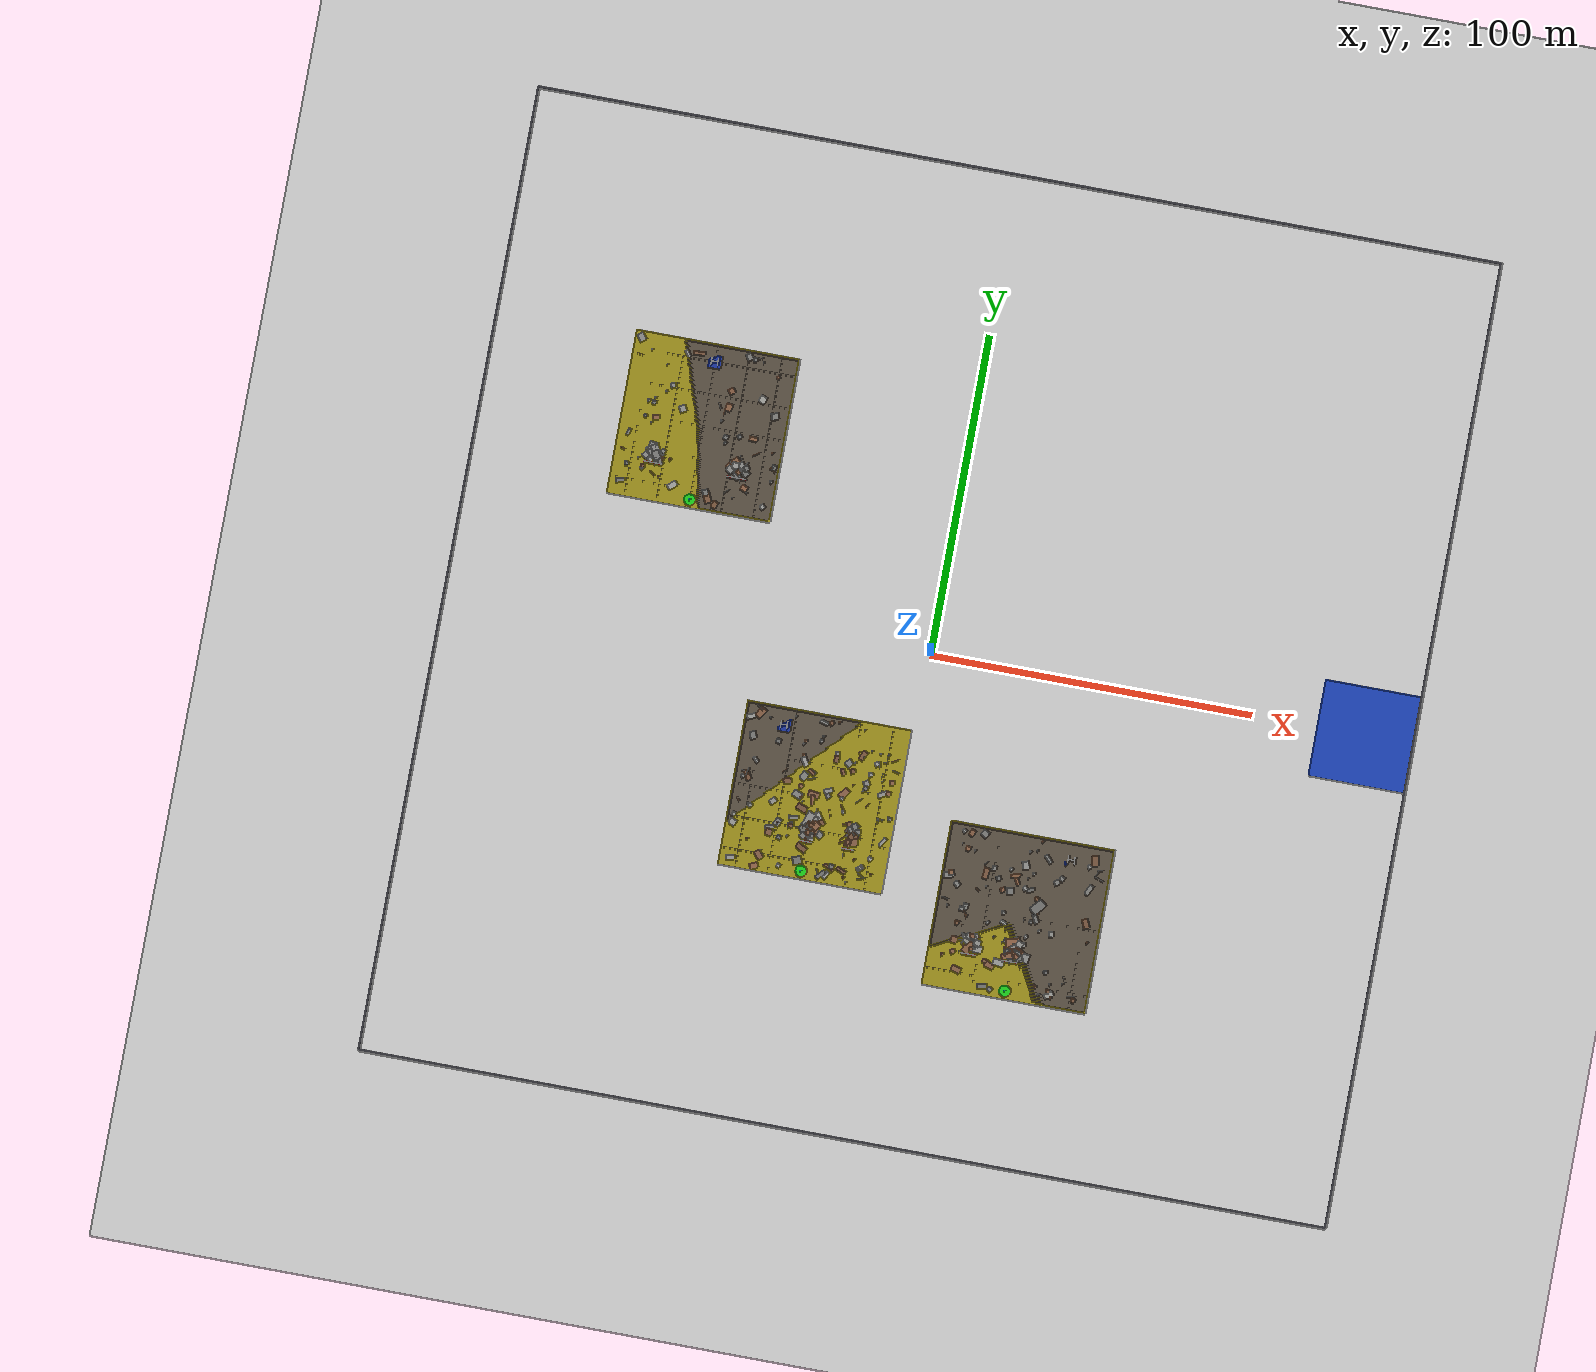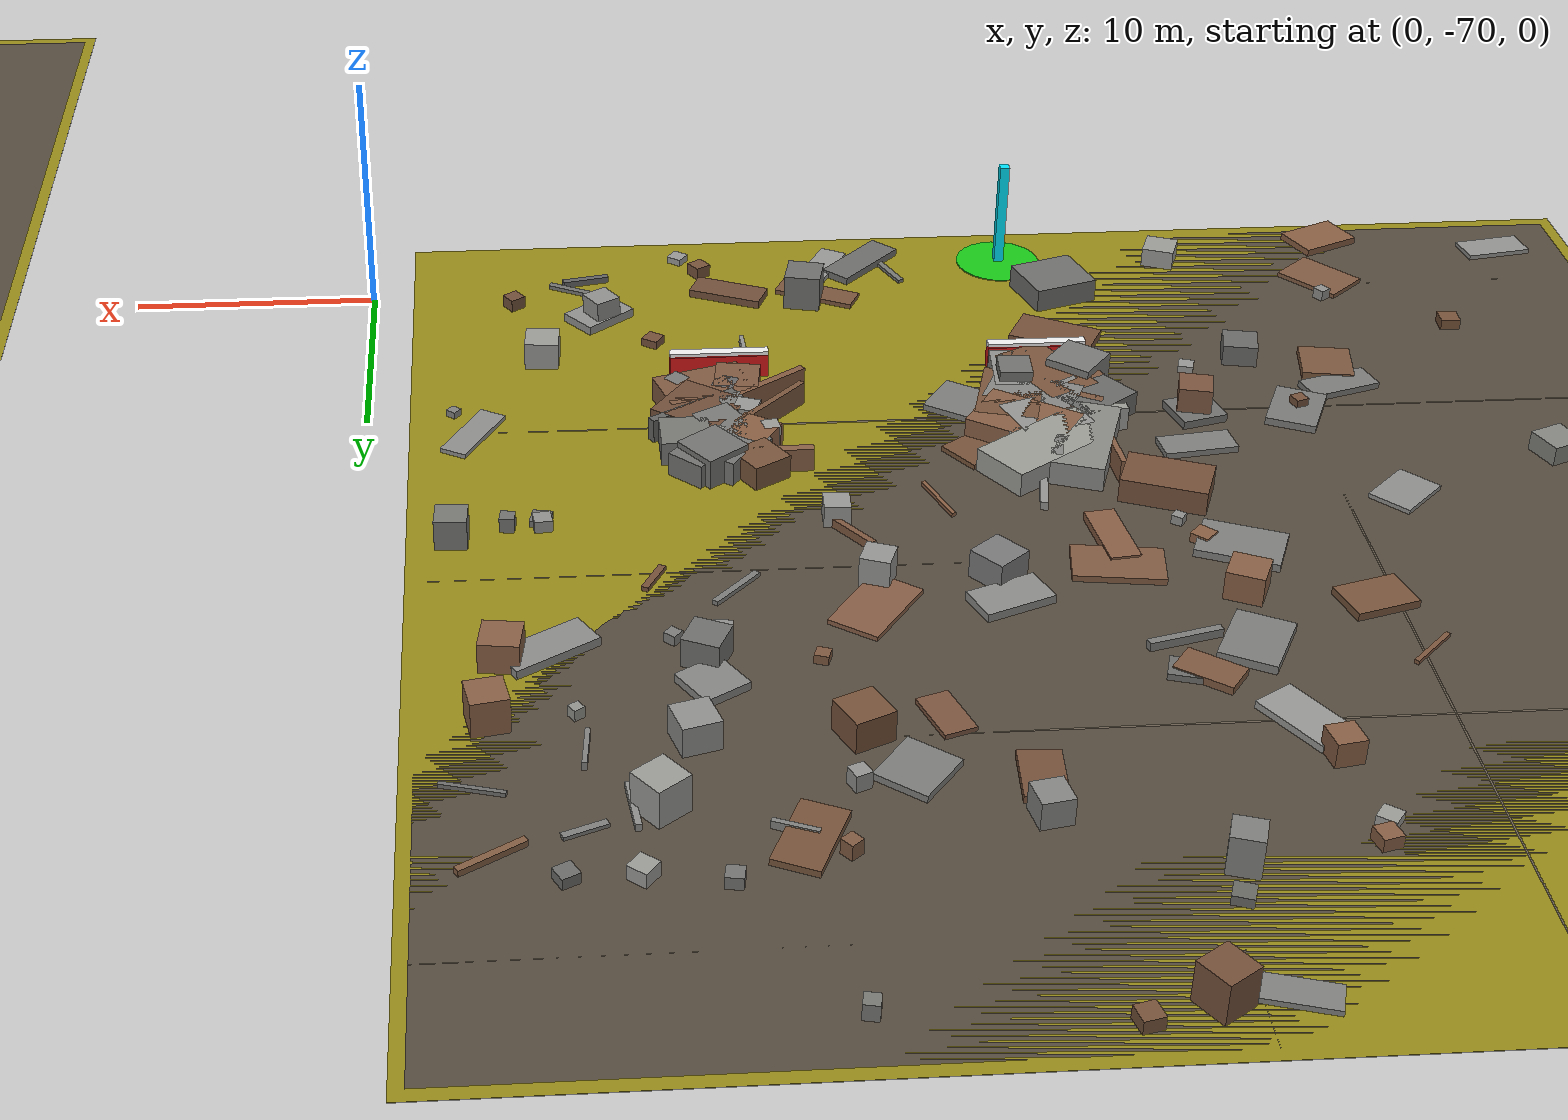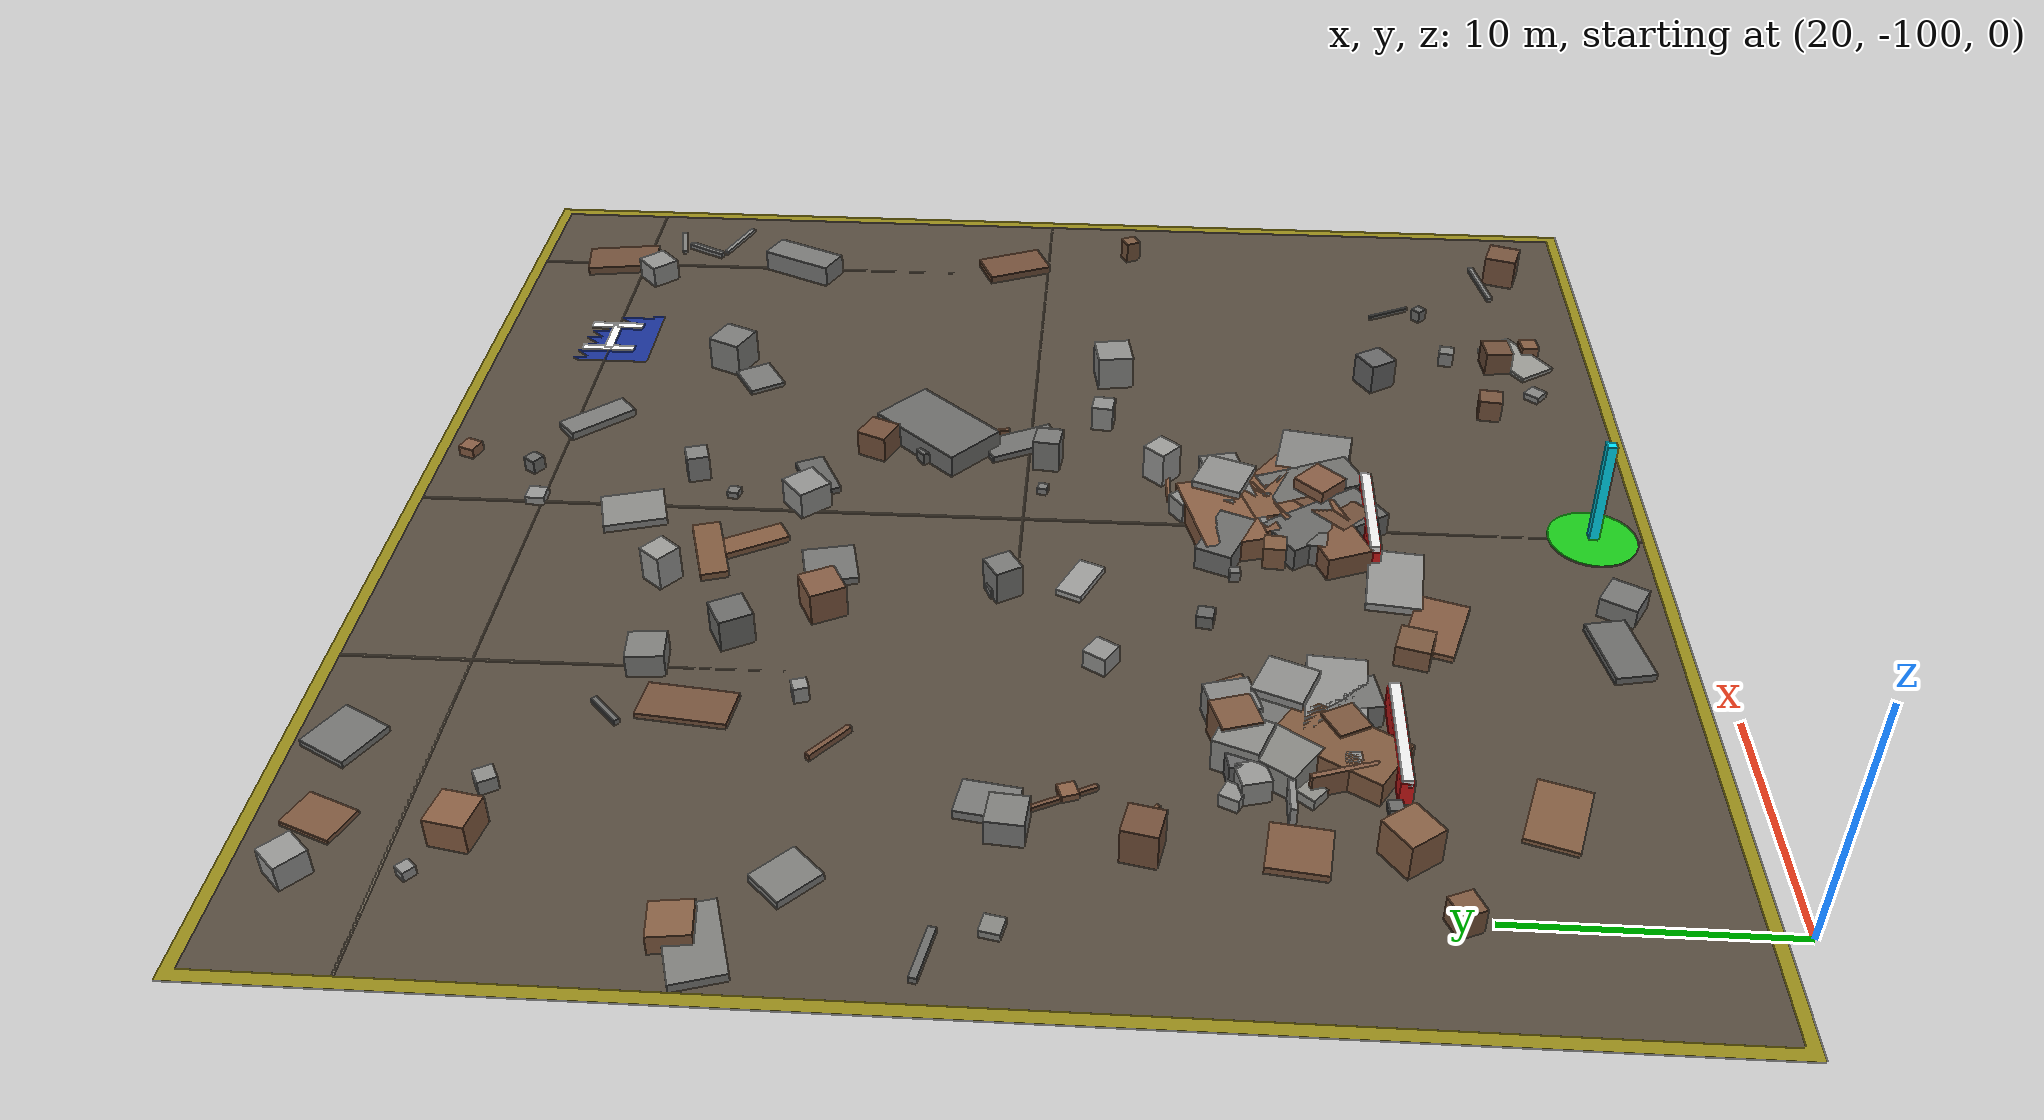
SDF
<sdf version="1.6">
 <world name="navitas_arena">
  <physics type="ode">
   <max_step_size>0.001</max_step_size>
   <real_time_factor>1</real_time_factor>
   <real_time_update_rate>1000</real_time_update_rate>
   <gravity>0 0 -9.8</gravity>
  </physics>
  <scene>
   <ambient>0.5 0.5 0.5 1</ambient>
   <background>0.75 0.8 0.85 1</background>
   <shadows>false</shadows>
  </scene>
  <light name="sun" type="directional">
   <cast_shadows>false</cast_shadows>
   <pose>0 0 120 0 -0 0</pose>
   <diffuse>0.9 0.9 0.85 1</diffuse>
   <specular>0.1 0.1 0.1 1</specular>
   <attenuation>
    <range>1200</range>
    <constant>0.9</constant>
    <linear>0.01</linear>
    <quadratic>0.001</quadratic>
   </attenuation>
   <direction>-0.4 0.2 -0.9</direction>
  </light>
  <model name="ground_plane">
   <static>true</static>
   <link name="link">
    <collision name="collision">
     <geometry><plane><normal>0 0 1</normal><size>400 400</size></plane></geometry>
     <surface><friction><ode><mu>0.8</mu><mu2>0.8</mu2></ode></friction></surface>
    </collision>
    <visual name="visual">
     <cast_shadows>false</cast_shadows>
     <geometry><plane><normal>0 0 1</normal><size>400 400</size></plane></geometry>
     <material>
      <script><uri>file://media/materials/scripts/gazebo.material</uri><name>Gazebo/Grey</name></script>
     </material>
    </visual>
   </link>
  </model>
  <model name="ub_N">
   <static>true</static>
   <pose>0.000 150.000 0.750 0 0 0.000</pose>
   <link name="link">
    <collision name="col"><geometry><box><size>300.000 0.600 1.500</size></box></geometry></collision>
    <visual name="vis">
     <geometry><box><size>300.000 0.600 1.500</size></box></geometry>
     <material><ambient>0.45 0.45 0.50 1</ambient><diffuse>0.45 0.45 0.50 1</diffuse></material>
    </visual>
   </link>
  </model>
  <model name="ub_S">
   <static>true</static>
   <pose>0.000 -150.000 0.750 0 0 0.000</pose>
   <link name="link">
    <collision name="col"><geometry><box><size>300.000 0.600 1.500</size></box></geometry></collision>
    <visual name="vis">
     <geometry><box><size>300.000 0.600 1.500</size></box></geometry>
     <material><ambient>0.45 0.45 0.50 1</ambient><diffuse>0.45 0.45 0.50 1</diffuse></material>
    </visual>
   </link>
  </model>
  <model name="ub_W">
   <static>true</static>
   <pose>-150.000 0.000 0.750 0 0 0.000</pose>
   <link name="link">
    <collision name="col"><geometry><box><size>0.600 300.000 1.500</size></box></geometry></collision>
    <visual name="vis">
     <geometry><box><size>0.600 300.000 1.500</size></box></geometry>
     <material><ambient>0.45 0.45 0.50 1</ambient><diffuse>0.45 0.45 0.50 1</diffuse></material>
    </visual>
   </link>
  </model>
  <model name="ub_E">
   <static>true</static>
   <pose>150.000 0.000 0.750 0 0 0.000</pose>
   <link name="link">
    <collision name="col"><geometry><box><size>0.600 300.000 1.500</size></box></geometry></collision>
    <visual name="vis">
     <geometry><box><size>0.600 300.000 1.500</size></box></geometry>
     <material><ambient>0.45 0.45 0.50 1</ambient><diffuse>0.45 0.45 0.50 1</diffuse></material>
    </visual>
   </link>
  </model>
  <model name="landing">
   <static>true</static>
   <pose>135.000 0.000 0.010 0 0 0.000</pose>
   <link name="link">
    <collision name="col"><geometry><box><size>30.000 30.000 0.020</size></box></geometry></collision>
    <visual name="vis">
     <geometry><box><size>30.000 30.000 0.020</size></box></geometry>
     <material><ambient>0.10 0.25 0.70 1</ambient><diffuse>0.10 0.25 0.70 1</diffuse></material>
    </visual>
   </link>
  </model>
  <model name="gr_kolay">
   <static>true</static>
   <pose>-81.400 56.800 0.010 0 0 0.000</pose>
   <link name="link">
    <collision name="col"><geometry><box><size>51.000 51.000 0.020</size></box></geometry></collision>
    <visual name="vis">
     <geometry><box><size>51.000 51.000 0.020</size></box></geometry>
     <material><ambient>0.60 0.55 0.10 1</ambient><diffuse>0.60 0.55 0.10 1</diffuse></material>
    </visual>
   </link>
  </model>
  <model name="gd_kolay">
   <static>true</static>
   <pose>-81.400 56.800 0.010 0 0 0.000</pose>
   <link name="link">
    <collision name="col"><geometry><box><size>50.000 50.000 0.020</size></box></geometry></collision>
    <visual name="vis">
     <geometry><box><size>50.000 50.000 0.020</size></box></geometry>
     <material><ambient>0.34 0.30 0.25 1</ambient><diffuse>0.34 0.30 0.25 1</diffuse></material>
    </visual>
   </link>
  </model>
  <model name="gv_kolay_-2">
   <static>true</static>
   <pose>-101.400 56.800 0.010 0 0 0.000</pose>
   <link name="link">
    <collision name="col"><geometry><box><size>0.120 50.000 0.020</size></box></geometry></collision>
    <visual name="vis">
     <geometry><box><size>0.120 50.000 0.020</size></box></geometry>
     <material><ambient>0.42 0.38 0.32 1</ambient><diffuse>0.42 0.38 0.32 1</diffuse></material>
    </visual>
   </link>
  </model>
  <model name="gh_kolay_-2">
   <static>true</static>
   <pose>-81.400 36.800 0.010 0 0 0.000</pose>
   <link name="link">
    <collision name="col"><geometry><box><size>50.000 0.120 0.020</size></box></geometry></collision>
    <visual name="vis">
     <geometry><box><size>50.000 0.120 0.020</size></box></geometry>
     <material><ambient>0.42 0.38 0.32 1</ambient><diffuse>0.42 0.38 0.32 1</diffuse></material>
    </visual>
   </link>
  </model>
  <model name="gv_kolay_-1">
   <static>true</static>
   <pose>-91.400 56.800 0.010 0 0 0.000</pose>
   <link name="link">
    <collision name="col"><geometry><box><size>0.120 50.000 0.020</size></box></geometry></collision>
    <visual name="vis">
     <geometry><box><size>0.120 50.000 0.020</size></box></geometry>
     <material><ambient>0.42 0.38 0.32 1</ambient><diffuse>0.42 0.38 0.32 1</diffuse></material>
    </visual>
   </link>
  </model>
  <model name="gh_kolay_-1">
   <static>true</static>
   <pose>-81.400 46.800 0.010 0 0 0.000</pose>
   <link name="link">
    <collision name="col"><geometry><box><size>50.000 0.120 0.020</size></box></geometry></collision>
    <visual name="vis">
     <geometry><box><size>50.000 0.120 0.020</size></box></geometry>
     <material><ambient>0.42 0.38 0.32 1</ambient><diffuse>0.42 0.38 0.32 1</diffuse></material>
    </visual>
   </link>
  </model>
  <model name="gv_kolay_0">
   <static>true</static>
   <pose>-81.400 56.800 0.010 0 0 0.000</pose>
   <link name="link">
    <collision name="col"><geometry><box><size>0.120 50.000 0.020</size></box></geometry></collision>
    <visual name="vis">
     <geometry><box><size>0.120 50.000 0.020</size></box></geometry>
     <material><ambient>0.42 0.38 0.32 1</ambient><diffuse>0.42 0.38 0.32 1</diffuse></material>
    </visual>
   </link>
  </model>
  <model name="gh_kolay_0">
   <static>true</static>
   <pose>-81.400 56.800 0.010 0 0 0.000</pose>
   <link name="link">
    <collision name="col"><geometry><box><size>50.000 0.120 0.020</size></box></geometry></collision>
    <visual name="vis">
     <geometry><box><size>50.000 0.120 0.020</size></box></geometry>
     <material><ambient>0.42 0.38 0.32 1</ambient><diffuse>0.42 0.38 0.32 1</diffuse></material>
    </visual>
   </link>
  </model>
  <model name="gv_kolay_1">
   <static>true</static>
   <pose>-71.400 56.800 0.010 0 0 0.000</pose>
   <link name="link">
    <collision name="col"><geometry><box><size>0.120 50.000 0.020</size></box></geometry></collision>
    <visual name="vis">
     <geometry><box><size>0.120 50.000 0.020</size></box></geometry>
     <material><ambient>0.42 0.38 0.32 1</ambient><diffuse>0.42 0.38 0.32 1</diffuse></material>
    </visual>
   </link>
  </model>
  <model name="gh_kolay_1">
   <static>true</static>
   <pose>-81.400 66.800 0.010 0 0 0.000</pose>
   <link name="link">
    <collision name="col"><geometry><box><size>50.000 0.120 0.020</size></box></geometry></collision>
    <visual name="vis">
     <geometry><box><size>50.000 0.120 0.020</size></box></geometry>
     <material><ambient>0.42 0.38 0.32 1</ambient><diffuse>0.42 0.38 0.32 1</diffuse></material>
    </visual>
   </link>
  </model>
  <model name="gv_kolay_2">
   <static>true</static>
   <pose>-61.400 56.800 0.010 0 0 0.000</pose>
   <link name="link">
    <collision name="col"><geometry><box><size>0.120 50.000 0.020</size></box></geometry></collision>
    <visual name="vis">
     <geometry><box><size>0.120 50.000 0.020</size></box></geometry>
     <material><ambient>0.42 0.38 0.32 1</ambient><diffuse>0.42 0.38 0.32 1</diffuse></material>
    </visual>
   </link>
  </model>
  <model name="gh_kolay_2">
   <static>true</static>
   <pose>-81.400 76.800 0.010 0 0 0.000</pose>
   <link name="link">
    <collision name="col"><geometry><box><size>50.000 0.120 0.020</size></box></geometry></collision>
    <visual name="vis">
     <geometry><box><size>50.000 0.120 0.020</size></box></geometry>
     <material><ambient>0.42 0.38 0.32 1</ambient><diffuse>0.42 0.38 0.32 1</diffuse></material>
    </visual>
   </link>
  </model>
  <model name="bar_kolay_0">
   <static>true</static>
   <pose>-94.400 42.800 0.500 0 0 0.000</pose>
   <link name="link">
    <collision name="col"><geometry><box><size>6.000 0.500 1.000</size></box></geometry></collision>
    <visual name="vis">
     <geometry><box><size>6.000 0.500 1.000</size></box></geometry>
     <material><ambient>0.85 0.10 0.10 1</ambient><diffuse>0.85 0.10 0.10 1</diffuse></material>
    </visual>
   </link>
  </model>
  <model name="bar_kolay_0b">
   <static>true</static>
   <pose>-94.400 42.800 1.000 0 0 0.000</pose>
   <link name="link">
    <collision name="col"><geometry><box><size>6.000 0.400 0.300</size></box></geometry></collision>
    <visual name="vis">
     <geometry><box><size>6.000 0.400 0.300</size></box></geometry>
     <material><ambient>0.95 0.95 0.95 1</ambient><diffuse>0.95 0.95 0.95 1</diffuse></material>
    </visual>
   </link>
  </model>
  <model name="blk_kolay_0_0_0">
   <static>true</static>
   <pose>-97.054 44.795 0.739 0 0 0.849</pose>
   <link name="link">
    <collision name="col"><geometry><box><size>1.883 1.883 1.478</size></box></geometry></collision>
    <visual name="vis">
     <geometry><box><size>1.883 1.883 1.478</size></box></geometry>
     <material><ambient>0.53 0.53 0.52 1</ambient><diffuse>0.53 0.53 0.52 1</diffuse></material>
    </visual>
   </link>
  </model>
  <model name="blk_kolay_0_0_1">
   <static>true</static>
   <pose>-96.267 44.581 0.500 0 0 1.383</pose>
   <link name="link">
    <collision name="col"><geometry><box><size>3.385 0.306 1.000</size></box></geometry></collision>
    <visual name="vis">
     <geometry><box><size>3.385 0.306 1.000</size></box></geometry>
     <material><ambient>0.42 0.42 0.41 1</ambient><diffuse>0.42 0.42 0.41 1</diffuse></material>
    </visual>
   </link>
  </model>
  <model name="blk_kolay_0_0_2">
   <static>true</static>
   <pose>-95.387 44.592 0.500 0 0 1.142</pose>
   <link name="link">
    <collision name="col"><geometry><box><size>3.016 2.078 1.000</size></box></geometry></collision>
    <visual name="vis">
     <geometry><box><size>3.016 2.078 1.000</size></box></geometry>
     <material><ambient>0.60 0.60 0.59 1</ambient><diffuse>0.60 0.60 0.59 1</diffuse></material>
    </visual>
   </link>
  </model>
  <model name="blk_kolay_0_0_3">
   <static>true</static>
   <pose>-94.416 44.444 0.500 0 0 2.418</pose>
   <link name="link">
    <collision name="col"><geometry><box><size>3.447 0.418 1.000</size></box></geometry></collision>
    <visual name="vis">
     <geometry><box><size>3.447 0.418 1.000</size></box></geometry>
     <material><ambient>0.52 0.52 0.51 1</ambient><diffuse>0.52 0.52 0.51 1</diffuse></material>
    </visual>
   </link>
  </model>
  <model name="blk_kolay_0_0_4">
   <static>true</static>
   <pose>-93.661 44.766 0.500 0 0 2.030</pose>
   <link name="link">
    <collision name="col"><geometry><box><size>4.451 2.454 1.000</size></box></geometry></collision>
    <visual name="vis">
     <geometry><box><size>4.451 2.454 1.000</size></box></geometry>
     <material><ambient>0.47 0.47 0.46 1</ambient><diffuse>0.47 0.47 0.46 1</diffuse></material>
    </visual>
   </link>
  </model>
  <model name="blk_kolay_0_0_5">
   <static>true</static>
   <pose>-92.754 44.410 0.500 0 0 0.998</pose>
   <link name="link">
    <collision name="col"><geometry><box><size>2.681 0.370 1.000</size></box></geometry></collision>
    <visual name="vis">
     <geometry><box><size>2.681 0.370 1.000</size></box></geometry>
     <material><ambient>0.45 0.45 0.44 1</ambient><diffuse>0.45 0.45 0.44 1</diffuse></material>
    </visual>
   </link>
  </model>
  <model name="blk_kolay_0_0_6">
   <static>true</static>
   <pose>-91.997 44.624 0.500 0 0 1.170</pose>
   <link name="link">
    <collision name="col"><geometry><box><size>1.427 1.427 1.000</size></box></geometry></collision>
    <visual name="vis">
     <geometry><box><size>1.427 1.427 1.000</size></box></geometry>
     <material><ambient>0.54 0.38 0.27 1</ambient><diffuse>0.54 0.38 0.27 1</diffuse></material>
    </visual>
   </link>
  </model>
  <model name="blk_kolay_0_1_0">
   <static>true</static>
   <pose>-97.035 46.865 0.500 0 0 0.334</pose>
   <link name="link">
    <collision name="col"><geometry><box><size>0.883 0.883 1.000</size></box></geometry></collision>
    <visual name="vis">
     <geometry><box><size>0.883 0.883 1.000</size></box></geometry>
     <material><ambient>0.60 0.60 0.59 1</ambient><diffuse>0.60 0.60 0.59 1</diffuse></material>
    </visual>
   </link>
  </model>
  <model name="blk_kolay_0_1_1">
   <static>true</static>
   <pose>-96.397 46.823 0.500 0 0 2.184</pose>
   <link name="link">
    <collision name="col"><geometry><box><size>0.692 0.692 1.000</size></box></geometry></collision>
    <visual name="vis">
     <geometry><box><size>0.692 0.692 1.000</size></box></geometry>
     <material><ambient>0.55 0.55 0.53 1</ambient><diffuse>0.55 0.55 0.53 1</diffuse></material>
    </visual>
   </link>
  </model>
  <model name="blk_kolay_0_1_2">
   <static>true</static>
   <pose>-95.480 46.927 0.500 0 0 1.435</pose>
   <link name="link">
    <collision name="col"><geometry><box><size>4.741 2.613 1.000</size></box></geometry></collision>
    <visual name="vis">
     <geometry><box><size>4.741 2.613 1.000</size></box></geometry>
     <material><ambient>0.51 0.51 0.50 1</ambient><diffuse>0.51 0.51 0.50 1</diffuse></material>
    </visual>
   </link>
  </model>
  <model name="blk_kolay_0_1_3">
   <static>true</static>
   <pose>-94.180 46.609 0.500 0 0 2.072</pose>
   <link name="link">
    <collision name="col"><geometry><box><size>4.235 2.531 1.000</size></box></geometry></collision>
    <visual name="vis">
     <geometry><box><size>4.235 2.531 1.000</size></box></geometry>
     <material><ambient>0.53 0.53 0.52 1</ambient><diffuse>0.53 0.53 0.52 1</diffuse></material>
    </visual>
   </link>
  </model>
  <model name="blk_kolay_0_1_4">
   <static>true</static>
   <pose>-93.383 46.558 0.500 0 0 2.525</pose>
   <link name="link">
    <collision name="col"><geometry><box><size>4.191 1.459 1.000</size></box></geometry></collision>
    <visual name="vis">
     <geometry><box><size>4.191 1.459 1.000</size></box></geometry>
     <material><ambient>0.62 0.62 0.61 1</ambient><diffuse>0.62 0.62 0.61 1</diffuse></material>
    </visual>
   </link>
  </model>
  <model name="blk_kolay_0_1_5">
   <static>true</static>
   <pose>-92.842 46.450 0.500 0 0 0.870</pose>
   <link name="link">
    <collision name="col"><geometry><box><size>0.651 0.651 1.000</size></box></geometry></collision>
    <visual name="vis">
     <geometry><box><size>0.651 0.651 1.000</size></box></geometry>
     <material><ambient>0.46 0.46 0.45 1</ambient><diffuse>0.46 0.46 0.45 1</diffuse></material>
    </visual>
   </link>
  </model>
  <model name="blk_kolay_0_1_6">
   <static>true</static>
   <pose>-92.014 46.894 0.668 0 0 2.581</pose>
   <link name="link">
    <collision name="col"><geometry><box><size>1.340 1.340 1.337</size></box></geometry></collision>
    <visual name="vis">
     <geometry><box><size>1.340 1.340 1.337</size></box></geometry>
     <material><ambient>0.50 0.50 0.49 1</ambient><diffuse>0.50 0.50 0.49 1</diffuse></material>
    </visual>
   </link>
  </model>
  <model name="bar_kolay_2">
   <static>true</static>
   <pose>-68.400 42.800 0.500 0 0 0.000</pose>
   <link name="link">
    <collision name="col"><geometry><box><size>6.000 0.500 1.000</size></box></geometry></collision>
    <visual name="vis">
     <geometry><box><size>6.000 0.500 1.000</size></box></geometry>
     <material><ambient>0.85 0.10 0.10 1</ambient><diffuse>0.85 0.10 0.10 1</diffuse></material>
    </visual>
   </link>
  </model>
  <model name="bar_kolay_2b">
   <static>true</static>
   <pose>-68.400 42.800 1.000 0 0 0.000</pose>
   <link name="link">
    <collision name="col"><geometry><box><size>6.000 0.400 0.300</size></box></geometry></collision>
    <visual name="vis">
     <geometry><box><size>6.000 0.400 0.300</size></box></geometry>
     <material><ambient>0.95 0.95 0.95 1</ambient><diffuse>0.95 0.95 0.95 1</diffuse></material>
    </visual>
   </link>
  </model>
  <model name="blk_kolay_2_0_0">
   <static>true</static>
   <pose>-70.767 45.072 0.770 0 0 1.059</pose>
   <link name="link">
    <collision name="col"><geometry><box><size>2.152 2.152 1.540</size></box></geometry></collision>
    <visual name="vis">
     <geometry><box><size>2.152 2.152 1.540</size></box></geometry>
     <material><ambient>0.53 0.53 0.52 1</ambient><diffuse>0.53 0.53 0.52 1</diffuse></material>
    </visual>
   </link>
  </model>
  <model name="blk_kolay_2_0_1">
   <static>true</static>
   <pose>-70.160 44.675 0.646 0 0 2.922</pose>
   <link name="link">
    <collision name="col"><geometry><box><size>1.332 1.332 1.292</size></box></geometry></collision>
    <visual name="vis">
     <geometry><box><size>1.332 1.332 1.292</size></box></geometry>
     <material><ambient>0.45 0.45 0.44 1</ambient><diffuse>0.45 0.45 0.44 1</diffuse></material>
    </visual>
   </link>
  </model>
  <model name="blk_kolay_2_0_2">
   <static>true</static>
   <pose>-69.182 44.477 0.500 0 0 2.260</pose>
   <link name="link">
    <collision name="col"><geometry><box><size>4.852 1.996 1.000</size></box></geometry></collision>
    <visual name="vis">
     <geometry><box><size>4.852 1.996 1.000</size></box></geometry>
     <material><ambient>0.47 0.47 0.46 1</ambient><diffuse>0.47 0.47 0.46 1</diffuse></material>
    </visual>
   </link>
  </model>
  <model name="blk_kolay_2_0_3">
   <static>true</static>
   <pose>-68.164 44.538 0.613 0 0 2.458</pose>
   <link name="link">
    <collision name="col"><geometry><box><size>1.448 1.448 1.226</size></box></geometry></collision>
    <visual name="vis">
     <geometry><box><size>1.448 1.448 1.226</size></box></geometry>
     <material><ambient>0.49 0.34 0.24 1</ambient><diffuse>0.49 0.34 0.24 1</diffuse></material>
    </visual>
   </link>
  </model>
  <model name="blk_kolay_2_0_4">
   <static>true</static>
   <pose>-67.743 44.645 0.500 0 0 2.201</pose>
   <link name="link">
    <collision name="col"><geometry><box><size>0.611 0.611 1.000</size></box></geometry></collision>
    <visual name="vis">
     <geometry><box><size>0.611 0.611 1.000</size></box></geometry>
     <material><ambient>0.54 0.37 0.27 1</ambient><diffuse>0.54 0.37 0.27 1</diffuse></material>
    </visual>
   </link>
  </model>
  <model name="blk_kolay_2_0_5">
   <static>true</static>
   <pose>-66.387 44.774 0.500 0 0 1.240</pose>
   <link name="link">
    <collision name="col"><geometry><box><size>0.718 0.718 1.000</size></box></geometry></collision>
    <visual name="vis">
     <geometry><box><size>0.718 0.718 1.000</size></box></geometry>
     <material><ambient>0.45 0.32 0.23 1</ambient><diffuse>0.45 0.32 0.23 1</diffuse></material>
    </visual>
   </link>
  </model>
  <model name="blk_kolay_2_0_6">
   <static>true</static>
   <pose>-65.983 44.681 0.592 0 0 0.886</pose>
   <link name="link">
    <collision name="col"><geometry><box><size>2.100 2.100 1.185</size></box></geometry></collision>
    <visual name="vis">
     <geometry><box><size>2.100 2.100 1.185</size></box></geometry>
     <material><ambient>0.44 0.44 0.43 1</ambient><diffuse>0.44 0.44 0.43 1</diffuse></material>
    </visual>
   </link>
  </model>
  <model name="blk_kolay_2_1_0">
   <static>true</static>
   <pose>-71.097 46.806 0.500 0 0 1.899</pose>
   <link name="link">
    <collision name="col"><geometry><box><size>1.068 1.068 1.000</size></box></geometry></collision>
    <visual name="vis">
     <geometry><box><size>1.068 1.068 1.000</size></box></geometry>
     <material><ambient>0.61 0.61 0.59 1</ambient><diffuse>0.61 0.61 0.59 1</diffuse></material>
    </visual>
   </link>
  </model>
  <model name="blk_kolay_2_1_1">
   <static>true</static>
   <pose>-69.917 46.673 0.500 0 0 0.866</pose>
   <link name="link">
    <collision name="col"><geometry><box><size>4.645 2.918 1.000</size></box></geometry></collision>
    <visual name="vis">
     <geometry><box><size>4.645 2.918 1.000</size></box></geometry>
     <material><ambient>0.52 0.37 0.26 1</ambient><diffuse>0.52 0.37 0.26 1</diffuse></material>
    </visual>
   </link>
  </model>
  <model name="blk_kolay_2_1_2">
   <static>true</static>
   <pose>-69.430 46.572 0.790 0 0 3.023</pose>
   <link name="link">
    <collision name="col"><geometry><box><size>2.017 2.017 1.579</size></box></geometry></collision>
    <visual name="vis">
     <geometry><box><size>2.017 2.017 1.579</size></box></geometry>
     <material><ambient>0.59 0.59 0.58 1</ambient><diffuse>0.59 0.59 0.58 1</diffuse></material>
    </visual>
   </link>
  </model>
  <model name="blk_kolay_2_1_3">
   <static>true</static>
   <pose>-68.612 46.264 0.500 0 0 0.207</pose>
   <link name="link">
    <collision name="col"><geometry><box><size>0.926 0.926 1.000</size></box></geometry></collision>
    <visual name="vis">
     <geometry><box><size>0.926 0.926 1.000</size></box></geometry>
     <material><ambient>0.54 0.54 0.53 1</ambient><diffuse>0.54 0.54 0.53 1</diffuse></material>
    </visual>
   </link>
  </model>
  <model name="blk_kolay_2_1_4">
   <static>true</static>
   <pose>-67.659 46.999 0.549 0 0 0.522</pose>
   <link name="link">
    <collision name="col"><geometry><box><size>1.881 1.881 1.097</size></box></geometry></collision>
    <visual name="vis">
     <geometry><box><size>1.881 1.881 1.097</size></box></geometry>
     <material><ambient>0.54 0.54 0.53 1</ambient><diffuse>0.54 0.54 0.53 1</diffuse></material>
    </visual>
   </link>
  </model>
  <model name="blk_kolay_2_1_5">
   <static>true</static>
   <pose>-66.630 46.229 0.500 0 0 1.113</pose>
   <link name="link">
    <collision name="col"><geometry><box><size>4.037 0.280 1.000</size></box></geometry></collision>
    <visual name="vis">
     <geometry><box><size>4.037 0.280 1.000</size></box></geometry>
     <material><ambient>0.60 0.60 0.59 1</ambient><diffuse>0.60 0.60 0.59 1</diffuse></material>
    </visual>
   </link>
  </model>
  <model name="blk_kolay_2_1_6">
   <static>true</static>
   <pose>-65.931 46.253 0.749 0 0 0.501</pose>
   <link name="link">
    <collision name="col"><geometry><box><size>1.617 1.617 1.497</size></box></geometry></collision>
    <visual name="vis">
     <geometry><box><size>1.617 1.617 1.497</size></box></geometry>
     <material><ambient>0.45 0.45 0.44 1</ambient><diffuse>0.45 0.45 0.44 1</diffuse></material>
    </visual>
   </link>
  </model>
  <model name="chic_kolay_2">
   <static>true</static>
   <pose>-77.081 36.800 0.572 0 0 1.946</pose>
   <link name="link">
    <collision name="col"><geometry><box><size>1.904 1.904 1.144</size></box></geometry></collision>
    <visual name="vis">
     <geometry><box><size>1.904 1.904 1.144</size></box></geometry>
     <material><ambient>0.46 0.46 0.45 1</ambient><diffuse>0.46 0.46 0.45 1</diffuse></material>
    </visual>
   </link>
  </model>
  <model name="chic_kolay_3">
   <static>true</static>
   <pose>-89.568 44.800 0.500 0 0 2.724</pose>
   <link name="link">
    <collision name="col"><geometry><box><size>0.823 0.823 1.000</size></box></geometry></collision>
    <visual name="vis">
     <geometry><box><size>0.823 0.823 1.000</size></box></geometry>
     <material><ambient>0.52 0.36 0.26 1</ambient><diffuse>0.52 0.36 0.26 1</diffuse></material>
    </visual>
   </link>
  </model>
  <model name="chic_kolay_4">
   <static>true</static>
   <pose>-73.791 52.800 0.500 0 0 2.846</pose>
   <link name="link">
    <collision name="col"><geometry><box><size>0.880 0.880 1.000</size></box></geometry></collision>
    <visual name="vis">
     <geometry><box><size>0.880 0.880 1.000</size></box></geometry>
     <material><ambient>0.42 0.42 0.41 1</ambient><diffuse>0.42 0.42 0.41 1</diffuse></material>
    </visual>
   </link>
  </model>
  <model name="chic_kolay_5">
   <static>true</static>
   <pose>-88.486 60.800 0.689 0 0 2.048</pose>
   <link name="link">
    <collision name="col"><geometry><box><size>2.145 2.145 1.377</size></box></geometry></collision>
    <visual name="vis">
     <geometry><box><size>2.145 2.145 1.377</size></box></geometry>
     <material><ambient>0.56 0.56 0.55 1</ambient><diffuse>0.56 0.56 0.55 1</diffuse></material>
    </visual>
   </link>
  </model>
  <model name="chic_kolay_6">
   <static>true</static>
   <pose>-74.685 68.800 0.557 0 0 2.190</pose>
   <link name="link">
    <collision name="col"><geometry><box><size>1.858 1.858 1.113</size></box></geometry></collision>
    <visual name="vis">
     <geometry><box><size>1.858 1.858 1.113</size></box></geometry>
     <material><ambient>0.51 0.35 0.25 1</ambient><diffuse>0.51 0.35 0.25 1</diffuse></material>
    </visual>
   </link>
  </model>
  <model name="deb_kolay_0">
   <static>true</static>
   <pose>-99.127 43.588 0.177 0 0 2.368</pose>
   <link name="link">
    <collision name="col"><geometry><box><size>0.594 0.594 0.353</size></box></geometry></collision>
    <visual name="vis">
     <geometry><box><size>0.594 0.594 0.353</size></box></geometry>
     <material><ambient>0.55 0.55 0.53 1</ambient><diffuse>0.55 0.55 0.53 1</diffuse></material>
    </visual>
   </link>
  </model>
  <model name="deb_kolay_1">
   <static>true</static>
   <pose>-65.619 40.223 0.125 0 0 2.723</pose>
   <link name="link">
    <collision name="col"><geometry><box><size>2.075 1.817 0.251</size></box></geometry></collision>
    <visual name="vis">
     <geometry><box><size>2.075 1.817 0.251</size></box></geometry>
     <material><ambient>0.55 0.38 0.27 1</ambient><diffuse>0.55 0.38 0.27 1</diffuse></material>
    </visual>
   </link>
  </model>
  <model name="deb_kolay_2">
   <static>true</static>
   <pose>-103.393 35.946 0.158 0 0 0.276</pose>
   <link name="link">
    <collision name="col"><geometry><box><size>2.740 1.289 0.317</size></box></geometry></collision>
    <visual name="vis">
     <geometry><box><size>2.740 1.289 0.317</size></box></geometry>
     <material><ambient>0.45 0.45 0.44 1</ambient><diffuse>0.45 0.45 0.44 1</diffuse></material>
    </visual>
   </link>
  </model>
  <model name="deb_kolay_3">
   <static>true</static>
   <pose>-67.884 48.969 0.161 0 0 2.079</pose>
   <link name="link">
    <collision name="col"><geometry><box><size>2.001 0.177 0.322</size></box></geometry></collision>
    <visual name="vis">
     <geometry><box><size>2.001 0.177 0.322</size></box></geometry>
     <material><ambient>0.44 0.44 0.44 1</ambient><diffuse>0.44 0.44 0.44 1</diffuse></material>
    </visual>
   </link>
  </model>
  <model name="deb_kolay_4">
   <static>true</static>
   <pose>-74.725 63.818 0.199 0 0 1.358</pose>
   <link name="link">
    <collision name="col"><geometry><box><size>2.447 1.984 0.399</size></box></geometry></collision>
    <visual name="vis">
     <geometry><box><size>2.447 1.984 0.399</size></box></geometry>
     <material><ambient>0.53 0.37 0.26 1</ambient><diffuse>0.53 0.37 0.26 1</diffuse></material>
    </visual>
   </link>
  </model>
  <model name="deb_kolay_5">
   <static>true</static>
   <pose>-57.704 48.077 0.198 0 0 1.437</pose>
   <link name="link">
    <collision name="col"><geometry><box><size>1.800 1.439 0.397</size></box></geometry></collision>
    <visual name="vis">
     <geometry><box><size>1.800 1.439 0.397</size></box></geometry>
     <material><ambient>0.42 0.42 0.41 1</ambient><diffuse>0.42 0.42 0.41 1</diffuse></material>
    </visual>
   </link>
  </model>
  <model name="deb_kolay_6">
   <static>true</static>
   <pose>-95.555 73.252 0.348 0 0 0.706</pose>
   <link name="link">
    <collision name="col"><geometry><box><size>0.507 0.507 0.695</size></box></geometry></collision>
    <visual name="vis">
     <geometry><box><size>0.507 0.507 0.695</size></box></geometry>
     <material><ambient>0.46 0.46 0.45 1</ambient><diffuse>0.46 0.46 0.45 1</diffuse></material>
    </visual>
   </link>
  </model>
  <model name="deb_kolay_7">
   <static>true</static>
   <pose>-99.157 61.489 0.485 0 0 1.950</pose>
   <link name="link">
    <collision name="col"><geometry><box><size>1.021 1.021 0.970</size></box></geometry></collision>
    <visual name="vis">
     <geometry><box><size>1.021 1.021 0.970</size></box></geometry>
     <material><ambient>0.50 0.50 0.49 1</ambient><diffuse>0.50 0.50 0.49 1</diffuse></material>
    </visual>
   </link>
  </model>
  <model name="deb_kolay_8">
   <static>true</static>
   <pose>-102.477 41.294 0.761 0 0 1.670</pose>
   <link name="link">
    <collision name="col"><geometry><box><size>1.229 1.229 1.521</size></box></geometry></collision>
    <visual name="vis">
     <geometry><box><size>1.229 1.229 1.521</size></box></geometry>
     <material><ambient>0.44 0.44 0.44 1</ambient><diffuse>0.44 0.44 0.44 1</diffuse></material>
    </visual>
   </link>
  </model>
  <model name="deb_kolay_9">
   <static>true</static>
   <pose>-65.577 55.617 0.186 0 0 3.085</pose>
   <link name="link">
    <collision name="col"><geometry><box><size>2.548 1.374 0.372</size></box></geometry></collision>
    <visual name="vis">
     <geometry><box><size>2.548 1.374 0.372</size></box></geometry>
     <material><ambient>0.54 0.38 0.27 1</ambient><diffuse>0.54 0.38 0.27 1</diffuse></material>
    </visual>
   </link>
  </model>
  <model name="deb_kolay_10">
   <static>true</static>
   <pose>-97.448 61.168 0.547 0 0 3.013</pose>
   <link name="link">
    <collision name="col"><geometry><box><size>1.330 1.330 1.095</size></box></geometry></collision>
    <visual name="vis">
     <geometry><box><size>1.330 1.330 1.095</size></box></geometry>
     <material><ambient>0.46 0.46 0.45 1</ambient><diffuse>0.46 0.46 0.45 1</diffuse></material>
    </visual>
   </link>
  </model>
  <model name="deb_kolay_11">
   <static>true</static>
   <pose>-104.327 45.654 0.153 0 0 2.780</pose>
   <link name="link">
    <collision name="col"><geometry><box><size>2.136 0.287 0.307</size></box></geometry></collision>
    <visual name="vis">
     <geometry><box><size>2.136 0.287 0.307</size></box></geometry>
     <material><ambient>0.53 0.37 0.27 1</ambient><diffuse>0.53 0.37 0.27 1</diffuse></material>
    </visual>
   </link>
  </model>
  <model name="deb_kolay_12">
   <static>true</static>
   <pose>-92.697 67.331 0.644 0 0 0.457</pose>
   <link name="link">
    <collision name="col"><geometry><box><size>1.516 1.516 1.289</size></box></geometry></collision>
    <visual name="vis">
     <geometry><box><size>1.516 1.516 1.289</size></box></geometry>
     <material><ambient>0.54 0.54 0.53 1</ambient><diffuse>0.54 0.54 0.53 1</diffuse></material>
    </visual>
   </link>
  </model>
  <model name="deb_kolay_13">
   <static>true</static>
   <pose>-96.096 56.871 0.130 0 0 0.185</pose>
   <link name="link">
    <collision name="col"><geometry><box><size>1.898 1.366 0.259</size></box></geometry></collision>
    <visual name="vis">
     <geometry><box><size>1.898 1.366 0.259</size></box></geometry>
     <material><ambient>0.55 0.38 0.27 1</ambient><diffuse>0.55 0.38 0.27 1</diffuse></material>
    </visual>
   </link>
  </model>
  <model name="deb_kolay_14">
   <static>true</static>
   <pose>-104.853 80.174 0.155 0 0 2.267</pose>
   <link name="link">
    <collision name="col"><geometry><box><size>2.560 2.199 0.311</size></box></geometry></collision>
    <visual name="vis">
     <geometry><box><size>2.560 2.199 0.311</size></box></geometry>
     <material><ambient>0.53 0.53 0.52 1</ambient><diffuse>0.53 0.53 0.52 1</diffuse></material>
    </visual>
   </link>
  </model>
  <model name="deb_kolay_15">
   <static>true</static>
   <pose>-73.656 33.602 0.117 0 0 1.215</pose>
   <link name="link">
    <collision name="col"><geometry><box><size>2.302 1.705 0.235</size></box></geometry></collision>
    <visual name="vis">
     <geometry><box><size>2.302 1.705 0.235</size></box></geometry>
     <material><ambient>0.47 0.33 0.23 1</ambient><diffuse>0.47 0.33 0.23 1</diffuse></material>
    </visual>
   </link>
  </model>
  <model name="deb_kolay_16">
   <static>true</static>
   <pose>-73.932 54.596 0.437 0 0 2.972</pose>
   <link name="link">
    <collision name="col"><geometry><box><size>1.515 1.515 0.875</size></box></geometry></collision>
    <visual name="vis">
     <geometry><box><size>1.515 1.515 0.875</size></box></geometry>
     <material><ambient>0.46 0.46 0.45 1</ambient><diffuse>0.46 0.46 0.45 1</diffuse></material>
    </visual>
   </link>
  </model>
  <model name="deb_kolay_17">
   <static>true</static>
   <pose>-64.872 68.004 0.133 0 0 1.199</pose>
   <link name="link">
    <collision name="col"><geometry><box><size>2.339 2.152 0.266</size></box></geometry></collision>
    <visual name="vis">
     <geometry><box><size>2.339 2.152 0.266</size></box></geometry>
     <material><ambient>0.62 0.62 0.60 1</ambient><diffuse>0.62 0.62 0.60 1</diffuse></material>
    </visual>
   </link>
  </model>
  <model name="deb_kolay_18">
   <static>true</static>
   <pose>-104.294 74.991 0.108 0 0 3.027</pose>
   <link name="link">
    <collision name="col"><geometry><box><size>1.758 0.218 0.215</size></box></geometry></collision>
    <visual name="vis">
     <geometry><box><size>1.758 0.218 0.215</size></box></geometry>
     <material><ambient>0.46 0.32 0.23 1</ambient><diffuse>0.46 0.32 0.23 1</diffuse></material>
    </visual>
   </link>
  </model>
  <model name="deb_kolay_19">
   <static>true</static>
   <pose>-97.092 54.917 0.167 0 0 1.943</pose>
   <link name="link">
    <collision name="col"><geometry><box><size>0.701 0.701 0.333</size></box></geometry></collision>
    <visual name="vis">
     <geometry><box><size>0.701 0.701 0.333</size></box></geometry>
     <material><ambient>0.48 0.48 0.47 1</ambient><diffuse>0.48 0.48 0.47 1</diffuse></material>
    </visual>
   </link>
  </model>
  <model name="deb_kolay_20">
   <static>true</static>
   <pose>-91.989 38.971 0.312 0 0 1.923</pose>
   <link name="link">
    <collision name="col"><geometry><box><size>0.519 0.519 0.623</size></box></geometry></collision>
    <visual name="vis">
     <geometry><box><size>0.519 0.519 0.623</size></box></geometry>
     <material><ambient>0.51 0.35 0.25 1</ambient><diffuse>0.51 0.35 0.25 1</diffuse></material>
    </visual>
   </link>
  </model>
  <model name="deb_kolay_21">
   <static>true</static>
   <pose>-97.273 62.587 0.219 0 0 3.113</pose>
   <link name="link">
    <collision name="col"><geometry><box><size>0.723 0.723 0.438</size></box></geometry></collision>
    <visual name="vis">
     <geometry><box><size>0.723 0.723 0.438</size></box></geometry>
     <material><ambient>0.54 0.54 0.53 1</ambient><diffuse>0.54 0.54 0.53 1</diffuse></material>
    </visual>
   </link>
  </model>
  <model name="deb_kolay_22">
   <static>true</static>
   <pose>-66.833 79.704 0.085 0 0 1.895</pose>
   <link name="link">
    <collision name="col"><geometry><box><size>2.009 0.199 0.171</size></box></geometry></collision>
    <visual name="vis">
     <geometry><box><size>2.009 0.199 0.171</size></box></geometry>
     <material><ambient>0.40 0.40 0.40 1</ambient><diffuse>0.40 0.40 0.40 1</diffuse></material>
    </visual>
   </link>
  </model>
  <model name="deb_kolay_23">
   <static>true</static>
   <pose>-61.334 75.395 0.693 0 0 0.682</pose>
   <link name="link">
    <collision name="col"><geometry><box><size>0.971 0.971 1.387</size></box></geometry></collision>
    <visual name="vis">
     <geometry><box><size>0.971 0.971 1.387</size></box></geometry>
     <material><ambient>0.53 0.37 0.27 1</ambient><diffuse>0.53 0.37 0.27 1</diffuse></material>
    </visual>
   </link>
  </model>
  <model name="deb_kolay_24">
   <static>true</static>
   <pose>-71.195 80.177 0.142 0 0 2.166</pose>
   <link name="link">
    <collision name="col"><geometry><box><size>2.199 1.873 0.284</size></box></geometry></collision>
    <visual name="vis">
     <geometry><box><size>2.199 1.873 0.284</size></box></geometry>
     <material><ambient>0.48 0.48 0.47 1</ambient><diffuse>0.48 0.48 0.47 1</diffuse></material>
    </visual>
   </link>
  </model>
  <model name="deb_kolay_25">
   <static>true</static>
   <pose>-97.498 41.409 0.607 0 0 1.600</pose>
   <link name="link">
    <collision name="col"><geometry><box><size>1.193 1.193 1.215</size></box></geometry></collision>
    <visual name="vis">
     <geometry><box><size>1.193 1.193 1.215</size></box></geometry>
     <material><ambient>0.48 0.33 0.24 1</ambient><diffuse>0.48 0.33 0.24 1</diffuse></material>
    </visual>
   </link>
  </model>
  <model name="deb_kolay_26">
   <static>true</static>
   <pose>-101.019 76.954 0.221 0 0 1.806</pose>
   <link name="link">
    <collision name="col"><geometry><box><size>0.532 0.532 0.443</size></box></geometry></collision>
    <visual name="vis">
     <geometry><box><size>0.532 0.532 0.443</size></box></geometry>
     <material><ambient>0.62 0.62 0.61 1</ambient><diffuse>0.62 0.62 0.61 1</diffuse></material>
    </visual>
   </link>
  </model>
  <model name="deb_kolay_27">
   <static>true</static>
   <pose>-91.901 44.494 0.232 0 0 3.008</pose>
   <link name="link">
    <collision name="col"><geometry><box><size>0.658 0.658 0.465</size></box></geometry></collision>
    <visual name="vis">
     <geometry><box><size>0.658 0.658 0.465</size></box></geometry>
     <material><ambient>0.52 0.37 0.26 1</ambient><diffuse>0.52 0.37 0.26 1</diffuse></material>
    </visual>
   </link>
  </model>
  <model name="deb_kolay_28">
   <static>true</static>
   <pose>-70.719 38.209 0.154 0 0 0.803</pose>
   <link name="link">
    <collision name="col"><geometry><box><size>2.018 0.235 0.307</size></box></geometry></collision>
    <visual name="vis">
     <geometry><box><size>2.018 0.235 0.307</size></box></geometry>
     <material><ambient>0.44 0.44 0.43 1</ambient><diffuse>0.44 0.44 0.43 1</diffuse></material>
    </visual>
   </link>
  </model>
  <model name="deb_kolay_29">
   <static>true</static>
   <pose>-97.486 40.824 0.580 0 0 2.561</pose>
   <link name="link">
    <collision name="col"><geometry><box><size>1.187 1.187 1.161</size></box></geometry></collision>
    <visual name="vis">
     <geometry><box><size>1.187 1.187 1.161</size></box></geometry>
     <material><ambient>0.56 0.56 0.55 1</ambient><diffuse>0.56 0.56 0.55 1</diffuse></material>
    </visual>
   </link>
  </model>
  <model name="deb_kolay_30">
   <static>true</static>
   <pose>-75.768 61.787 0.158 0 0 1.454</pose>
   <link name="link">
    <collision name="col"><geometry><box><size>1.588 0.237 0.316</size></box></geometry></collision>
    <visual name="vis">
     <geometry><box><size>1.588 0.237 0.316</size></box></geometry>
     <material><ambient>0.55 0.38 0.27 1</ambient><diffuse>0.55 0.38 0.27 1</diffuse></material>
    </visual>
   </link>
  </model>
  <model name="deb_kolay_31">
   <static>true</static>
   <pose>-57.858 43.562 0.574 0 0 2.790</pose>
   <link name="link">
    <collision name="col"><geometry><box><size>0.959 0.959 1.149</size></box></geometry></collision>
    <visual name="vis">
     <geometry><box><size>0.959 0.959 1.149</size></box></geometry>
     <material><ambient>0.48 0.48 0.47 1</ambient><diffuse>0.48 0.48 0.47 1</diffuse></material>
    </visual>
   </link>
  </model>
  <model name="deb_kolay_32">
   <static>true</static>
   <pose>-103.527 50.902 0.137 0 0 1.242</pose>
   <link name="link">
    <collision name="col"><geometry><box><size>2.184 1.006 0.274</size></box></geometry></collision>
    <visual name="vis">
     <geometry><box><size>2.184 1.006 0.274</size></box></geometry>
     <material><ambient>0.47 0.47 0.46 1</ambient><diffuse>0.47 0.47 0.46 1</diffuse></material>
    </visual>
   </link>
  </model>
  <model name="deb_kolay_33">
   <static>true</static>
   <pose>-63.721 51.196 0.186 0 0 0.571</pose>
   <link name="link">
    <collision name="col"><geometry><box><size>2.620 0.228 0.371</size></box></geometry></collision>
    <visual name="vis">
     <geometry><box><size>2.620 0.228 0.371</size></box></geometry>
     <material><ambient>0.50 0.35 0.25 1</ambient><diffuse>0.50 0.35 0.25 1</diffuse></material>
    </visual>
   </link>
  </model>
  <model name="deb_kolay_34">
   <static>true</static>
   <pose>-57.718 47.131 0.168 0 0 2.374</pose>
   <link name="link">
    <collision name="col"><geometry><box><size>1.809 0.167 0.335</size></box></geometry></collision>
    <visual name="vis">
     <geometry><box><size>1.809 0.167 0.335</size></box></geometry>
     <material><ambient>0.48 0.34 0.24 1</ambient><diffuse>0.48 0.34 0.24 1</diffuse></material>
    </visual>
   </link>
  </model>
  <model name="deb_kolay_35">
   <static>true</static>
   <pose>-69.771 55.443 0.622 0 0 2.204</pose>
   <link name="link">
    <collision name="col"><geometry><box><size>1.274 1.274 1.244</size></box></geometry></collision>
    <visual name="vis">
     <geometry><box><size>1.274 1.274 1.244</size></box></geometry>
     <material><ambient>0.42 0.42 0.41 1</ambient><diffuse>0.42 0.42 0.41 1</diffuse></material>
    </visual>
   </link>
  </model>
  <model name="deb_kolay_36">
   <static>true</static>
   <pose>-64.507 38.911 0.296 0 0 0.781</pose>
   <link name="link">
    <collision name="col"><geometry><box><size>0.471 0.471 0.592</size></box></geometry></collision>
    <visual name="vis">
     <geometry><box><size>0.471 0.471 0.592</size></box></geometry>
     <material><ambient>0.48 0.48 0.47 1</ambient><diffuse>0.48 0.48 0.47 1</diffuse></material>
    </visual>
   </link>
  </model>
  <model name="deb_kolay_37">
   <static>true</static>
   <pose>-86.589 78.584 0.110 0 0 0.120</pose>
   <link name="link">
    <collision name="col"><geometry><box><size>3.544 1.193 0.219</size></box></geometry></collision>
    <visual name="vis">
     <geometry><box><size>3.544 1.193 0.219</size></box></geometry>
     <material><ambient>0.47 0.33 0.24 1</ambient><diffuse>0.47 0.33 0.24 1</diffuse></material>
    </visual>
   </link>
  </model>
  <model name="deb_kolay_38">
   <static>true</static>
   <pose>-58.924 52.349 0.272 0 0 0.102</pose>
   <link name="link">
    <collision name="col"><geometry><box><size>0.744 0.744 0.543</size></box></geometry></collision>
    <visual name="vis">
     <geometry><box><size>0.744 0.744 0.543</size></box></geometry>
     <material><ambient>0.53 0.37 0.26 1</ambient><diffuse>0.53 0.37 0.26 1</diffuse></material>
    </visual>
   </link>
  </model>
  <model name="deb_kolay_39">
   <static>true</static>
   <pose>-94.361 65.230 0.171 0 0 0.495</pose>
   <link name="link">
    <collision name="col"><geometry><box><size>0.785 0.785 0.341</size></box></geometry></collision>
    <visual name="vis">
     <geometry><box><size>0.785 0.785 0.341</size></box></geometry>
     <material><ambient>0.53 0.53 0.52 1</ambient><diffuse>0.53 0.53 0.52 1</diffuse></material>
    </visual>
   </link>
  </model>
  <model name="deb_kolay_40">
   <static>true</static>
   <pose>-90.016 77.754 0.181 0 0 2.261</pose>
   <link name="link">
    <collision name="col"><geometry><box><size>2.500 1.121 0.363</size></box></geometry></collision>
    <visual name="vis">
     <geometry><box><size>2.500 1.121 0.363</size></box></geometry>
     <material><ambient>0.61 0.61 0.60 1</ambient><diffuse>0.61 0.61 0.60 1</diffuse></material>
    </visual>
   </link>
  </model>
  <model name="deb_kolay_41">
   <static>true</static>
   <pose>-77.446 63.755 0.106 0 0 2.033</pose>
   <link name="link">
    <collision name="col"><geometry><box><size>2.317 0.287 0.213</size></box></geometry></collision>
    <visual name="vis">
     <geometry><box><size>2.317 0.287 0.213</size></box></geometry>
     <material><ambient>0.49 0.49 0.48 1</ambient><diffuse>0.49 0.49 0.48 1</diffuse></material>
    </visual>
   </link>
  </model>
  <model name="deb_kolay_42">
   <static>true</static>
   <pose>-94.131 39.654 0.143 0 0 2.494</pose>
   <link name="link">
    <collision name="col"><geometry><box><size>2.150 0.286 0.287</size></box></geometry></collision>
    <visual name="vis">
     <geometry><box><size>2.150 0.286 0.287</size></box></geometry>
     <material><ambient>0.46 0.32 0.23 1</ambient><diffuse>0.46 0.32 0.23 1</diffuse></material>
    </visual>
   </link>
  </model>
  <model name="deb_kolay_43">
   <static>true</static>
   <pose>-59.059 35.515 0.690 0 0 0.740</pose>
   <link name="link">
    <collision name="col"><geometry><box><size>1.516 1.516 1.379</size></box></geometry></collision>
    <visual name="vis">
     <geometry><box><size>1.516 1.516 1.379</size></box></geometry>
     <material><ambient>0.60 0.60 0.59 1</ambient><diffuse>0.60 0.60 0.59 1</diffuse></material>
    </visual>
   </link>
  </model>
  <model name="deb_kolay_44">
   <static>true</static>
   <pose>-99.319 56.655 0.458 0 0 0.575</pose>
   <link name="link">
    <collision name="col"><geometry><box><size>1.098 1.098 0.915</size></box></geometry></collision>
    <visual name="vis">
     <geometry><box><size>1.098 1.098 0.915</size></box></geometry>
     <material><ambient>0.43 0.43 0.42 1</ambient><diffuse>0.43 0.43 0.42 1</diffuse></material>
    </visual>
   </link>
  </model>
  <model name="deb_kolay_45">
   <static>true</static>
   <pose>-87.394 37.195 0.127 0 0 0.709</pose>
   <link name="link">
    <collision name="col"><geometry><box><size>3.150 1.802 0.253</size></box></geometry></collision>
    <visual name="vis">
     <geometry><box><size>3.150 1.802 0.253</size></box></geometry>
     <material><ambient>0.62 0.62 0.61 1</ambient><diffuse>0.62 0.62 0.61 1</diffuse></material>
    </visual>
   </link>
  </model>
  <model name="deb_kolay_46">
   <static>true</static>
   <pose>-58.481 47.622 0.331 0 0 1.105</pose>
   <link name="link">
    <collision name="col"><geometry><box><size>0.648 0.648 0.662</size></box></geometry></collision>
    <visual name="vis">
     <geometry><box><size>0.648 0.648 0.662</size></box></geometry>
     <material><ambient>0.45 0.32 0.23 1</ambient><diffuse>0.45 0.32 0.23 1</diffuse></material>
    </visual>
   </link>
  </model>
  <model name="deb_kolay_47">
   <static>true</static>
   <pose>-69.284 79.550 0.722 0 0 1.835</pose>
   <link name="link">
    <collision name="col"><geometry><box><size>1.178 1.178 1.444</size></box></geometry></collision>
    <visual name="vis">
     <geometry><box><size>1.178 1.178 1.444</size></box></geometry>
     <material><ambient>0.45 0.45 0.44 1</ambient><diffuse>0.45 0.45 0.44 1</diffuse></material>
    </visual>
   </link>
  </model>
  <model name="deb_kolay_48">
   <static>true</static>
   <pose>-76.130 59.193 0.217 0 0 1.112</pose>
   <link name="link">
    <collision name="col"><geometry><box><size>0.794 0.794 0.433</size></box></geometry></collision>
    <visual name="vis">
     <geometry><box><size>0.794 0.794 0.433</size></box></geometry>
     <material><ambient>0.55 0.55 0.54 1</ambient><diffuse>0.55 0.55 0.54 1</diffuse></material>
    </visual>
   </link>
  </model>
  <model name="deb_kolay_49">
   <static>true</static>
   <pose>-60.317 63.595 0.193 0 0 0.253</pose>
   <link name="link">
    <collision name="col"><geometry><box><size>2.383 2.122 0.385</size></box></geometry></collision>
    <visual name="vis">
     <geometry><box><size>2.383 2.122 0.385</size></box></geometry>
     <material><ambient>0.48 0.48 0.47 1</ambient><diffuse>0.48 0.48 0.47 1</diffuse></material>
    </visual>
   </link>
  </model>
  <model name="deb_kolay_50">
   <static>true</static>
   <pose>-68.988 80.257 0.076 0 0 3.052</pose>
   <link name="link">
    <collision name="col"><geometry><box><size>2.663 0.224 0.151</size></box></geometry></collision>
    <visual name="vis">
     <geometry><box><size>2.663 0.224 0.151</size></box></geometry>
     <material><ambient>0.55 0.55 0.53 1</ambient><diffuse>0.55 0.55 0.53 1</diffuse></material>
    </visual>
   </link>
  </model>
  <model name="deb_kolay_51">
   <static>true</static>
   <pose>-68.530 36.654 0.311 0 0 0.996</pose>
   <link name="link">
    <collision name="col"><geometry><box><size>0.539 0.539 0.622</size></box></geometry></collision>
    <visual name="vis">
     <geometry><box><size>0.539 0.539 0.622</size></box></geometry>
     <material><ambient>0.50 0.50 0.49 1</ambient><diffuse>0.50 0.50 0.49 1</diffuse></material>
    </visual>
   </link>
  </model>
  <model name="deb_kolay_52">
   <static>true</static>
   <pose>-76.243 35.226 0.137 0 0 1.987</pose>
   <link name="link">
    <collision name="col"><geometry><box><size>2.957 2.054 0.274</size></box></geometry></collision>
    <visual name="vis">
     <geometry><box><size>2.957 2.054 0.274</size></box></geometry>
     <material><ambient>0.48 0.34 0.24 1</ambient><diffuse>0.48 0.34 0.24 1</diffuse></material>
    </visual>
   </link>
  </model>
  <model name="deb_kolay_53">
   <static>true</static>
   <pose>-66.900 46.118 0.142 0 0 0.613</pose>
   <link name="link">
    <collision name="col"><geometry><box><size>2.528 1.587 0.284</size></box></geometry></collision>
    <visual name="vis">
     <geometry><box><size>2.528 1.587 0.284</size></box></geometry>
     <material><ambient>0.58 0.58 0.57 1</ambient><diffuse>0.58 0.58 0.57 1</diffuse></material>
    </visual>
   </link>
  </model>
  <model name="deb_kolay_54">
   <static>true</static>
   <pose>-67.442 42.564 0.181 0 0 1.968</pose>
   <link name="link">
    <collision name="col"><geometry><box><size>1.846 0.208 0.361</size></box></geometry></collision>
    <visual name="vis">
     <geometry><box><size>1.846 0.208 0.361</size></box></geometry>
     <material><ambient>0.54 0.54 0.53 1</ambient><diffuse>0.54 0.54 0.53 1</diffuse></material>
    </visual>
   </link>
  </model>
  <model name="kb_kolay">
   <static>true</static>
   <pose>-81.400 33.800 0.030 0 0 0</pose>
   <link name="link">
    <visual name="vis">
     <geometry><cylinder><radius>1.8</radius><length>0.06</length></cylinder></geometry>
     <material><ambient>0.1 0.8 0.1 1</ambient><diffuse>0.1 0.8 0.1 1</diffuse></material>
    </visual>
   </link>
  </model>
  <model name="hbpad_kolay">
   <static>true</static>
   <pose>-81.400 76.800 0.010 0 0 0.000</pose>
   <link name="link">
    <collision name="col"><geometry><box><size>4.000 4.000 0.020</size></box></geometry></collision>
    <visual name="vis">
     <geometry><box><size>4.000 4.000 0.020</size></box></geometry>
     <material><ambient>0.10 0.20 0.60 1</ambient><diffuse>0.10 0.20 0.60 1</diffuse></material>
    </visual>
   </link>
  </model>
  <model name="H_kolay_l">
   <static>true</static>
   <pose>-82.400 76.800 0.060 0 0 0.000</pose>
   <link name="link">
    <collision name="col"><geometry><box><size>0.400 2.400 0.100</size></box></geometry></collision>
    <visual name="vis">
     <geometry><box><size>0.400 2.400 0.100</size></box></geometry>
     <material><ambient>1.00 1.00 1.00 1</ambient><diffuse>1.00 1.00 1.00 1</diffuse></material>
    </visual>
   </link>
  </model>
  <model name="H_kolay_r">
   <static>true</static>
   <pose>-80.400 76.800 0.060 0 0 0.000</pose>
   <link name="link">
    <collision name="col"><geometry><box><size>0.400 2.400 0.100</size></box></geometry></collision>
    <visual name="vis">
     <geometry><box><size>0.400 2.400 0.100</size></box></geometry>
     <material><ambient>1.00 1.00 1.00 1</ambient><diffuse>1.00 1.00 1.00 1</diffuse></material>
    </visual>
   </link>
  </model>
  <model name="H_kolay_b">
   <static>true</static>
   <pose>-81.400 76.800 0.060 0 0 0.000</pose>
   <link name="link">
    <collision name="col"><geometry><box><size>2.000 0.400 0.100</size></box></geometry></collision>
    <visual name="vis">
     <geometry><box><size>2.000 0.400 0.100</size></box></geometry>
     <material><ambient>1.00 1.00 1.00 1</ambient><diffuse>1.00 1.00 1.00 1</diffuse></material>
    </visual>
   </link>
  </model>
  <model name="gr_orta">
   <static>true</static>
   <pose>40.700 -73.600 0.010 0 0 0.000</pose>
   <link name="link">
    <collision name="col"><geometry><box><size>51.000 51.000 0.020</size></box></geometry></collision>
    <visual name="vis">
     <geometry><box><size>51.000 51.000 0.020</size></box></geometry>
     <material><ambient>0.60 0.55 0.10 1</ambient><diffuse>0.60 0.55 0.10 1</diffuse></material>
    </visual>
   </link>
  </model>
  <model name="gd_orta">
   <static>true</static>
   <pose>40.700 -73.600 0.010 0 0 0.000</pose>
   <link name="link">
    <collision name="col"><geometry><box><size>50.000 50.000 0.020</size></box></geometry></collision>
    <visual name="vis">
     <geometry><box><size>50.000 50.000 0.020</size></box></geometry>
     <material><ambient>0.34 0.30 0.25 1</ambient><diffuse>0.34 0.30 0.25 1</diffuse></material>
    </visual>
   </link>
  </model>
  <model name="gv_orta_-2">
   <static>true</static>
   <pose>20.700 -73.600 0.010 0 0 0.000</pose>
   <link name="link">
    <collision name="col"><geometry><box><size>0.120 50.000 0.020</size></box></geometry></collision>
    <visual name="vis">
     <geometry><box><size>0.120 50.000 0.020</size></box></geometry>
     <material><ambient>0.42 0.38 0.32 1</ambient><diffuse>0.42 0.38 0.32 1</diffuse></material>
    </visual>
   </link>
  </model>
  <model name="gh_orta_-2">
   <static>true</static>
   <pose>40.700 -93.600 0.010 0 0 0.000</pose>
   <link name="link">
    <collision name="col"><geometry><box><size>50.000 0.120 0.020</size></box></geometry></collision>
    <visual name="vis">
     <geometry><box><size>50.000 0.120 0.020</size></box></geometry>
     <material><ambient>0.42 0.38 0.32 1</ambient><diffuse>0.42 0.38 0.32 1</diffuse></material>
    </visual>
   </link>
  </model>
  <model name="gv_orta_-1">
   <static>true</static>
   <pose>30.700 -73.600 0.010 0 0 0.000</pose>
   <link name="link">
    <collision name="col"><geometry><box><size>0.120 50.000 0.020</size></box></geometry></collision>
    <visual name="vis">
     <geometry><box><size>0.120 50.000 0.020</size></box></geometry>
     <material><ambient>0.42 0.38 0.32 1</ambient><diffuse>0.42 0.38 0.32 1</diffuse></material>
    </visual>
   </link>
  </model>
  <model name="gh_orta_-1">
   <static>true</static>
   <pose>40.700 -83.600 0.010 0 0 0.000</pose>
   <link name="link">
    <collision name="col"><geometry><box><size>50.000 0.120 0.020</size></box></geometry></collision>
    <visual name="vis">
     <geometry><box><size>50.000 0.120 0.020</size></box></geometry>
     <material><ambient>0.42 0.38 0.32 1</ambient><diffuse>0.42 0.38 0.32 1</diffuse></material>
    </visual>
   </link>
  </model>
  <model name="gv_orta_0">
   <static>true</static>
   <pose>40.700 -73.600 0.010 0 0 0.000</pose>
   <link name="link">
    <collision name="col"><geometry><box><size>0.120 50.000 0.020</size></box></geometry></collision>
    <visual name="vis">
     <geometry><box><size>0.120 50.000 0.020</size></box></geometry>
     <material><ambient>0.42 0.38 0.32 1</ambient><diffuse>0.42 0.38 0.32 1</diffuse></material>
    </visual>
   </link>
  </model>
  <model name="gh_orta_0">
   <static>true</static>
   <pose>40.700 -73.600 0.010 0 0 0.000</pose>
   <link name="link">
    <collision name="col"><geometry><box><size>50.000 0.120 0.020</size></box></geometry></collision>
    <visual name="vis">
     <geometry><box><size>50.000 0.120 0.020</size></box></geometry>
     <material><ambient>0.42 0.38 0.32 1</ambient><diffuse>0.42 0.38 0.32 1</diffuse></material>
    </visual>
   </link>
  </model>
  <model name="gv_orta_1">
   <static>true</static>
   <pose>50.700 -73.600 0.010 0 0 0.000</pose>
   <link name="link">
    <collision name="col"><geometry><box><size>0.120 50.000 0.020</size></box></geometry></collision>
    <visual name="vis">
     <geometry><box><size>0.120 50.000 0.020</size></box></geometry>
     <material><ambient>0.42 0.38 0.32 1</ambient><diffuse>0.42 0.38 0.32 1</diffuse></material>
    </visual>
   </link>
  </model>
  <model name="gh_orta_1">
   <static>true</static>
   <pose>40.700 -63.600 0.010 0 0 0.000</pose>
   <link name="link">
    <collision name="col"><geometry><box><size>50.000 0.120 0.020</size></box></geometry></collision>
    <visual name="vis">
     <geometry><box><size>50.000 0.120 0.020</size></box></geometry>
     <material><ambient>0.42 0.38 0.32 1</ambient><diffuse>0.42 0.38 0.32 1</diffuse></material>
    </visual>
   </link>
  </model>
  <model name="gv_orta_2">
   <static>true</static>
   <pose>60.700 -73.600 0.010 0 0 0.000</pose>
   <link name="link">
    <collision name="col"><geometry><box><size>0.120 50.000 0.020</size></box></geometry></collision>
    <visual name="vis">
     <geometry><box><size>0.120 50.000 0.020</size></box></geometry>
     <material><ambient>0.42 0.38 0.32 1</ambient><diffuse>0.42 0.38 0.32 1</diffuse></material>
    </visual>
   </link>
  </model>
  <model name="gh_orta_2">
   <static>true</static>
   <pose>40.700 -53.600 0.010 0 0 0.000</pose>
   <link name="link">
    <collision name="col"><geometry><box><size>50.000 0.120 0.020</size></box></geometry></collision>
    <visual name="vis">
     <geometry><box><size>50.000 0.120 0.020</size></box></geometry>
     <material><ambient>0.42 0.38 0.32 1</ambient><diffuse>0.42 0.38 0.32 1</diffuse></material>
    </visual>
   </link>
  </model>
  <model name="bar_orta_0">
   <static>true</static>
   <pose>27.700 -87.600 0.500 0 0 0.000</pose>
   <link name="link">
    <collision name="col"><geometry><box><size>5.000 0.500 1.000</size></box></geometry></collision>
    <visual name="vis">
     <geometry><box><size>5.000 0.500 1.000</size></box></geometry>
     <material><ambient>0.85 0.10 0.10 1</ambient><diffuse>0.85 0.10 0.10 1</diffuse></material>
    </visual>
   </link>
  </model>
  <model name="bar_orta_0b">
   <static>true</static>
   <pose>27.700 -87.600 1.000 0 0 0.000</pose>
   <link name="link">
    <collision name="col"><geometry><box><size>5.000 0.400 0.300</size></box></geometry></collision>
    <visual name="vis">
     <geometry><box><size>5.000 0.400 0.300</size></box></geometry>
     <material><ambient>0.95 0.95 0.95 1</ambient><diffuse>0.95 0.95 0.95 1</diffuse></material>
    </visual>
   </link>
  </model>
  <model name="blk_orta_0_0_0">
   <static>true</static>
   <pose>25.813 -85.530 0.500 0 0 1.910</pose>
   <link name="link">
    <collision name="col"><geometry><box><size>2.503 0.212 1.000</size></box></geometry></collision>
    <visual name="vis">
     <geometry><box><size>2.503 0.212 1.000</size></box></geometry>
     <material><ambient>0.53 0.37 0.27 1</ambient><diffuse>0.53 0.37 0.27 1</diffuse></material>
    </visual>
   </link>
  </model>
  <model name="blk_orta_0_0_1">
   <static>true</static>
   <pose>26.397 -85.869 0.500 0 0 0.060</pose>
   <link name="link">
    <collision name="col"><geometry><box><size>0.595 0.595 1.000</size></box></geometry></collision>
    <visual name="vis">
     <geometry><box><size>0.595 0.595 1.000</size></box></geometry>
     <material><ambient>0.58 0.58 0.57 1</ambient><diffuse>0.58 0.58 0.57 1</diffuse></material>
    </visual>
   </link>
  </model>
  <model name="blk_orta_0_0_2">
   <static>true</static>
   <pose>27.256 -85.511 0.500 0 0 1.014</pose>
   <link name="link">
    <collision name="col"><geometry><box><size>4.406 2.409 1.000</size></box></geometry></collision>
    <visual name="vis">
     <geometry><box><size>4.406 2.409 1.000</size></box></geometry>
     <material><ambient>0.51 0.36 0.25 1</ambient><diffuse>0.51 0.36 0.25 1</diffuse></material>
    </visual>
   </link>
  </model>
  <model name="blk_orta_0_0_3">
   <static>true</static>
   <pose>28.209 -85.740 0.547 0 0 0.489</pose>
   <link name="link">
    <collision name="col"><geometry><box><size>1.322 1.322 1.094</size></box></geometry></collision>
    <visual name="vis">
     <geometry><box><size>1.322 1.322 1.094</size></box></geometry>
     <material><ambient>0.49 0.34 0.24 1</ambient><diffuse>0.49 0.34 0.24 1</diffuse></material>
    </visual>
   </link>
  </model>
  <model name="blk_orta_0_0_4">
   <static>true</static>
   <pose>29.248 -85.452 0.500 0 0 3.057</pose>
   <link name="link">
    <collision name="col"><geometry><box><size>4.783 2.193 1.000</size></box></geometry></collision>
    <visual name="vis">
     <geometry><box><size>4.783 2.193 1.000</size></box></geometry>
     <material><ambient>0.58 0.58 0.57 1</ambient><diffuse>0.58 0.58 0.57 1</diffuse></material>
    </visual>
   </link>
  </model>
  <model name="blk_orta_0_0_5">
   <static>true</static>
   <pose>29.677 -85.709 0.500 0 0 1.739</pose>
   <link name="link">
    <collision name="col"><geometry><box><size>2.698 1.683 1.000</size></box></geometry></collision>
    <visual name="vis">
     <geometry><box><size>2.698 1.683 1.000</size></box></geometry>
     <material><ambient>0.46 0.46 0.45 1</ambient><diffuse>0.46 0.46 0.45 1</diffuse></material>
    </visual>
   </link>
  </model>
  <model name="blk_orta_0_1_0">
   <static>true</static>
   <pose>25.696 -83.677 0.500 0 0 0.003</pose>
   <link name="link">
    <collision name="col"><geometry><box><size>3.831 0.238 1.000</size></box></geometry></collision>
    <visual name="vis">
     <geometry><box><size>3.831 0.238 1.000</size></box></geometry>
     <material><ambient>0.57 0.57 0.56 1</ambient><diffuse>0.57 0.57 0.56 1</diffuse></material>
    </visual>
   </link>
  </model>
  <model name="blk_orta_0_1_1">
   <static>true</static>
   <pose>26.474 -83.521 0.543 0 0 0.958</pose>
   <link name="link">
    <collision name="col"><geometry><box><size>1.940 1.940 1.086</size></box></geometry></collision>
    <visual name="vis">
     <geometry><box><size>1.940 1.940 1.086</size></box></geometry>
     <material><ambient>0.54 0.54 0.52 1</ambient><diffuse>0.54 0.54 0.52 1</diffuse></material>
    </visual>
   </link>
  </model>
  <model name="blk_orta_0_1_2">
   <static>true</static>
   <pose>27.340 -84.194 0.500 0 0 2.406</pose>
   <link name="link">
    <collision name="col"><geometry><box><size>3.475 0.321 1.000</size></box></geometry></collision>
    <visual name="vis">
     <geometry><box><size>3.475 0.321 1.000</size></box></geometry>
     <material><ambient>0.61 0.61 0.59 1</ambient><diffuse>0.61 0.61 0.59 1</diffuse></material>
    </visual>
   </link>
  </model>
  <model name="blk_orta_0_1_3">
   <static>true</static>
   <pose>28.053 -83.665 0.500 0 0 2.566</pose>
   <link name="link">
    <collision name="col"><geometry><box><size>0.732 0.732 1.000</size></box></geometry></collision>
    <visual name="vis">
     <geometry><box><size>0.732 0.732 1.000</size></box></geometry>
     <material><ambient>0.48 0.48 0.47 1</ambient><diffuse>0.48 0.48 0.47 1</diffuse></material>
    </visual>
   </link>
  </model>
  <model name="blk_orta_0_1_4">
   <static>true</static>
   <pose>28.989 -83.418 0.500 0 0 2.185</pose>
   <link name="link">
    <collision name="col"><geometry><box><size>4.056 1.913 1.000</size></box></geometry></collision>
    <visual name="vis">
     <geometry><box><size>4.056 1.913 1.000</size></box></geometry>
     <material><ambient>0.45 0.45 0.44 1</ambient><diffuse>0.45 0.45 0.44 1</diffuse></material>
    </visual>
   </link>
  </model>
  <model name="blk_orta_0_1_5">
   <static>true</static>
   <pose>29.901 -83.673 0.677 0 0 1.183</pose>
   <link name="link">
    <collision name="col"><geometry><box><size>1.955 1.955 1.353</size></box></geometry></collision>
    <visual name="vis">
     <geometry><box><size>1.955 1.955 1.353</size></box></geometry>
     <material><ambient>0.56 0.56 0.55 1</ambient><diffuse>0.56 0.56 0.55 1</diffuse></material>
    </visual>
   </link>
  </model>
  <model name="blk_orta_0_2_0">
   <static>true</static>
   <pose>25.452 -82.374 0.500 0 0 1.834</pose>
   <link name="link">
    <collision name="col"><geometry><box><size>1.091 1.091 1.000</size></box></geometry></collision>
    <visual name="vis">
     <geometry><box><size>1.091 1.091 1.000</size></box></geometry>
     <material><ambient>0.60 0.60 0.59 1</ambient><diffuse>0.60 0.60 0.59 1</diffuse></material>
    </visual>
   </link>
  </model>
  <model name="blk_orta_0_2_1">
   <static>true</static>
   <pose>26.246 -82.011 0.500 0 0 0.168</pose>
   <link name="link">
    <collision name="col"><geometry><box><size>1.094 1.094 1.000</size></box></geometry></collision>
    <visual name="vis">
     <geometry><box><size>1.094 1.094 1.000</size></box></geometry>
     <material><ambient>0.41 0.41 0.41 1</ambient><diffuse>0.41 0.41 0.41 1</diffuse></material>
    </visual>
   </link>
  </model>
  <model name="blk_orta_0_2_2">
   <static>true</static>
   <pose>27.059 -82.086 0.684 0 0 2.766</pose>
   <link name="link">
    <collision name="col"><geometry><box><size>1.740 1.740 1.368</size></box></geometry></collision>
    <visual name="vis">
     <geometry><box><size>1.740 1.740 1.368</size></box></geometry>
     <material><ambient>0.55 0.55 0.54 1</ambient><diffuse>0.55 0.55 0.54 1</diffuse></material>
    </visual>
   </link>
  </model>
  <model name="blk_orta_0_2_3">
   <static>true</static>
   <pose>27.976 -81.842 0.736 0 0 1.880</pose>
   <link name="link">
    <collision name="col"><geometry><box><size>1.544 1.544 1.473</size></box></geometry></collision>
    <visual name="vis">
     <geometry><box><size>1.544 1.544 1.473</size></box></geometry>
     <material><ambient>0.51 0.36 0.26 1</ambient><diffuse>0.51 0.36 0.26 1</diffuse></material>
    </visual>
   </link>
  </model>
  <model name="blk_orta_0_2_4">
   <static>true</static>
   <pose>29.010 -81.738 0.622 0 0 1.847</pose>
   <link name="link">
    <collision name="col"><geometry><box><size>1.722 1.722 1.243</size></box></geometry></collision>
    <visual name="vis">
     <geometry><box><size>1.722 1.722 1.243</size></box></geometry>
     <material><ambient>0.53 0.53 0.52 1</ambient><diffuse>0.53 0.53 0.52 1</diffuse></material>
    </visual>
   </link>
  </model>
  <model name="blk_orta_0_2_5">
   <static>true</static>
   <pose>29.838 -81.901 0.500 0 0 2.068</pose>
   <link name="link">
    <collision name="col"><geometry><box><size>1.027 1.027 1.000</size></box></geometry></collision>
    <visual name="vis">
     <geometry><box><size>1.027 1.027 1.000</size></box></geometry>
     <material><ambient>0.48 0.34 0.24 1</ambient><diffuse>0.48 0.34 0.24 1</diffuse></material>
    </visual>
   </link>
  </model>
  <model name="bar_orta_1">
   <static>true</static>
   <pose>40.700 -87.600 0.500 0 0 0.000</pose>
   <link name="link">
    <collision name="col"><geometry><box><size>5.000 0.500 1.000</size></box></geometry></collision>
    <visual name="vis">
     <geometry><box><size>5.000 0.500 1.000</size></box></geometry>
     <material><ambient>0.85 0.10 0.10 1</ambient><diffuse>0.85 0.10 0.10 1</diffuse></material>
    </visual>
   </link>
  </model>
  <model name="bar_orta_1b">
   <static>true</static>
   <pose>40.700 -87.600 1.000 0 0 0.000</pose>
   <link name="link">
    <collision name="col"><geometry><box><size>5.000 0.400 0.300</size></box></geometry></collision>
    <visual name="vis">
     <geometry><box><size>5.000 0.400 0.300</size></box></geometry>
     <material><ambient>0.95 0.95 0.95 1</ambient><diffuse>0.95 0.95 0.95 1</diffuse></material>
    </visual>
   </link>
  </model>
  <model name="blk_orta_1_0_0">
   <static>true</static>
   <pose>38.782 -85.297 0.500 0 0 1.487</pose>
   <link name="link">
    <collision name="col"><geometry><box><size>0.910 0.910 1.000</size></box></geometry></collision>
    <visual name="vis">
     <geometry><box><size>0.910 0.910 1.000</size></box></geometry>
     <material><ambient>0.45 0.45 0.44 1</ambient><diffuse>0.45 0.45 0.44 1</diffuse></material>
    </visual>
   </link>
  </model>
  <model name="blk_orta_1_0_1">
   <static>true</static>
   <pose>39.448 -85.943 0.500 0 0 0.378</pose>
   <link name="link">
    <collision name="col"><geometry><box><size>3.639 1.911 1.000</size></box></geometry></collision>
    <visual name="vis">
     <geometry><box><size>3.639 1.911 1.000</size></box></geometry>
     <material><ambient>0.52 0.36 0.26 1</ambient><diffuse>0.52 0.36 0.26 1</diffuse></material>
    </visual>
   </link>
  </model>
  <model name="blk_orta_1_0_2">
   <static>true</static>
   <pose>40.154 -85.776 0.500 0 0 2.167</pose>
   <link name="link">
    <collision name="col"><geometry><box><size>4.711 2.163 1.000</size></box></geometry></collision>
    <visual name="vis">
     <geometry><box><size>4.711 2.163 1.000</size></box></geometry>
     <material><ambient>0.42 0.42 0.41 1</ambient><diffuse>0.42 0.42 0.41 1</diffuse></material>
    </visual>
   </link>
  </model>
  <model name="blk_orta_1_0_3">
   <static>true</static>
   <pose>41.162 -85.969 0.500 0 0 0.788</pose>
   <link name="link">
    <collision name="col"><geometry><box><size>3.174 1.797 1.000</size></box></geometry></collision>
    <visual name="vis">
     <geometry><box><size>3.174 1.797 1.000</size></box></geometry>
     <material><ambient>0.45 0.32 0.23 1</ambient><diffuse>0.45 0.32 0.23 1</diffuse></material>
    </visual>
   </link>
  </model>
  <model name="blk_orta_1_0_4">
   <static>true</static>
   <pose>42.198 -85.650 0.754 0 0 2.382</pose>
   <link name="link">
    <collision name="col"><geometry><box><size>1.494 1.494 1.509</size></box></geometry></collision>
    <visual name="vis">
     <geometry><box><size>1.494 1.494 1.509</size></box></geometry>
     <material><ambient>0.54 0.37 0.27 1</ambient><diffuse>0.54 0.37 0.27 1</diffuse></material>
    </visual>
   </link>
  </model>
  <model name="blk_orta_1_0_5">
   <static>true</static>
   <pose>42.805 -85.363 0.500 0 0 1.982</pose>
   <link name="link">
    <collision name="col"><geometry><box><size>4.125 2.034 1.000</size></box></geometry></collision>
    <visual name="vis">
     <geometry><box><size>4.125 2.034 1.000</size></box></geometry>
     <material><ambient>0.44 0.44 0.43 1</ambient><diffuse>0.44 0.44 0.43 1</diffuse></material>
    </visual>
   </link>
  </model>
  <model name="blk_orta_1_1_0">
   <static>true</static>
   <pose>38.447 -83.694 0.500 0 0 1.487</pose>
   <link name="link">
    <collision name="col"><geometry><box><size>0.896 0.896 1.000</size></box></geometry></collision>
    <visual name="vis">
     <geometry><box><size>0.896 0.896 1.000</size></box></geometry>
     <material><ambient>0.52 0.37 0.26 1</ambient><diffuse>0.52 0.37 0.26 1</diffuse></material>
    </visual>
   </link>
  </model>
  <model name="blk_orta_1_1_1">
   <static>true</static>
   <pose>39.610 -83.401 0.500 0 0 1.912</pose>
   <link name="link">
    <collision name="col"><geometry><box><size>0.895 0.895 1.000</size></box></geometry></collision>
    <visual name="vis">
     <geometry><box><size>0.895 0.895 1.000</size></box></geometry>
     <material><ambient>0.52 0.36 0.26 1</ambient><diffuse>0.52 0.36 0.26 1</diffuse></material>
    </visual>
   </link>
  </model>
  <model name="blk_orta_1_1_2">
   <static>true</static>
   <pose>40.506 -84.041 0.500 0 0 0.465</pose>
   <link name="link">
    <collision name="col"><geometry><box><size>2.719 0.321 1.000</size></box></geometry></collision>
    <visual name="vis">
     <geometry><box><size>2.719 0.321 1.000</size></box></geometry>
     <material><ambient>0.43 0.43 0.42 1</ambient><diffuse>0.43 0.43 0.42 1</diffuse></material>
    </visual>
   </link>
  </model>
  <model name="blk_orta_1_1_3">
   <static>true</static>
   <pose>41.248 -83.562 0.500 0 0 0.551</pose>
   <link name="link">
    <collision name="col"><geometry><box><size>2.809 0.232 1.000</size></box></geometry></collision>
    <visual name="vis">
     <geometry><box><size>2.809 0.232 1.000</size></box></geometry>
     <material><ambient>0.52 0.36 0.26 1</ambient><diffuse>0.52 0.36 0.26 1</diffuse></material>
    </visual>
   </link>
  </model>
  <model name="blk_orta_1_1_4">
   <static>true</static>
   <pose>41.734 -83.736 0.500 0 0 1.896</pose>
   <link name="link">
    <collision name="col"><geometry><box><size>2.564 2.799 1.000</size></box></geometry></collision>
    <visual name="vis">
     <geometry><box><size>2.564 2.799 1.000</size></box></geometry>
     <material><ambient>0.53 0.37 0.26 1</ambient><diffuse>0.53 0.37 0.26 1</diffuse></material>
    </visual>
   </link>
  </model>
  <model name="blk_orta_1_1_5">
   <static>true</static>
   <pose>42.551 -83.852 0.500 0 0 2.526</pose>
   <link name="link">
    <collision name="col"><geometry><box><size>3.453 2.018 1.000</size></box></geometry></collision>
    <visual name="vis">
     <geometry><box><size>3.453 2.018 1.000</size></box></geometry>
     <material><ambient>0.52 0.36 0.26 1</ambient><diffuse>0.52 0.36 0.26 1</diffuse></material>
    </visual>
   </link>
  </model>
  <model name="blk_orta_1_2_0">
   <static>true</static>
   <pose>38.901 -81.759 0.500 0 0 2.748</pose>
   <link name="link">
    <collision name="col"><geometry><box><size>2.770 1.504 1.000</size></box></geometry></collision>
    <visual name="vis">
     <geometry><box><size>2.770 1.504 1.000</size></box></geometry>
     <material><ambient>0.43 0.43 0.42 1</ambient><diffuse>0.43 0.43 0.42 1</diffuse></material>
    </visual>
   </link>
  </model>
  <model name="blk_orta_1_2_1">
   <static>true</static>
   <pose>39.601 -82.093 0.500 0 0 0.353</pose>
   <link name="link">
    <collision name="col"><geometry><box><size>0.780 0.780 1.000</size></box></geometry></collision>
    <visual name="vis">
     <geometry><box><size>0.780 0.780 1.000</size></box></geometry>
     <material><ambient>0.42 0.42 0.41 1</ambient><diffuse>0.42 0.42 0.41 1</diffuse></material>
    </visual>
   </link>
  </model>
  <model name="blk_orta_1_2_2">
   <static>true</static>
   <pose>40.460 -81.634 0.500 0 0 0.276</pose>
   <link name="link">
    <collision name="col"><geometry><box><size>4.359 2.599 1.000</size></box></geometry></collision>
    <visual name="vis">
     <geometry><box><size>4.359 2.599 1.000</size></box></geometry>
     <material><ambient>0.55 0.38 0.27 1</ambient><diffuse>0.55 0.38 0.27 1</diffuse></material>
    </visual>
   </link>
  </model>
  <model name="blk_orta_1_2_3">
   <static>true</static>
   <pose>40.846 -81.807 0.500 0 0 0.076</pose>
   <link name="link">
    <collision name="col"><geometry><box><size>0.710 0.710 1.000</size></box></geometry></collision>
    <visual name="vis">
     <geometry><box><size>0.710 0.710 1.000</size></box></geometry>
     <material><ambient>0.47 0.47 0.46 1</ambient><diffuse>0.47 0.47 0.46 1</diffuse></material>
    </visual>
   </link>
  </model>
  <model name="blk_orta_1_2_4">
   <static>true</static>
   <pose>42.008 -82.127 0.500 0 0 0.245</pose>
   <link name="link">
    <collision name="col"><geometry><box><size>4.970 1.563 1.000</size></box></geometry></collision>
    <visual name="vis">
     <geometry><box><size>4.970 1.563 1.000</size></box></geometry>
     <material><ambient>0.53 0.53 0.52 1</ambient><diffuse>0.53 0.53 0.52 1</diffuse></material>
    </visual>
   </link>
  </model>
  <model name="blk_orta_1_2_5">
   <static>true</static>
   <pose>42.593 -81.760 0.653 0 0 1.206</pose>
   <link name="link">
    <collision name="col"><geometry><box><size>2.054 2.054 1.306</size></box></geometry></collision>
    <visual name="vis">
     <geometry><box><size>2.054 2.054 1.306</size></box></geometry>
     <material><ambient>0.56 0.56 0.55 1</ambient><diffuse>0.56 0.56 0.55 1</diffuse></material>
    </visual>
   </link>
  </model>
  <model name="chic_orta_2">
   <static>true</static>
   <pose>49.582 -93.600 0.500 0 0 3.021</pose>
   <link name="link">
    <collision name="col"><geometry><box><size>0.962 0.962 1.000</size></box></geometry></collision>
    <visual name="vis">
     <geometry><box><size>0.962 0.962 1.000</size></box></geometry>
     <material><ambient>0.47 0.33 0.24 1</ambient><diffuse>0.47 0.33 0.24 1</diffuse></material>
    </visual>
   </link>
  </model>
  <model name="chic_orta_3">
   <static>true</static>
   <pose>44.853 -85.600 0.500 0 0 2.974</pose>
   <link name="link">
    <collision name="col"><geometry><box><size>2.732 2.924 1.000</size></box></geometry></collision>
    <visual name="vis">
     <geometry><box><size>2.732 2.924 1.000</size></box></geometry>
     <material><ambient>0.53 0.53 0.52 1</ambient><diffuse>0.53 0.53 0.52 1</diffuse></material>
    </visual>
   </link>
  </model>
  <model name="chic_orta_4">
   <static>true</static>
   <pose>62.783 -77.600 0.500 0 0 0.463</pose>
   <link name="link">
    <collision name="col"><geometry><box><size>0.674 0.674 1.000</size></box></geometry></collision>
    <visual name="vis">
     <geometry><box><size>0.674 0.674 1.000</size></box></geometry>
     <material><ambient>0.49 0.35 0.25 1</ambient><diffuse>0.49 0.35 0.25 1</diffuse></material>
    </visual>
   </link>
  </model>
  <model name="chic_orta_5">
   <static>true</static>
   <pose>46.088 -69.600 0.500 0 0 0.839</pose>
   <link name="link">
    <collision name="col"><geometry><box><size>4.714 2.793 1.000</size></box></geometry></collision>
    <visual name="vis">
     <geometry><box><size>4.714 2.793 1.000</size></box></geometry>
     <material><ambient>0.43 0.43 0.42 1</ambient><diffuse>0.43 0.43 0.42 1</diffuse></material>
    </visual>
   </link>
  </model>
  <model name="chic_orta_6">
   <static>true</static>
   <pose>60.484 -61.600 0.500 0 0 1.132</pose>
   <link name="link">
    <collision name="col"><geometry><box><size>3.486 1.432 1.000</size></box></geometry></collision>
    <visual name="vis">
     <geometry><box><size>3.486 1.432 1.000</size></box></geometry>
     <material><ambient>0.48 0.48 0.47 1</ambient><diffuse>0.48 0.48 0.47 1</diffuse></material>
    </visual>
   </link>
  </model>
  <model name="deb_orta_0">
   <static>true</static>
   <pose>40.878 -53.400 0.186 0 0 1.565</pose>
   <link name="link">
    <collision name="col"><geometry><box><size>0.795 0.795 0.372</size></box></geometry></collision>
    <visual name="vis">
     <geometry><box><size>0.795 0.795 0.372</size></box></geometry>
     <material><ambient>0.60 0.60 0.59 1</ambient><diffuse>0.60 0.60 0.59 1</diffuse></material>
    </visual>
   </link>
  </model>
  <model name="deb_orta_1">
   <static>true</static>
   <pose>26.222 -50.371 0.142 0 0 2.640</pose>
   <link name="link">
    <collision name="col"><geometry><box><size>2.190 2.165 0.284</size></box></geometry></collision>
    <visual name="vis">
     <geometry><box><size>2.190 2.165 0.284</size></box></geometry>
     <material><ambient>0.46 0.46 0.45 1</ambient><diffuse>0.46 0.46 0.45 1</diffuse></material>
    </visual>
   </link>
  </model>
  <model name="deb_orta_2">
   <static>true</static>
   <pose>17.560 -71.838 0.138 0 0 2.945</pose>
   <link name="link">
    <collision name="col"><geometry><box><size>2.136 0.287 0.275</size></box></geometry></collision>
    <visual name="vis">
     <geometry><box><size>2.136 0.287 0.275</size></box></geometry>
     <material><ambient>0.43 0.43 0.42 1</ambient><diffuse>0.43 0.43 0.42 1</diffuse></material>
    </visual>
   </link>
  </model>
  <model name="deb_orta_3">
   <static>true</static>
   <pose>43.272 -79.486 0.122 0 0 0.039</pose>
   <link name="link">
    <collision name="col"><geometry><box><size>2.018 0.156 0.245</size></box></geometry></collision>
    <visual name="vis">
     <geometry><box><size>2.018 0.156 0.245</size></box></geometry>
     <material><ambient>0.55 0.38 0.27 1</ambient><diffuse>0.55 0.38 0.27 1</diffuse></material>
    </visual>
   </link>
  </model>
  <model name="deb_orta_4">
   <static>true</static>
   <pose>34.491 -80.925 0.287 0 0 1.399</pose>
   <link name="link">
    <collision name="col"><geometry><box><size>0.658 0.658 0.574</size></box></geometry></collision>
    <visual name="vis">
     <geometry><box><size>0.658 0.658 0.574</size></box></geometry>
     <material><ambient>0.40 0.40 0.39 1</ambient><diffuse>0.40 0.40 0.39 1</diffuse></material>
    </visual>
   </link>
  </model>
  <model name="deb_orta_5">
   <static>true</static>
   <pose>42.990 -59.746 0.592 0 0 0.305</pose>
   <link name="link">
    <collision name="col"><geometry><box><size>0.919 0.919 1.184</size></box></geometry></collision>
    <visual name="vis">
     <geometry><box><size>0.919 0.919 1.184</size></box></geometry>
     <material><ambient>0.51 0.51 0.50 1</ambient><diffuse>0.51 0.51 0.50 1</diffuse></material>
    </visual>
   </link>
  </model>
  <model name="deb_orta_6">
   <static>true</static>
   <pose>62.083 -56.425 0.127 0 0 1.087</pose>
   <link name="link">
    <collision name="col"><geometry><box><size>2.000 0.264 0.254</size></box></geometry></collision>
    <visual name="vis">
     <geometry><box><size>2.000 0.264 0.254</size></box></geometry>
     <material><ambient>0.48 0.48 0.47 1</ambient><diffuse>0.48 0.48 0.47 1</diffuse></material>
    </visual>
   </link>
  </model>
  <model name="deb_orta_7">
   <static>true</static>
   <pose>38.222 -62.586 0.142 0 0 2.077</pose>
   <link name="link">
    <collision name="col"><geometry><box><size>3.371 1.010 0.284</size></box></geometry></collision>
    <visual name="vis">
     <geometry><box><size>3.371 1.010 0.284</size></box></geometry>
     <material><ambient>0.53 0.37 0.26 1</ambient><diffuse>0.53 0.37 0.26 1</diffuse></material>
    </visual>
   </link>
  </model>
  <model name="deb_orta_8">
   <static>true</static>
   <pose>22.797 -87.508 0.745 0 0 0.641</pose>
   <link name="link">
    <collision name="col"><geometry><box><size>1.524 1.524 1.489</size></box></geometry></collision>
    <visual name="vis">
     <geometry><box><size>1.524 1.524 1.489</size></box></geometry>
     <material><ambient>0.54 0.38 0.27 1</ambient><diffuse>0.54 0.38 0.27 1</diffuse></material>
    </visual>
   </link>
  </model>
  <model name="deb_orta_9">
   <static>true</static>
   <pose>24.822 -92.705 0.107 0 0 2.831</pose>
   <link name="link">
    <collision name="col"><geometry><box><size>3.030 1.939 0.214</size></box></geometry></collision>
    <visual name="vis">
     <geometry><box><size>3.030 1.939 0.214</size></box></geometry>
     <material><ambient>0.52 0.37 0.26 1</ambient><diffuse>0.52 0.37 0.26 1</diffuse></material>
    </visual>
   </link>
  </model>
  <model name="deb_orta_10">
   <static>true</static>
   <pose>35.970 -73.095 0.703 0 0 2.119</pose>
   <link name="link">
    <collision name="col"><geometry><box><size>1.142 1.142 1.406</size></box></geometry></collision>
    <visual name="vis">
     <geometry><box><size>1.142 1.142 1.406</size></box></geometry>
     <material><ambient>0.48 0.48 0.47 1</ambient><diffuse>0.48 0.48 0.47 1</diffuse></material>
    </visual>
   </link>
  </model>
  <model name="deb_orta_11">
   <static>true</static>
   <pose>41.447 -80.170 0.457 0 0 2.209</pose>
   <link name="link">
    <collision name="col"><geometry><box><size>0.933 0.933 0.914</size></box></geometry></collision>
    <visual name="vis">
     <geometry><box><size>0.933 0.933 0.914</size></box></geometry>
     <material><ambient>0.56 0.56 0.55 1</ambient><diffuse>0.56 0.56 0.55 1</diffuse></material>
    </visual>
   </link>
  </model>
  <model name="deb_orta_12">
   <static>true</static>
   <pose>30.873 -60.231 0.498 0 0 1.670</pose>
   <link name="link">
    <collision name="col"><geometry><box><size>1.457 1.457 0.996</size></box></geometry></collision>
    <visual name="vis">
     <geometry><box><size>1.457 1.457 0.996</size></box></geometry>
     <material><ambient>0.50 0.50 0.49 1</ambient><diffuse>0.50 0.50 0.49 1</diffuse></material>
    </visual>
   </link>
  </model>
  <model name="deb_orta_13">
   <static>true</static>
   <pose>28.721 -83.430 0.290 0 0 2.239</pose>
   <link name="link">
    <collision name="col"><geometry><box><size>0.716 0.716 0.580</size></box></geometry></collision>
    <visual name="vis">
     <geometry><box><size>0.716 0.716 0.580</size></box></geometry>
     <material><ambient>0.61 0.61 0.59 1</ambient><diffuse>0.61 0.61 0.59 1</diffuse></material>
    </visual>
   </link>
  </model>
  <model name="deb_orta_14">
   <static>true</static>
   <pose>22.478 -78.660 0.748 0 0 1.363</pose>
   <link name="link">
    <collision name="col"><geometry><box><size>1.322 1.322 1.495</size></box></geometry></collision>
    <visual name="vis">
     <geometry><box><size>1.322 1.322 1.495</size></box></geometry>
     <material><ambient>0.46 0.32 0.23 1</ambient><diffuse>0.46 0.32 0.23 1</diffuse></material>
    </visual>
   </link>
  </model>
  <model name="deb_orta_15">
   <static>true</static>
   <pose>54.100 -95.381 0.104 0 0 0.599</pose>
   <link name="link">
    <collision name="col"><geometry><box><size>3.028 1.757 0.208</size></box></geometry></collision>
    <visual name="vis">
     <geometry><box><size>3.028 1.757 0.208</size></box></geometry>
     <material><ambient>0.61 0.61 0.59 1</ambient><diffuse>0.61 0.61 0.59 1</diffuse></material>
    </visual>
   </link>
  </model>
  <model name="deb_orta_16">
   <static>true</static>
   <pose>57.652 -91.319 0.284 0 0 0.760</pose>
   <link name="link">
    <collision name="col"><geometry><box><size>0.478 0.478 0.568</size></box></geometry></collision>
    <visual name="vis">
     <geometry><box><size>0.478 0.478 0.568</size></box></geometry>
     <material><ambient>0.43 0.43 0.42 1</ambient><diffuse>0.43 0.43 0.42 1</diffuse></material>
    </visual>
   </link>
  </model>
  <model name="deb_orta_17">
   <static>true</static>
   <pose>40.092 -57.634 0.173 0 0 1.851</pose>
   <link name="link">
    <collision name="col"><geometry><box><size>2.559 2.071 0.346</size></box></geometry></collision>
    <visual name="vis">
     <geometry><box><size>2.559 2.071 0.346</size></box></geometry>
     <material><ambient>0.55 0.55 0.54 1</ambient><diffuse>0.55 0.55 0.54 1</diffuse></material>
    </visual>
   </link>
  </model>
  <model name="deb_orta_18">
   <static>true</static>
   <pose>53.837 -92.179 0.342 0 0 1.397</pose>
   <link name="link">
    <collision name="col"><geometry><box><size>0.638 0.638 0.684</size></box></geometry></collision>
    <visual name="vis">
     <geometry><box><size>0.638 0.638 0.684</size></box></geometry>
     <material><ambient>0.50 0.50 0.49 1</ambient><diffuse>0.50 0.50 0.49 1</diffuse></material>
    </visual>
   </link>
  </model>
  <model name="deb_orta_19">
   <static>true</static>
   <pose>34.549 -89.651 0.133 0 0 2.831</pose>
   <link name="link">
    <collision name="col"><geometry><box><size>3.165 1.982 0.265</size></box></geometry></collision>
    <visual name="vis">
     <geometry><box><size>3.165 1.982 0.265</size></box></geometry>
     <material><ambient>0.52 0.36 0.26 1</ambient><diffuse>0.52 0.36 0.26 1</diffuse></material>
    </visual>
   </link>
  </model>
  <model name="deb_orta_20">
   <static>true</static>
   <pose>41.193 -64.648 0.588 0 0 2.275</pose>
   <link name="link">
    <collision name="col"><geometry><box><size>1.442 1.442 1.176</size></box></geometry></collision>
    <visual name="vis">
     <geometry><box><size>1.442 1.442 1.176</size></box></geometry>
     <material><ambient>0.58 0.58 0.57 1</ambient><diffuse>0.58 0.58 0.57 1</diffuse></material>
    </visual>
   </link>
  </model>
  <model name="deb_orta_21">
   <static>true</static>
   <pose>19.899 -88.946 0.522 0 0 1.979</pose>
   <link name="link">
    <collision name="col"><geometry><box><size>0.955 0.955 1.044</size></box></geometry></collision>
    <visual name="vis">
     <geometry><box><size>0.955 0.955 1.044</size></box></geometry>
     <material><ambient>0.50 0.35 0.25 1</ambient><diffuse>0.50 0.35 0.25 1</diffuse></material>
    </visual>
   </link>
  </model>
  <model name="deb_orta_22">
   <static>true</static>
   <pose>44.018 -49.706 0.232 0 0 1.216</pose>
   <link name="link">
    <collision name="col"><geometry><box><size>0.718 0.718 0.463</size></box></geometry></collision>
    <visual name="vis">
     <geometry><box><size>0.718 0.718 0.463</size></box></geometry>
     <material><ambient>0.54 0.37 0.27 1</ambient><diffuse>0.54 0.37 0.27 1</diffuse></material>
    </visual>
   </link>
  </model>
  <model name="deb_orta_23">
   <static>true</static>
   <pose>37.630 -61.274 0.157 0 0 0.290</pose>
   <link name="link">
    <collision name="col"><geometry><box><size>3.327 1.115 0.315</size></box></geometry></collision>
    <visual name="vis">
     <geometry><box><size>3.327 1.115 0.315</size></box></geometry>
     <material><ambient>0.51 0.36 0.25 1</ambient><diffuse>0.51 0.36 0.25 1</diffuse></material>
    </visual>
   </link>
  </model>
  <model name="deb_orta_24">
   <static>true</static>
   <pose>33.558 -96.351 0.163 0 0 0.203</pose>
   <link name="link">
    <collision name="col"><geometry><box><size>3.161 1.591 0.326</size></box></geometry></collision>
    <visual name="vis">
     <geometry><box><size>3.161 1.591 0.326</size></box></geometry>
     <material><ambient>0.43 0.43 0.42 1</ambient><diffuse>0.43 0.43 0.42 1</diffuse></material>
    </visual>
   </link>
  </model>
  <model name="deb_orta_25">
   <static>true</static>
   <pose>17.992 -63.806 0.405 0 0 1.698</pose>
   <link name="link">
    <collision name="col"><geometry><box><size>1.508 1.508 0.811</size></box></geometry></collision>
    <visual name="vis">
     <geometry><box><size>1.508 1.508 0.811</size></box></geometry>
     <material><ambient>0.54 0.38 0.27 1</ambient><diffuse>0.54 0.38 0.27 1</diffuse></material>
    </visual>
   </link>
  </model>
  <model name="deb_orta_26">
   <static>true</static>
   <pose>24.818 -87.238 0.177 0 0 1.660</pose>
   <link name="link">
    <collision name="col"><geometry><box><size>0.526 0.526 0.354</size></box></geometry></collision>
    <visual name="vis">
     <geometry><box><size>0.526 0.526 0.354</size></box></geometry>
     <material><ambient>0.42 0.42 0.41 1</ambient><diffuse>0.42 0.42 0.41 1</diffuse></material>
    </visual>
   </link>
  </model>
  <model name="deb_orta_27">
   <static>true</static>
   <pose>20.012 -54.576 0.198 0 0 2.403</pose>
   <link name="link">
    <collision name="col"><geometry><box><size>0.499 0.499 0.397</size></box></geometry></collision>
    <visual name="vis">
     <geometry><box><size>0.499 0.499 0.397</size></box></geometry>
     <material><ambient>0.58 0.58 0.57 1</ambient><diffuse>0.58 0.58 0.57 1</diffuse></material>
    </visual>
   </link>
  </model>
  <model name="deb_orta_28">
   <static>true</static>
   <pose>42.637 -74.302 0.161 0 0 2.949</pose>
   <link name="link">
    <collision name="col"><geometry><box><size>0.409 0.409 0.322</size></box></geometry></collision>
    <visual name="vis">
     <geometry><box><size>0.409 0.409 0.322</size></box></geometry>
     <material><ambient>0.48 0.48 0.47 1</ambient><diffuse>0.48 0.48 0.47 1</diffuse></material>
    </visual>
   </link>
  </model>
  <model name="deb_orta_29">
   <static>true</static>
   <pose>24.956 -81.711 0.277 0 0 1.127</pose>
   <link name="link">
    <collision name="col"><geometry><box><size>0.765 0.765 0.554</size></box></geometry></collision>
    <visual name="vis">
     <geometry><box><size>0.765 0.765 0.554</size></box></geometry>
     <material><ambient>0.58 0.58 0.57 1</ambient><diffuse>0.58 0.58 0.57 1</diffuse></material>
    </visual>
   </link>
  </model>
  <model name="deb_orta_30">
   <static>true</static>
   <pose>54.853 -96.066 0.270 0 0 0.114</pose>
   <link name="link">
    <collision name="col"><geometry><box><size>0.756 0.756 0.539</size></box></geometry></collision>
    <visual name="vis">
     <geometry><box><size>0.756 0.756 0.539</size></box></geometry>
     <material><ambient>0.53 0.37 0.26 1</ambient><diffuse>0.53 0.37 0.26 1</diffuse></material>
    </visual>
   </link>
  </model>
  <model name="deb_orta_31">
   <static>true</static>
   <pose>62.755 -55.158 0.103 0 0 0.202</pose>
   <link name="link">
    <collision name="col"><geometry><box><size>1.851 0.232 0.206</size></box></geometry></collision>
    <visual name="vis">
     <geometry><box><size>1.851 0.232 0.206</size></box></geometry>
     <material><ambient>0.50 0.50 0.49 1</ambient><diffuse>0.50 0.50 0.49 1</diffuse></material>
    </visual>
   </link>
  </model>
  <model name="deb_orta_32">
   <static>true</static>
   <pose>53.592 -94.385 0.537 0 0 1.667</pose>
   <link name="link">
    <collision name="col"><geometry><box><size>1.197 1.197 1.074</size></box></geometry></collision>
    <visual name="vis">
     <geometry><box><size>1.197 1.197 1.074</size></box></geometry>
     <material><ambient>0.45 0.32 0.23 1</ambient><diffuse>0.45 0.32 0.23 1</diffuse></material>
    </visual>
   </link>
  </model>
  <model name="deb_orta_33">
   <static>true</static>
   <pose>46.663 -54.556 0.178 0 0 2.300</pose>
   <link name="link">
    <collision name="col"><geometry><box><size>3.079 1.169 0.356</size></box></geometry></collision>
    <visual name="vis">
     <geometry><box><size>3.079 1.169 0.356</size></box></geometry>
     <material><ambient>0.49 0.49 0.48 1</ambient><diffuse>0.49 0.49 0.48 1</diffuse></material>
    </visual>
   </link>
  </model>
  <model name="deb_orta_34">
   <static>true</static>
   <pose>42.927 -64.820 0.138 0 0 0.458</pose>
   <link name="link">
    <collision name="col"><geometry><box><size>2.419 1.211 0.277</size></box></geometry></collision>
    <visual name="vis">
     <geometry><box><size>2.419 1.211 0.277</size></box></geometry>
     <material><ambient>0.40 0.40 0.39 1</ambient><diffuse>0.40 0.40 0.39 1</diffuse></material>
    </visual>
   </link>
  </model>
  <model name="deb_orta_35">
   <static>true</static>
   <pose>61.286 -71.914 0.180 0 0 1.976</pose>
   <link name="link">
    <collision name="col"><geometry><box><size>3.042 1.858 0.361</size></box></geometry></collision>
    <visual name="vis">
     <geometry><box><size>3.042 1.858 0.361</size></box></geometry>
     <material><ambient>0.46 0.32 0.23 1</ambient><diffuse>0.46 0.32 0.23 1</diffuse></material>
    </visual>
   </link>
  </model>
  <model name="deb_orta_36">
   <static>true</static>
   <pose>34.460 -66.274 0.694 0 0 2.043</pose>
   <link name="link">
    <collision name="col"><geometry><box><size>1.467 1.467 1.389</size></box></geometry></collision>
    <visual name="vis">
     <geometry><box><size>1.467 1.467 1.389</size></box></geometry>
     <material><ambient>0.53 0.37 0.27 1</ambient><diffuse>0.53 0.37 0.27 1</diffuse></material>
    </visual>
   </link>
  </model>
  <model name="deb_orta_37">
   <static>true</static>
   <pose>24.199 -56.049 0.306 0 0 2.086</pose>
   <link name="link">
    <collision name="col"><geometry><box><size>0.724 0.724 0.613</size></box></geometry></collision>
    <visual name="vis">
     <geometry><box><size>0.724 0.724 0.613</size></box></geometry>
     <material><ambient>0.55 0.55 0.54 1</ambient><diffuse>0.55 0.55 0.54 1</diffuse></material>
    </visual>
   </link>
  </model>
  <model name="deb_orta_38">
   <static>true</static>
   <pose>50.443 -61.094 0.103 0 0 0.545</pose>
   <link name="link">
    <collision name="col"><geometry><box><size>1.862 1.574 0.206</size></box></geometry></collision>
    <visual name="vis">
     <geometry><box><size>1.862 1.574 0.206</size></box></geometry>
     <material><ambient>0.48 0.48 0.47 1</ambient><diffuse>0.48 0.48 0.47 1</diffuse></material>
    </visual>
   </link>
  </model>
  <model name="deb_orta_39">
   <static>true</static>
   <pose>17.488 -64.578 0.182 0 0 0.303</pose>
   <link name="link">
    <collision name="col"><geometry><box><size>3.190 1.926 0.364</size></box></geometry></collision>
    <visual name="vis">
     <geometry><box><size>3.190 1.926 0.364</size></box></geometry>
     <material><ambient>0.50 0.50 0.49 1</ambient><diffuse>0.50 0.50 0.49 1</diffuse></material>
    </visual>
   </link>
  </model>
  <model name="deb_orta_40">
   <static>true</static>
   <pose>31.846 -77.022 0.401 0 0 2.584</pose>
   <link name="link">
    <collision name="col"><geometry><box><size>0.998 0.998 0.802</size></box></geometry></collision>
    <visual name="vis">
     <geometry><box><size>0.998 0.998 0.802</size></box></geometry>
     <material><ambient>0.58 0.58 0.57 1</ambient><diffuse>0.58 0.58 0.57 1</diffuse></material>
    </visual>
   </link>
  </model>
  <model name="deb_orta_41">
   <static>true</static>
   <pose>18.784 -73.936 0.161 0 0 2.935</pose>
   <link name="link">
    <collision name="col"><geometry><box><size>0.755 0.755 0.323</size></box></geometry></collision>
    <visual name="vis">
     <geometry><box><size>0.755 0.755 0.323</size></box></geometry>
     <material><ambient>0.53 0.53 0.51 1</ambient><diffuse>0.53 0.53 0.51 1</diffuse></material>
    </visual>
   </link>
  </model>
  <model name="deb_orta_42">
   <static>true</static>
   <pose>59.414 -54.596 0.511 0 0 0.737</pose>
   <link name="link">
    <collision name="col"><geometry><box><size>1.326 1.326 1.023</size></box></geometry></collision>
    <visual name="vis">
     <geometry><box><size>1.326 1.326 1.023</size></box></geometry>
     <material><ambient>0.58 0.58 0.57 1</ambient><diffuse>0.58 0.58 0.57 1</diffuse></material>
    </visual>
   </link>
  </model>
  <model name="deb_orta_43">
   <static>true</static>
   <pose>36.895 -66.194 0.164 0 0 0.223</pose>
   <link name="link">
    <collision name="col"><geometry><box><size>2.118 2.064 0.328</size></box></geometry></collision>
    <visual name="vis">
     <geometry><box><size>2.118 2.064 0.328</size></box></geometry>
     <material><ambient>0.46 0.46 0.45 1</ambient><diffuse>0.46 0.46 0.45 1</diffuse></material>
    </visual>
   </link>
  </model>
  <model name="deb_orta_44">
   <static>true</static>
   <pose>44.726 -74.405 0.719 0 0 3.027</pose>
   <link name="link">
    <collision name="col"><geometry><box><size>1.110 1.110 1.438</size></box></geometry></collision>
    <visual name="vis">
     <geometry><box><size>1.110 1.110 1.438</size></box></geometry>
     <material><ambient>0.47 0.47 0.46 1</ambient><diffuse>0.47 0.47 0.46 1</diffuse></material>
    </visual>
   </link>
  </model>
  <model name="deb_orta_45">
   <static>true</static>
   <pose>51.790 -59.699 0.772 0 0 1.140</pose>
   <link name="link">
    <collision name="col"><geometry><box><size>1.526 1.526 1.544</size></box></geometry></collision>
    <visual name="vis">
     <geometry><box><size>1.526 1.526 1.544</size></box></geometry>
     <material><ambient>0.49 0.49 0.48 1</ambient><diffuse>0.49 0.49 0.48 1</diffuse></material>
    </visual>
   </link>
  </model>
  <model name="deb_orta_46">
   <static>true</static>
   <pose>36.614 -76.087 0.139 0 0 2.712</pose>
   <link name="link">
    <collision name="col"><geometry><box><size>2.115 1.083 0.277</size></box></geometry></collision>
    <visual name="vis">
     <geometry><box><size>2.115 1.083 0.277</size></box></geometry>
     <material><ambient>0.62 0.62 0.61 1</ambient><diffuse>0.62 0.62 0.61 1</diffuse></material>
    </visual>
   </link>
  </model>
  <model name="deb_orta_47">
   <static>true</static>
   <pose>37.240 -88.349 0.176 0 0 3.020</pose>
   <link name="link">
    <collision name="col"><geometry><box><size>3.437 2.149 0.353</size></box></geometry></collision>
    <visual name="vis">
     <geometry><box><size>3.437 2.149 0.353</size></box></geometry>
     <material><ambient>0.59 0.59 0.58 1</ambient><diffuse>0.59 0.59 0.58 1</diffuse></material>
    </visual>
   </link>
  </model>
  <model name="deb_orta_48">
   <static>true</static>
   <pose>26.921 -67.549 0.140 0 0 2.447</pose>
   <link name="link">
    <collision name="col"><geometry><box><size>2.037 0.218 0.280</size></box></geometry></collision>
    <visual name="vis">
     <geometry><box><size>2.037 0.218 0.280</size></box></geometry>
     <material><ambient>0.48 0.33 0.24 1</ambient><diffuse>0.48 0.33 0.24 1</diffuse></material>
    </visual>
   </link>
  </model>
  <model name="deb_orta_49">
   <static>true</static>
   <pose>28.566 -62.166 0.125 0 0 1.456</pose>
   <link name="link">
    <collision name="col"><geometry><box><size>3.449 1.711 0.249</size></box></geometry></collision>
    <visual name="vis">
     <geometry><box><size>3.449 1.711 0.249</size></box></geometry>
     <material><ambient>0.47 0.33 0.24 1</ambient><diffuse>0.47 0.33 0.24 1</diffuse></material>
    </visual>
   </link>
  </model>
  <model name="deb_orta_50">
   <static>true</static>
   <pose>57.971 -89.950 0.091 0 0 2.039</pose>
   <link name="link">
    <collision name="col"><geometry><box><size>2.035 0.151 0.182</size></box></geometry></collision>
    <visual name="vis">
     <geometry><box><size>2.035 0.151 0.182</size></box></geometry>
     <material><ambient>0.41 0.41 0.40 1</ambient><diffuse>0.41 0.41 0.40 1</diffuse></material>
    </visual>
   </link>
  </model>
  <model name="deb_orta_51">
   <static>true</static>
   <pose>24.981 -76.078 0.151 0 0 1.901</pose>
   <link name="link">
    <collision name="col"><geometry><box><size>0.644 0.644 0.302</size></box></geometry></collision>
    <visual name="vis">
     <geometry><box><size>0.644 0.644 0.302</size></box></geometry>
     <material><ambient>0.55 0.38 0.27 1</ambient><diffuse>0.55 0.38 0.27 1</diffuse></material>
    </visual>
   </link>
  </model>
  <model name="deb_orta_52">
   <static>true</static>
   <pose>47.823 -76.659 0.570 0 0 1.453</pose>
   <link name="link">
    <collision name="col"><geometry><box><size>0.909 0.909 1.140</size></box></geometry></collision>
    <visual name="vis">
     <geometry><box><size>0.909 0.909 1.140</size></box></geometry>
     <material><ambient>0.56 0.56 0.55 1</ambient><diffuse>0.56 0.56 0.55 1</diffuse></material>
    </visual>
   </link>
  </model>
  <model name="deb_orta_53">
   <static>true</static>
   <pose>35.839 -72.784 0.200 0 0 0.433</pose>
   <link name="link">
    <collision name="col"><geometry><box><size>0.565 0.565 0.401</size></box></geometry></collision>
    <visual name="vis">
     <geometry><box><size>0.565 0.565 0.401</size></box></geometry>
     <material><ambient>0.53 0.53 0.52 1</ambient><diffuse>0.53 0.53 0.52 1</diffuse></material>
    </visual>
   </link>
  </model>
  <model name="deb_orta_54">
   <static>true</static>
   <pose>43.007 -52.745 0.318 0 0 2.534</pose>
   <link name="link">
    <collision name="col"><geometry><box><size>0.591 0.591 0.635</size></box></geometry></collision>
    <visual name="vis">
     <geometry><box><size>0.591 0.591 0.635</size></box></geometry>
     <material><ambient>0.43 0.43 0.42 1</ambient><diffuse>0.43 0.43 0.42 1</diffuse></material>
    </visual>
   </link>
  </model>
  <model name="deb_orta_55">
   <static>true</static>
   <pose>23.737 -78.569 0.084 0 0 2.456</pose>
   <link name="link">
    <collision name="col"><geometry><box><size>2.043 0.165 0.167</size></box></geometry></collision>
    <visual name="vis">
     <geometry><box><size>2.043 0.165 0.167</size></box></geometry>
     <material><ambient>0.49 0.34 0.24 1</ambient><diffuse>0.49 0.34 0.24 1</diffuse></material>
    </visual>
   </link>
  </model>
  <model name="deb_orta_56">
   <static>true</static>
   <pose>19.878 -50.637 0.524 0 0 0.820</pose>
   <link name="link">
    <collision name="col"><geometry><box><size>1.232 1.232 1.047</size></box></geometry></collision>
    <visual name="vis">
     <geometry><box><size>1.232 1.232 1.047</size></box></geometry>
     <material><ambient>0.60 0.60 0.59 1</ambient><diffuse>0.60 0.60 0.59 1</diffuse></material>
    </visual>
   </link>
  </model>
  <model name="deb_orta_57">
   <static>true</static>
   <pose>51.085 -95.841 0.156 0 0 0.887</pose>
   <link name="link">
    <collision name="col"><geometry><box><size>0.718 0.718 0.311</size></box></geometry></collision>
    <visual name="vis">
     <geometry><box><size>0.718 0.718 0.311</size></box></geometry>
     <material><ambient>0.52 0.52 0.51 1</ambient><diffuse>0.52 0.52 0.51 1</diffuse></material>
    </visual>
   </link>
  </model>
  <model name="deb_orta_58">
   <static>true</static>
   <pose>61.017 -94.657 0.095 0 0 0.191</pose>
   <link name="link">
    <collision name="col"><geometry><box><size>2.977 0.237 0.189</size></box></geometry></collision>
    <visual name="vis">
     <geometry><box><size>2.977 0.237 0.189</size></box></geometry>
     <material><ambient>0.51 0.51 0.50 1</ambient><diffuse>0.51 0.51 0.50 1</diffuse></material>
    </visual>
   </link>
  </model>
  <model name="deb_orta_59">
   <static>true</static>
   <pose>29.378 -66.156 0.341 0 0 0.319</pose>
   <link name="link">
    <collision name="col"><geometry><box><size>0.580 0.580 0.682</size></box></geometry></collision>
    <visual name="vis">
     <geometry><box><size>0.580 0.580 0.682</size></box></geometry>
     <material><ambient>0.59 0.59 0.58 1</ambient><diffuse>0.59 0.59 0.58 1</diffuse></material>
    </visual>
   </link>
  </model>
  <model name="deb_orta_60">
   <static>true</static>
   <pose>28.101 -59.273 0.125 0 0 0.766</pose>
   <link name="link">
    <collision name="col"><geometry><box><size>1.585 0.239 0.250</size></box></geometry></collision>
    <visual name="vis">
     <geometry><box><size>1.585 0.239 0.250</size></box></geometry>
     <material><ambient>0.42 0.42 0.41 1</ambient><diffuse>0.42 0.42 0.41 1</diffuse></material>
    </visual>
   </link>
  </model>
  <model name="deb_orta_61">
   <static>true</static>
   <pose>60.729 -52.533 0.196 0 0 1.726</pose>
   <link name="link">
    <collision name="col"><geometry><box><size>3.350 1.973 0.392</size></box></geometry></collision>
    <visual name="vis">
     <geometry><box><size>3.350 1.973 0.392</size></box></geometry>
     <material><ambient>0.45 0.32 0.23 1</ambient><diffuse>0.45 0.32 0.23 1</diffuse></material>
    </visual>
   </link>
  </model>
  <model name="deb_orta_62">
   <static>true</static>
   <pose>24.650 -75.804 0.107 0 0 2.048</pose>
   <link name="link">
    <collision name="col"><geometry><box><size>2.900 0.177 0.214</size></box></geometry></collision>
    <visual name="vis">
     <geometry><box><size>2.900 0.177 0.214</size></box></geometry>
     <material><ambient>0.46 0.32 0.23 1</ambient><diffuse>0.46 0.32 0.23 1</diffuse></material>
    </visual>
   </link>
  </model>
  <model name="deb_orta_63">
   <static>true</static>
   <pose>32.642 -63.081 0.690 0 0 2.067</pose>
   <link name="link">
    <collision name="col"><geometry><box><size>1.366 1.366 1.380</size></box></geometry></collision>
    <visual name="vis">
     <geometry><box><size>1.366 1.366 1.380</size></box></geometry>
     <material><ambient>0.43 0.43 0.42 1</ambient><diffuse>0.43 0.43 0.42 1</diffuse></material>
    </visual>
   </link>
  </model>
  <model name="deb_orta_64">
   <static>true</static>
   <pose>44.618 -69.190 0.270 0 0 0.653</pose>
   <link name="link">
    <collision name="col"><geometry><box><size>0.530 0.530 0.540</size></box></geometry></collision>
    <visual name="vis">
     <geometry><box><size>0.530 0.530 0.540</size></box></geometry>
     <material><ambient>0.42 0.42 0.41 1</ambient><diffuse>0.42 0.42 0.41 1</diffuse></material>
    </visual>
   </link>
  </model>
  <model name="deb_orta_65">
   <static>true</static>
   <pose>46.510 -71.486 0.143 0 0 1.832</pose>
   <link name="link">
    <collision name="col"><geometry><box><size>2.349 0.170 0.285</size></box></geometry></collision>
    <visual name="vis">
     <geometry><box><size>2.349 0.170 0.285</size></box></geometry>
     <material><ambient>0.50 0.35 0.25 1</ambient><diffuse>0.50 0.35 0.25 1</diffuse></material>
    </visual>
   </link>
  </model>
  <model name="deb_orta_66">
   <static>true</static>
   <pose>51.923 -88.740 0.684 0 0 2.141</pose>
   <link name="link">
    <collision name="col"><geometry><box><size>1.277 1.277 1.369</size></box></geometry></collision>
    <visual name="vis">
     <geometry><box><size>1.277 1.277 1.369</size></box></geometry>
     <material><ambient>0.41 0.41 0.41 1</ambient><diffuse>0.41 0.41 0.41 1</diffuse></material>
    </visual>
   </link>
  </model>
  <model name="deb_orta_67">
   <static>true</static>
   <pose>61.732 -95.700 0.716 0 0 1.269</pose>
   <link name="link">
    <collision name="col"><geometry><box><size>1.432 1.432 1.433</size></box></geometry></collision>
    <visual name="vis">
     <geometry><box><size>1.432 1.432 1.433</size></box></geometry>
     <material><ambient>0.47 0.33 0.24 1</ambient><diffuse>0.47 0.33 0.24 1</diffuse></material>
    </visual>
   </link>
  </model>
  <model name="deb_orta_68">
   <static>true</static>
   <pose>37.287 -82.096 0.233 0 0 0.065</pose>
   <link name="link">
    <collision name="col"><geometry><box><size>0.427 0.427 0.467</size></box></geometry></collision>
    <visual name="vis">
     <geometry><box><size>0.427 0.427 0.467</size></box></geometry>
     <material><ambient>0.48 0.48 0.47 1</ambient><diffuse>0.48 0.48 0.47 1</diffuse></material>
    </visual>
   </link>
  </model>
  <model name="deb_orta_69">
   <static>true</static>
   <pose>32.941 -88.659 0.461 0 0 2.873</pose>
   <link name="link">
    <collision name="col"><geometry><box><size>1.314 1.314 0.922</size></box></geometry></collision>
    <visual name="vis">
     <geometry><box><size>1.314 1.314 0.922</size></box></geometry>
     <material><ambient>0.49 0.35 0.25 1</ambient><diffuse>0.49 0.35 0.25 1</diffuse></material>
    </visual>
   </link>
  </model>
  <model name="deb_orta_70">
   <static>true</static>
   <pose>22.657 -83.861 0.154 0 0 1.439</pose>
   <link name="link">
    <collision name="col"><geometry><box><size>2.187 2.095 0.307</size></box></geometry></collision>
    <visual name="vis">
     <geometry><box><size>2.187 2.095 0.307</size></box></geometry>
     <material><ambient>0.50 0.35 0.25 1</ambient><diffuse>0.50 0.35 0.25 1</diffuse></material>
    </visual>
   </link>
  </model>
  <model name="deb_orta_71">
   <static>true</static>
   <pose>20.484 -67.061 0.166 0 0 2.361</pose>
   <link name="link">
    <collision name="col"><geometry><box><size>1.900 1.627 0.332</size></box></geometry></collision>
    <visual name="vis">
     <geometry><box><size>1.900 1.627 0.332</size></box></geometry>
     <material><ambient>0.50 0.50 0.49 1</ambient><diffuse>0.50 0.50 0.49 1</diffuse></material>
    </visual>
   </link>
  </model>
  <model name="deb_orta_72">
   <static>true</static>
   <pose>41.633 -61.514 0.155 0 0 2.976</pose>
   <link name="link">
    <collision name="col"><geometry><box><size>0.477 0.477 0.310</size></box></geometry></collision>
    <visual name="vis">
     <geometry><box><size>0.477 0.477 0.310</size></box></geometry>
     <material><ambient>0.48 0.48 0.47 1</ambient><diffuse>0.48 0.48 0.47 1</diffuse></material>
    </visual>
   </link>
  </model>
  <model name="deb_orta_73">
   <static>true</static>
   <pose>21.899 -55.737 0.613 0 0 1.384</pose>
   <link name="link">
    <collision name="col"><geometry><box><size>1.516 1.516 1.225</size></box></geometry></collision>
    <visual name="vis">
     <geometry><box><size>1.516 1.516 1.225</size></box></geometry>
     <material><ambient>0.55 0.38 0.27 1</ambient><diffuse>0.55 0.38 0.27 1</diffuse></material>
    </visual>
   </link>
  </model>
  <model name="deb_orta_74">
   <static>true</static>
   <pose>23.180 -74.106 0.521 0 0 1.483</pose>
   <link name="link">
    <collision name="col"><geometry><box><size>1.401 1.401 1.043</size></box></geometry></collision>
    <visual name="vis">
     <geometry><box><size>1.401 1.401 1.043</size></box></geometry>
     <material><ambient>0.50 0.50 0.49 1</ambient><diffuse>0.50 0.50 0.49 1</diffuse></material>
    </visual>
   </link>
  </model>
  <model name="deb_orta_75">
   <static>true</static>
   <pose>24.244 -73.379 0.189 0 0 1.411</pose>
   <link name="link">
    <collision name="col"><geometry><box><size>2.132 1.564 0.377</size></box></geometry></collision>
    <visual name="vis">
     <geometry><box><size>2.132 1.564 0.377</size></box></geometry>
     <material><ambient>0.48 0.48 0.47 1</ambient><diffuse>0.48 0.48 0.47 1</diffuse></material>
    </visual>
   </link>
  </model>
  <model name="deb_orta_76">
   <static>true</static>
   <pose>36.006 -59.692 0.742 0 0 2.449</pose>
   <link name="link">
    <collision name="col"><geometry><box><size>1.096 1.096 1.484</size></box></geometry></collision>
    <visual name="vis">
     <geometry><box><size>1.096 1.096 1.484</size></box></geometry>
     <material><ambient>0.61 0.61 0.60 1</ambient><diffuse>0.61 0.61 0.60 1</diffuse></material>
    </visual>
   </link>
  </model>
  <model name="deb_orta_77">
   <static>true</static>
   <pose>63.137 -57.898 0.088 0 0 2.770</pose>
   <link name="link">
    <collision name="col"><geometry><box><size>2.551 0.222 0.176</size></box></geometry></collision>
    <visual name="vis">
     <geometry><box><size>2.551 0.222 0.176</size></box></geometry>
     <material><ambient>0.54 0.54 0.53 1</ambient><diffuse>0.54 0.54 0.53 1</diffuse></material>
    </visual>
   </link>
  </model>
  <model name="deb_orta_78">
   <static>true</static>
   <pose>51.548 -77.000 0.774 0 0 1.734</pose>
   <link name="link">
    <collision name="col"><geometry><box><size>1.547 1.547 1.548</size></box></geometry></collision>
    <visual name="vis">
     <geometry><box><size>1.547 1.547 1.548</size></box></geometry>
     <material><ambient>0.56 0.56 0.55 1</ambient><diffuse>0.56 0.56 0.55 1</diffuse></material>
    </visual>
   </link>
  </model>
  <model name="deb_orta_79">
   <static>true</static>
   <pose>45.942 -73.187 0.150 0 0 2.038</pose>
   <link name="link">
    <collision name="col"><geometry><box><size>3.186 1.393 0.299</size></box></geometry></collision>
    <visual name="vis">
     <geometry><box><size>3.186 1.393 0.299</size></box></geometry>
     <material><ambient>0.45 0.45 0.44 1</ambient><diffuse>0.45 0.45 0.44 1</diffuse></material>
    </visual>
   </link>
  </model>
  <model name="deb_orta_80">
   <static>true</static>
   <pose>22.261 -50.860 0.101 0 0 1.187</pose>
   <link name="link">
    <collision name="col"><geometry><box><size>2.108 1.565 0.203</size></box></geometry></collision>
    <visual name="vis">
     <geometry><box><size>2.108 1.565 0.203</size></box></geometry>
     <material><ambient>0.50 0.35 0.25 1</ambient><diffuse>0.50 0.35 0.25 1</diffuse></material>
    </visual>
   </link>
  </model>
  <model name="deb_orta_81">
   <static>true</static>
   <pose>44.057 -79.205 0.779 0 0 2.420</pose>
   <link name="link">
    <collision name="col"><geometry><box><size>1.087 1.087 1.559</size></box></geometry></collision>
    <visual name="vis">
     <geometry><box><size>1.087 1.087 1.559</size></box></geometry>
     <material><ambient>0.61 0.61 0.60 1</ambient><diffuse>0.61 0.61 0.60 1</diffuse></material>
    </visual>
   </link>
  </model>
  <model name="deb_orta_82">
   <static>true</static>
   <pose>45.275 -67.132 0.575 0 0 1.158</pose>
   <link name="link">
    <collision name="col"><geometry><box><size>1.315 1.315 1.151</size></box></geometry></collision>
    <visual name="vis">
     <geometry><box><size>1.315 1.315 1.151</size></box></geometry>
     <material><ambient>0.46 0.32 0.23 1</ambient><diffuse>0.46 0.32 0.23 1</diffuse></material>
    </visual>
   </link>
  </model>
  <model name="deb_orta_83">
   <static>true</static>
   <pose>36.131 -96.911 0.431 0 0 2.625</pose>
   <link name="link">
    <collision name="col"><geometry><box><size>1.490 1.490 0.861</size></box></geometry></collision>
    <visual name="vis">
     <geometry><box><size>1.490 1.490 0.861</size></box></geometry>
     <material><ambient>0.47 0.47 0.46 1</ambient><diffuse>0.47 0.47 0.46 1</diffuse></material>
    </visual>
   </link>
  </model>
  <model name="deb_orta_84">
   <static>true</static>
   <pose>25.282 -84.419 0.221 0 0 0.861</pose>
   <link name="link">
    <collision name="col"><geometry><box><size>0.779 0.779 0.442</size></box></geometry></collision>
    <visual name="vis">
     <geometry><box><size>0.779 0.779 0.442</size></box></geometry>
     <material><ambient>0.56 0.56 0.54 1</ambient><diffuse>0.56 0.56 0.54 1</diffuse></material>
    </visual>
   </link>
  </model>
  <model name="kb_orta">
   <static>true</static>
   <pose>40.700 -96.600 0.030 0 0 0</pose>
   <link name="link">
    <visual name="vis">
     <geometry><cylinder><radius>1.8</radius><length>0.06</length></cylinder></geometry>
     <material><ambient>0.1 0.8 0.1 1</ambient><diffuse>0.1 0.8 0.1 1</diffuse></material>
    </visual>
   </link>
  </model>
  <model name="hbpad_orta">
   <static>true</static>
   <pose>53.700 -53.600 0.010 0 0 0.000</pose>
   <link name="link">
    <collision name="col"><geometry><box><size>4.000 4.000 0.020</size></box></geometry></collision>
    <visual name="vis">
     <geometry><box><size>4.000 4.000 0.020</size></box></geometry>
     <material><ambient>0.10 0.20 0.60 1</ambient><diffuse>0.10 0.20 0.60 1</diffuse></material>
    </visual>
   </link>
  </model>
  <model name="H_orta_l">
   <static>true</static>
   <pose>52.700 -53.600 0.060 0 0 0.000</pose>
   <link name="link">
    <collision name="col"><geometry><box><size>0.400 2.400 0.100</size></box></geometry></collision>
    <visual name="vis">
     <geometry><box><size>0.400 2.400 0.100</size></box></geometry>
     <material><ambient>1.00 1.00 1.00 1</ambient><diffuse>1.00 1.00 1.00 1</diffuse></material>
    </visual>
   </link>
  </model>
  <model name="H_orta_r">
   <static>true</static>
   <pose>54.700 -53.600 0.060 0 0 0.000</pose>
   <link name="link">
    <collision name="col"><geometry><box><size>0.400 2.400 0.100</size></box></geometry></collision>
    <visual name="vis">
     <geometry><box><size>0.400 2.400 0.100</size></box></geometry>
     <material><ambient>1.00 1.00 1.00 1</ambient><diffuse>1.00 1.00 1.00 1</diffuse></material>
    </visual>
   </link>
  </model>
  <model name="H_orta_b">
   <static>true</static>
   <pose>53.700 -53.600 0.060 0 0 0.000</pose>
   <link name="link">
    <collision name="col"><geometry><box><size>2.000 0.400 0.100</size></box></geometry></collision>
    <visual name="vis">
     <geometry><box><size>2.000 0.400 0.100</size></box></geometry>
     <material><ambient>1.00 1.00 1.00 1</ambient><diffuse>1.00 1.00 1.00 1</diffuse></material>
    </visual>
   </link>
  </model>
  <model name="gr_zor">
   <static>true</static>
   <pose>-27.200 -48.800 0.010 0 0 0.000</pose>
   <link name="link">
    <collision name="col"><geometry><box><size>51.000 51.000 0.020</size></box></geometry></collision>
    <visual name="vis">
     <geometry><box><size>51.000 51.000 0.020</size></box></geometry>
     <material><ambient>0.60 0.55 0.10 1</ambient><diffuse>0.60 0.55 0.10 1</diffuse></material>
    </visual>
   </link>
  </model>
  <model name="gd_zor">
   <static>true</static>
   <pose>-27.200 -48.800 0.010 0 0 0.000</pose>
   <link name="link">
    <collision name="col"><geometry><box><size>50.000 50.000 0.020</size></box></geometry></collision>
    <visual name="vis">
     <geometry><box><size>50.000 50.000 0.020</size></box></geometry>
     <material><ambient>0.34 0.30 0.25 1</ambient><diffuse>0.34 0.30 0.25 1</diffuse></material>
    </visual>
   </link>
  </model>
  <model name="gv_zor_-2">
   <static>true</static>
   <pose>-47.200 -48.800 0.010 0 0 0.000</pose>
   <link name="link">
    <collision name="col"><geometry><box><size>0.120 50.000 0.020</size></box></geometry></collision>
    <visual name="vis">
     <geometry><box><size>0.120 50.000 0.020</size></box></geometry>
     <material><ambient>0.42 0.38 0.32 1</ambient><diffuse>0.42 0.38 0.32 1</diffuse></material>
    </visual>
   </link>
  </model>
  <model name="gh_zor_-2">
   <static>true</static>
   <pose>-27.200 -68.800 0.010 0 0 0.000</pose>
   <link name="link">
    <collision name="col"><geometry><box><size>50.000 0.120 0.020</size></box></geometry></collision>
    <visual name="vis">
     <geometry><box><size>50.000 0.120 0.020</size></box></geometry>
     <material><ambient>0.42 0.38 0.32 1</ambient><diffuse>0.42 0.38 0.32 1</diffuse></material>
    </visual>
   </link>
  </model>
  <model name="gv_zor_-1">
   <static>true</static>
   <pose>-37.200 -48.800 0.010 0 0 0.000</pose>
   <link name="link">
    <collision name="col"><geometry><box><size>0.120 50.000 0.020</size></box></geometry></collision>
    <visual name="vis">
     <geometry><box><size>0.120 50.000 0.020</size></box></geometry>
     <material><ambient>0.42 0.38 0.32 1</ambient><diffuse>0.42 0.38 0.32 1</diffuse></material>
    </visual>
   </link>
  </model>
  <model name="gh_zor_-1">
   <static>true</static>
   <pose>-27.200 -58.800 0.010 0 0 0.000</pose>
   <link name="link">
    <collision name="col"><geometry><box><size>50.000 0.120 0.020</size></box></geometry></collision>
    <visual name="vis">
     <geometry><box><size>50.000 0.120 0.020</size></box></geometry>
     <material><ambient>0.42 0.38 0.32 1</ambient><diffuse>0.42 0.38 0.32 1</diffuse></material>
    </visual>
   </link>
  </model>
  <model name="gv_zor_0">
   <static>true</static>
   <pose>-27.200 -48.800 0.010 0 0 0.000</pose>
   <link name="link">
    <collision name="col"><geometry><box><size>0.120 50.000 0.020</size></box></geometry></collision>
    <visual name="vis">
     <geometry><box><size>0.120 50.000 0.020</size></box></geometry>
     <material><ambient>0.42 0.38 0.32 1</ambient><diffuse>0.42 0.38 0.32 1</diffuse></material>
    </visual>
   </link>
  </model>
  <model name="gh_zor_0">
   <static>true</static>
   <pose>-27.200 -48.800 0.010 0 0 0.000</pose>
   <link name="link">
    <collision name="col"><geometry><box><size>50.000 0.120 0.020</size></box></geometry></collision>
    <visual name="vis">
     <geometry><box><size>50.000 0.120 0.020</size></box></geometry>
     <material><ambient>0.42 0.38 0.32 1</ambient><diffuse>0.42 0.38 0.32 1</diffuse></material>
    </visual>
   </link>
  </model>
  <model name="gv_zor_1">
   <static>true</static>
   <pose>-17.200 -48.800 0.010 0 0 0.000</pose>
   <link name="link">
    <collision name="col"><geometry><box><size>0.120 50.000 0.020</size></box></geometry></collision>
    <visual name="vis">
     <geometry><box><size>0.120 50.000 0.020</size></box></geometry>
     <material><ambient>0.42 0.38 0.32 1</ambient><diffuse>0.42 0.38 0.32 1</diffuse></material>
    </visual>
   </link>
  </model>
  <model name="gh_zor_1">
   <static>true</static>
   <pose>-27.200 -38.800 0.010 0 0 0.000</pose>
   <link name="link">
    <collision name="col"><geometry><box><size>50.000 0.120 0.020</size></box></geometry></collision>
    <visual name="vis">
     <geometry><box><size>50.000 0.120 0.020</size></box></geometry>
     <material><ambient>0.42 0.38 0.32 1</ambient><diffuse>0.42 0.38 0.32 1</diffuse></material>
    </visual>
   </link>
  </model>
  <model name="gv_zor_2">
   <static>true</static>
   <pose>-7.200 -48.800 0.010 0 0 0.000</pose>
   <link name="link">
    <collision name="col"><geometry><box><size>0.120 50.000 0.020</size></box></geometry></collision>
    <visual name="vis">
     <geometry><box><size>0.120 50.000 0.020</size></box></geometry>
     <material><ambient>0.42 0.38 0.32 1</ambient><diffuse>0.42 0.38 0.32 1</diffuse></material>
    </visual>
   </link>
  </model>
  <model name="gh_zor_2">
   <static>true</static>
   <pose>-27.200 -28.800 0.010 0 0 0.000</pose>
   <link name="link">
    <collision name="col"><geometry><box><size>50.000 0.120 0.020</size></box></geometry></collision>
    <visual name="vis">
     <geometry><box><size>50.000 0.120 0.020</size></box></geometry>
     <material><ambient>0.42 0.38 0.32 1</ambient><diffuse>0.42 0.38 0.32 1</diffuse></material>
    </visual>
   </link>
  </model>
  <model name="bar_zor_1">
   <static>true</static>
   <pose>-27.200 -62.800 0.500 0 0 0.000</pose>
   <link name="link">
    <collision name="col"><geometry><box><size>4.000 0.500 1.000</size></box></geometry></collision>
    <visual name="vis">
     <geometry><box><size>4.000 0.500 1.000</size></box></geometry>
     <material><ambient>0.85 0.10 0.10 1</ambient><diffuse>0.85 0.10 0.10 1</diffuse></material>
    </visual>
   </link>
  </model>
  <model name="bar_zor_1b">
   <static>true</static>
   <pose>-27.200 -62.800 1.000 0 0 0.000</pose>
   <link name="link">
    <collision name="col"><geometry><box><size>4.000 0.400 0.300</size></box></geometry></collision>
    <visual name="vis">
     <geometry><box><size>4.000 0.400 0.300</size></box></geometry>
     <material><ambient>0.95 0.95 0.95 1</ambient><diffuse>0.95 0.95 0.95 1</diffuse></material>
    </visual>
   </link>
  </model>
  <model name="blk_zor_1_0_0">
   <static>true</static>
   <pose>-28.604 -61.173 0.660 0 0 0.885</pose>
   <link name="link">
    <collision name="col"><geometry><box><size>1.904 1.904 1.320</size></box></geometry></collision>
    <visual name="vis">
     <geometry><box><size>1.904 1.904 1.320</size></box></geometry>
     <material><ambient>0.48 0.48 0.47 1</ambient><diffuse>0.48 0.48 0.47 1</diffuse></material>
    </visual>
   </link>
  </model>
  <model name="blk_zor_1_0_1">
   <static>true</static>
   <pose>-27.967 -60.430 0.500 0 0 0.477</pose>
   <link name="link">
    <collision name="col"><geometry><box><size>2.531 1.827 1.000</size></box></geometry></collision>
    <visual name="vis">
     <geometry><box><size>2.531 1.827 1.000</size></box></geometry>
     <material><ambient>0.50 0.35 0.25 1</ambient><diffuse>0.50 0.35 0.25 1</diffuse></material>
    </visual>
   </link>
  </model>
  <model name="blk_zor_1_0_2">
   <static>true</static>
   <pose>-27.224 -60.742 0.500 0 0 2.043</pose>
   <link name="link">
    <collision name="col"><geometry><box><size>3.851 2.311 1.000</size></box></geometry></collision>
    <visual name="vis">
     <geometry><box><size>3.851 2.311 1.000</size></box></geometry>
     <material><ambient>0.49 0.34 0.24 1</ambient><diffuse>0.49 0.34 0.24 1</diffuse></material>
    </visual>
   </link>
  </model>
  <model name="blk_zor_1_0_3">
   <static>true</static>
   <pose>-26.586 -60.963 0.500 0 0 3.073</pose>
   <link name="link">
    <collision name="col"><geometry><box><size>2.978 2.706 1.000</size></box></geometry></collision>
    <visual name="vis">
     <geometry><box><size>2.978 2.706 1.000</size></box></geometry>
     <material><ambient>0.57 0.57 0.56 1</ambient><diffuse>0.57 0.57 0.56 1</diffuse></material>
    </visual>
   </link>
  </model>
  <model name="blk_zor_1_0_4">
   <static>true</static>
   <pose>-25.892 -60.495 0.717 0 0 1.515</pose>
   <link name="link">
    <collision name="col"><geometry><box><size>1.316 1.316 1.435</size></box></geometry></collision>
    <visual name="vis">
     <geometry><box><size>1.316 1.316 1.435</size></box></geometry>
     <material><ambient>0.45 0.45 0.44 1</ambient><diffuse>0.45 0.45 0.44 1</diffuse></material>
    </visual>
   </link>
  </model>
  <model name="blk_zor_1_1_0">
   <static>true</static>
   <pose>-28.702 -58.895 0.500 0 0 0.641</pose>
   <link name="link">
    <collision name="col"><geometry><box><size>2.751 2.394 1.000</size></box></geometry></collision>
    <visual name="vis">
     <geometry><box><size>2.751 2.394 1.000</size></box></geometry>
     <material><ambient>0.42 0.42 0.41 1</ambient><diffuse>0.42 0.42 0.41 1</diffuse></material>
    </visual>
   </link>
  </model>
  <model name="blk_zor_1_1_1">
   <static>true</static>
   <pose>-28.008 -58.865 0.500 0 0 2.625</pose>
   <link name="link">
    <collision name="col"><geometry><box><size>2.425 0.370 1.000</size></box></geometry></collision>
    <visual name="vis">
     <geometry><box><size>2.425 0.370 1.000</size></box></geometry>
     <material><ambient>0.50 0.35 0.25 1</ambient><diffuse>0.50 0.35 0.25 1</diffuse></material>
    </visual>
   </link>
  </model>
  <model name="blk_zor_1_1_2">
   <static>true</static>
   <pose>-26.978 -59.238 0.500 0 0 0.561</pose>
   <link name="link">
    <collision name="col"><geometry><box><size>3.128 0.245 1.000</size></box></geometry></collision>
    <visual name="vis">
     <geometry><box><size>3.128 0.245 1.000</size></box></geometry>
     <material><ambient>0.55 0.55 0.54 1</ambient><diffuse>0.55 0.55 0.54 1</diffuse></material>
    </visual>
   </link>
  </model>
  <model name="blk_zor_1_1_3">
   <static>true</static>
   <pose>-26.429 -59.131 0.500 0 0 2.705</pose>
   <link name="link">
    <collision name="col"><geometry><box><size>3.576 2.157 1.000</size></box></geometry></collision>
    <visual name="vis">
     <geometry><box><size>3.576 2.157 1.000</size></box></geometry>
     <material><ambient>0.53 0.53 0.52 1</ambient><diffuse>0.53 0.53 0.52 1</diffuse></material>
    </visual>
   </link>
  </model>
  <model name="blk_zor_1_1_4">
   <static>true</static>
   <pose>-25.496 -59.033 0.500 0 0 1.300</pose>
   <link name="link">
    <collision name="col"><geometry><box><size>3.503 2.466 1.000</size></box></geometry></collision>
    <visual name="vis">
     <geometry><box><size>3.503 2.466 1.000</size></box></geometry>
     <material><ambient>0.48 0.34 0.24 1</ambient><diffuse>0.48 0.34 0.24 1</diffuse></material>
    </visual>
   </link>
  </model>
  <model name="blk_zor_1_2_0">
   <static>true</static>
   <pose>-28.562 -57.587 0.500 0 0 0.115</pose>
   <link name="link">
    <collision name="col"><geometry><box><size>2.722 0.417 1.000</size></box></geometry></collision>
    <visual name="vis">
     <geometry><box><size>2.722 0.417 1.000</size></box></geometry>
     <material><ambient>0.62 0.62 0.60 1</ambient><diffuse>0.62 0.62 0.60 1</diffuse></material>
    </visual>
   </link>
  </model>
  <model name="blk_zor_1_2_1">
   <static>true</static>
   <pose>-28.268 -57.582 0.500 0 0 0.850</pose>
   <link name="link">
    <collision name="col"><geometry><box><size>0.712 0.712 1.000</size></box></geometry></collision>
    <visual name="vis">
     <geometry><box><size>0.712 0.712 1.000</size></box></geometry>
     <material><ambient>0.48 0.48 0.47 1</ambient><diffuse>0.48 0.48 0.47 1</diffuse></material>
    </visual>
   </link>
  </model>
  <model name="blk_zor_1_2_2">
   <static>true</static>
   <pose>-27.019 -57.527 0.500 0 0 2.783</pose>
   <link name="link">
    <collision name="col"><geometry><box><size>1.966 1.966 1.000</size></box></geometry></collision>
    <visual name="vis">
     <geometry><box><size>1.966 1.966 1.000</size></box></geometry>
     <material><ambient>0.45 0.32 0.23 1</ambient><diffuse>0.45 0.32 0.23 1</diffuse></material>
    </visual>
   </link>
  </model>
  <model name="blk_zor_1_2_3">
   <static>true</static>
   <pose>-26.630 -57.361 0.500 0 0 0.337</pose>
   <link name="link">
    <collision name="col"><geometry><box><size>2.835 2.568 1.000</size></box></geometry></collision>
    <visual name="vis">
     <geometry><box><size>2.835 2.568 1.000</size></box></geometry>
     <material><ambient>0.59 0.59 0.58 1</ambient><diffuse>0.59 0.59 0.58 1</diffuse></material>
    </visual>
   </link>
  </model>
  <model name="blk_zor_1_2_4">
   <static>true</static>
   <pose>-25.750 -57.186 0.500 0 0 2.552</pose>
   <link name="link">
    <collision name="col"><geometry><box><size>3.876 2.658 1.000</size></box></geometry></collision>
    <visual name="vis">
     <geometry><box><size>3.876 2.658 1.000</size></box></geometry>
     <material><ambient>0.54 0.38 0.27 1</ambient><diffuse>0.54 0.38 0.27 1</diffuse></material>
    </visual>
   </link>
  </model>
  <model name="blk_zor_1_3_0">
   <static>true</static>
   <pose>-28.773 -55.797 0.500 0 0 1.648</pose>
   <link name="link">
    <collision name="col"><geometry><box><size>4.188 0.234 1.000</size></box></geometry></collision>
    <visual name="vis">
     <geometry><box><size>4.188 0.234 1.000</size></box></geometry>
     <material><ambient>0.54 0.38 0.27 1</ambient><diffuse>0.54 0.38 0.27 1</diffuse></material>
    </visual>
   </link>
  </model>
  <model name="blk_zor_1_3_1">
   <static>true</static>
   <pose>-27.707 -55.788 0.500 0 0 1.234</pose>
   <link name="link">
    <collision name="col"><geometry><box><size>4.750 2.446 1.000</size></box></geometry></collision>
    <visual name="vis">
     <geometry><box><size>4.750 2.446 1.000</size></box></geometry>
     <material><ambient>0.54 0.54 0.53 1</ambient><diffuse>0.54 0.54 0.53 1</diffuse></material>
    </visual>
   </link>
  </model>
  <model name="blk_zor_1_3_2">
   <static>true</static>
   <pose>-26.922 -55.457 0.500 0 0 2.713</pose>
   <link name="link">
    <collision name="col"><geometry><box><size>0.583 0.583 1.000</size></box></geometry></collision>
    <visual name="vis">
     <geometry><box><size>0.583 0.583 1.000</size></box></geometry>
     <material><ambient>0.50 0.50 0.49 1</ambient><diffuse>0.50 0.50 0.49 1</diffuse></material>
    </visual>
   </link>
  </model>
  <model name="blk_zor_1_3_3">
   <static>true</static>
   <pose>-26.173 -55.322 0.500 0 0 0.603</pose>
   <link name="link">
    <collision name="col"><geometry><box><size>4.800 2.397 1.000</size></box></geometry></collision>
    <visual name="vis">
     <geometry><box><size>4.800 2.397 1.000</size></box></geometry>
     <material><ambient>0.62 0.62 0.60 1</ambient><diffuse>0.62 0.62 0.60 1</diffuse></material>
    </visual>
   </link>
  </model>
  <model name="blk_zor_1_3_4">
   <static>true</static>
   <pose>-25.884 -55.542 0.500 0 0 1.378</pose>
   <link name="link">
    <collision name="col"><geometry><box><size>2.056 2.056 1.000</size></box></geometry></collision>
    <visual name="vis">
     <geometry><box><size>2.056 2.056 1.000</size></box></geometry>
     <material><ambient>0.53 0.53 0.52 1</ambient><diffuse>0.53 0.53 0.52 1</diffuse></material>
    </visual>
   </link>
  </model>
  <model name="bar_zor_2">
   <static>true</static>
   <pose>-14.200 -62.800 0.500 0 0 0.000</pose>
   <link name="link">
    <collision name="col"><geometry><box><size>4.000 0.500 1.000</size></box></geometry></collision>
    <visual name="vis">
     <geometry><box><size>4.000 0.500 1.000</size></box></geometry>
     <material><ambient>0.85 0.10 0.10 1</ambient><diffuse>0.85 0.10 0.10 1</diffuse></material>
    </visual>
   </link>
  </model>
  <model name="bar_zor_2b">
   <static>true</static>
   <pose>-14.200 -62.800 1.000 0 0 0.000</pose>
   <link name="link">
    <collision name="col"><geometry><box><size>4.000 0.400 0.300</size></box></geometry></collision>
    <visual name="vis">
     <geometry><box><size>4.000 0.400 0.300</size></box></geometry>
     <material><ambient>0.95 0.95 0.95 1</ambient><diffuse>0.95 0.95 0.95 1</diffuse></material>
    </visual>
   </link>
  </model>
  <model name="blk_zor_2_0_0">
   <static>true</static>
   <pose>-15.810 -60.404 0.500 0 0 0.604</pose>
   <link name="link">
    <collision name="col"><geometry><box><size>4.060 0.302 1.000</size></box></geometry></collision>
    <visual name="vis">
     <geometry><box><size>4.060 0.302 1.000</size></box></geometry>
     <material><ambient>0.52 0.36 0.26 1</ambient><diffuse>0.52 0.36 0.26 1</diffuse></material>
    </visual>
   </link>
  </model>
  <model name="blk_zor_2_0_1">
   <static>true</static>
   <pose>-14.793 -61.115 0.500 0 0 1.422</pose>
   <link name="link">
    <collision name="col"><geometry><box><size>1.780 1.780 1.000</size></box></geometry></collision>
    <visual name="vis">
     <geometry><box><size>1.780 1.780 1.000</size></box></geometry>
     <material><ambient>0.51 0.36 0.26 1</ambient><diffuse>0.51 0.36 0.26 1</diffuse></material>
    </visual>
   </link>
  </model>
  <model name="blk_zor_2_0_2">
   <static>true</static>
   <pose>-14.279 -60.592 0.500 0 0 1.171</pose>
   <link name="link">
    <collision name="col"><geometry><box><size>0.885 0.885 1.000</size></box></geometry></collision>
    <visual name="vis">
     <geometry><box><size>0.885 0.885 1.000</size></box></geometry>
     <material><ambient>0.41 0.41 0.41 1</ambient><diffuse>0.41 0.41 0.41 1</diffuse></material>
    </visual>
   </link>
  </model>
  <model name="blk_zor_2_0_3">
   <static>true</static>
   <pose>-13.443 -60.551 0.500 0 0 0.303</pose>
   <link name="link">
    <collision name="col"><geometry><box><size>3.634 2.232 1.000</size></box></geometry></collision>
    <visual name="vis">
     <geometry><box><size>3.634 2.232 1.000</size></box></geometry>
     <material><ambient>0.51 0.36 0.26 1</ambient><diffuse>0.51 0.36 0.26 1</diffuse></material>
    </visual>
   </link>
  </model>
  <model name="blk_zor_2_0_4">
   <static>true</static>
   <pose>-12.368 -61.005 0.500 0 0 2.349</pose>
   <link name="link">
    <collision name="col"><geometry><box><size>0.752 0.752 1.000</size></box></geometry></collision>
    <visual name="vis">
     <geometry><box><size>0.752 0.752 1.000</size></box></geometry>
     <material><ambient>0.48 0.48 0.47 1</ambient><diffuse>0.48 0.48 0.47 1</diffuse></material>
    </visual>
   </link>
  </model>
  <model name="blk_zor_2_1_0">
   <static>true</static>
   <pose>-15.906 -58.948 0.500 0 0 0.793</pose>
   <link name="link">
    <collision name="col"><geometry><box><size>4.090 0.256 1.000</size></box></geometry></collision>
    <visual name="vis">
     <geometry><box><size>4.090 0.256 1.000</size></box></geometry>
     <material><ambient>0.48 0.34 0.24 1</ambient><diffuse>0.48 0.34 0.24 1</diffuse></material>
    </visual>
   </link>
  </model>
  <model name="blk_zor_2_1_1">
   <static>true</static>
   <pose>-14.981 -58.819 0.500 0 0 1.225</pose>
   <link name="link">
    <collision name="col"><geometry><box><size>0.921 0.921 1.000</size></box></geometry></collision>
    <visual name="vis">
     <geometry><box><size>0.921 0.921 1.000</size></box></geometry>
     <material><ambient>0.60 0.60 0.59 1</ambient><diffuse>0.60 0.60 0.59 1</diffuse></material>
    </visual>
   </link>
  </model>
  <model name="blk_zor_2_1_2">
   <static>true</static>
   <pose>-14.387 -59.372 0.500 0 0 1.799</pose>
   <link name="link">
    <collision name="col"><geometry><box><size>0.983 0.983 1.000</size></box></geometry></collision>
    <visual name="vis">
     <geometry><box><size>0.983 0.983 1.000</size></box></geometry>
     <material><ambient>0.50 0.50 0.49 1</ambient><diffuse>0.50 0.50 0.49 1</diffuse></material>
    </visual>
   </link>
  </model>
  <model name="blk_zor_2_1_3">
   <static>true</static>
   <pose>-13.156 -58.898 0.500 0 0 2.515</pose>
   <link name="link">
    <collision name="col"><geometry><box><size>2.922 2.671 1.000</size></box></geometry></collision>
    <visual name="vis">
     <geometry><box><size>2.922 2.671 1.000</size></box></geometry>
     <material><ambient>0.45 0.32 0.23 1</ambient><diffuse>0.45 0.32 0.23 1</diffuse></material>
    </visual>
   </link>
  </model>
  <model name="blk_zor_2_1_4">
   <static>true</static>
   <pose>-12.879 -58.910 0.500 0 0 0.539</pose>
   <link name="link">
    <collision name="col"><geometry><box><size>3.996 0.354 1.000</size></box></geometry></collision>
    <visual name="vis">
     <geometry><box><size>3.996 0.354 1.000</size></box></geometry>
     <material><ambient>0.40 0.40 0.39 1</ambient><diffuse>0.40 0.40 0.39 1</diffuse></material>
    </visual>
   </link>
  </model>
  <model name="blk_zor_2_2_0">
   <static>true</static>
   <pose>-15.785 -57.282 0.500 0 0 1.739</pose>
   <link name="link">
    <collision name="col"><geometry><box><size>0.650 0.650 1.000</size></box></geometry></collision>
    <visual name="vis">
     <geometry><box><size>0.650 0.650 1.000</size></box></geometry>
     <material><ambient>0.61 0.61 0.60 1</ambient><diffuse>0.61 0.61 0.60 1</diffuse></material>
    </visual>
   </link>
  </model>
  <model name="blk_zor_2_2_1">
   <static>true</static>
   <pose>-15.105 -57.019 0.500 0 0 2.566</pose>
   <link name="link">
    <collision name="col"><geometry><box><size>1.691 1.691 1.000</size></box></geometry></collision>
    <visual name="vis">
     <geometry><box><size>1.691 1.691 1.000</size></box></geometry>
     <material><ambient>0.55 0.38 0.27 1</ambient><diffuse>0.55 0.38 0.27 1</diffuse></material>
    </visual>
   </link>
  </model>
  <model name="blk_zor_2_2_2">
   <static>true</static>
   <pose>-14.249 -57.161 0.500 0 0 2.070</pose>
   <link name="link">
    <collision name="col"><geometry><box><size>3.221 1.662 1.000</size></box></geometry></collision>
    <visual name="vis">
     <geometry><box><size>3.221 1.662 1.000</size></box></geometry>
     <material><ambient>0.48 0.48 0.47 1</ambient><diffuse>0.48 0.48 0.47 1</diffuse></material>
    </visual>
   </link>
  </model>
  <model name="blk_zor_2_2_3">
   <static>true</static>
   <pose>-13.593 -57.042 0.500 0 0 1.040</pose>
   <link name="link">
    <collision name="col"><geometry><box><size>0.587 0.587 1.000</size></box></geometry></collision>
    <visual name="vis">
     <geometry><box><size>0.587 0.587 1.000</size></box></geometry>
     <material><ambient>0.61 0.61 0.60 1</ambient><diffuse>0.61 0.61 0.60 1</diffuse></material>
    </visual>
   </link>
  </model>
  <model name="blk_zor_2_2_4">
   <static>true</static>
   <pose>-12.420 -57.023 0.500 0 0 1.576</pose>
   <link name="link">
    <collision name="col"><geometry><box><size>1.935 1.935 1.000</size></box></geometry></collision>
    <visual name="vis">
     <geometry><box><size>1.935 1.935 1.000</size></box></geometry>
     <material><ambient>0.47 0.47 0.46 1</ambient><diffuse>0.47 0.47 0.46 1</diffuse></material>
    </visual>
   </link>
  </model>
  <model name="blk_zor_2_3_0">
   <static>true</static>
   <pose>-16.074 -55.459 0.500 0 0 0.027</pose>
   <link name="link">
    <collision name="col"><geometry><box><size>2.413 0.351 1.000</size></box></geometry></collision>
    <visual name="vis">
     <geometry><box><size>2.413 0.351 1.000</size></box></geometry>
     <material><ambient>0.54 0.38 0.27 1</ambient><diffuse>0.54 0.38 0.27 1</diffuse></material>
    </visual>
   </link>
  </model>
  <model name="blk_zor_2_3_1">
   <static>true</static>
   <pose>-15.195 -55.159 0.500 0 0 2.124</pose>
   <link name="link">
    <collision name="col"><geometry><box><size>1.644 1.644 1.000</size></box></geometry></collision>
    <visual name="vis">
     <geometry><box><size>1.644 1.644 1.000</size></box></geometry>
     <material><ambient>0.48 0.34 0.24 1</ambient><diffuse>0.48 0.34 0.24 1</diffuse></material>
    </visual>
   </link>
  </model>
  <model name="blk_zor_2_3_2">
   <static>true</static>
   <pose>-13.982 -55.076 0.500 0 0 2.513</pose>
   <link name="link">
    <collision name="col"><geometry><box><size>0.934 0.934 1.000</size></box></geometry></collision>
    <visual name="vis">
     <geometry><box><size>0.934 0.934 1.000</size></box></geometry>
     <material><ambient>0.46 0.46 0.45 1</ambient><diffuse>0.46 0.46 0.45 1</diffuse></material>
    </visual>
   </link>
  </model>
  <model name="blk_zor_2_3_3">
   <static>true</static>
   <pose>-13.394 -55.600 0.626 0 0 2.213</pose>
   <link name="link">
    <collision name="col"><geometry><box><size>1.936 1.936 1.251</size></box></geometry></collision>
    <visual name="vis">
     <geometry><box><size>1.936 1.936 1.251</size></box></geometry>
     <material><ambient>0.46 0.46 0.45 1</ambient><diffuse>0.46 0.46 0.45 1</diffuse></material>
    </visual>
   </link>
  </model>
  <model name="blk_zor_2_3_4">
   <static>true</static>
   <pose>-12.813 -55.420 0.500 0 0 2.390</pose>
   <link name="link">
    <collision name="col"><geometry><box><size>1.597 1.597 1.000</size></box></geometry></collision>
    <visual name="vis">
     <geometry><box><size>1.597 1.597 1.000</size></box></geometry>
     <material><ambient>0.45 0.45 0.44 1</ambient><diffuse>0.45 0.45 0.44 1</diffuse></material>
    </visual>
   </link>
  </model>
  <model name="chic_zor_2">
   <static>true</static>
   <pose>-29.046 -68.800 0.500 0 0 0.314</pose>
   <link name="link">
    <collision name="col"><geometry><box><size>2.754 2.471 1.000</size></box></geometry></collision>
    <visual name="vis">
     <geometry><box><size>2.754 2.471 1.000</size></box></geometry>
     <material><ambient>0.44 0.44 0.43 1</ambient><diffuse>0.44 0.44 0.43 1</diffuse></material>
    </visual>
   </link>
  </model>
  <model name="chic_zor_3">
   <static>true</static>
   <pose>-50.437 -60.800 0.507 0 0 1.170</pose>
   <link name="link">
    <collision name="col"><geometry><box><size>2.126 2.126 1.014</size></box></geometry></collision>
    <visual name="vis">
     <geometry><box><size>2.126 2.126 1.014</size></box></geometry>
     <material><ambient>0.58 0.58 0.57 1</ambient><diffuse>0.58 0.58 0.57 1</diffuse></material>
    </visual>
   </link>
  </model>
  <model name="chic_zor_4">
   <static>true</static>
   <pose>-30.419 -52.800 0.500 0 0 2.766</pose>
   <link name="link">
    <collision name="col"><geometry><box><size>3.325 2.079 1.000</size></box></geometry></collision>
    <visual name="vis">
     <geometry><box><size>3.325 2.079 1.000</size></box></geometry>
     <material><ambient>0.46 0.32 0.23 1</ambient><diffuse>0.46 0.32 0.23 1</diffuse></material>
    </visual>
   </link>
  </model>
  <model name="chic_zor_5">
   <static>true</static>
   <pose>-48.655 -44.800 0.500 0 0 1.382</pose>
   <link name="link">
    <collision name="col"><geometry><box><size>2.555 0.393 1.000</size></box></geometry></collision>
    <visual name="vis">
     <geometry><box><size>2.555 0.393 1.000</size></box></geometry>
     <material><ambient>0.51 0.51 0.50 1</ambient><diffuse>0.51 0.51 0.50 1</diffuse></material>
    </visual>
   </link>
  </model>
  <model name="chic_zor_6">
   <static>true</static>
   <pose>-32.719 -36.800 0.500 0 0 1.743</pose>
   <link name="link">
    <collision name="col"><geometry><box><size>1.093 1.093 1.000</size></box></geometry></collision>
    <visual name="vis">
     <geometry><box><size>1.093 1.093 1.000</size></box></geometry>
     <material><ambient>0.54 0.38 0.27 1</ambient><diffuse>0.54 0.38 0.27 1</diffuse></material>
    </visual>
   </link>
  </model>
  <model name="deb_zor_0">
   <static>true</static>
   <pose>-16.246 -43.146 0.195 0 0 1.227</pose>
   <link name="link">
    <collision name="col"><geometry><box><size>0.531 0.531 0.391</size></box></geometry></collision>
    <visual name="vis">
     <geometry><box><size>0.531 0.531 0.391</size></box></geometry>
     <material><ambient>0.50 0.35 0.25 1</ambient><diffuse>0.50 0.35 0.25 1</diffuse></material>
    </visual>
   </link>
  </model>
  <model name="deb_zor_1">
   <static>true</static>
   <pose>-23.999 -56.456 0.118 0 0 0.616</pose>
   <link name="link">
    <collision name="col"><geometry><box><size>2.648 1.808 0.236</size></box></geometry></collision>
    <visual name="vis">
     <geometry><box><size>2.648 1.808 0.236</size></box></geometry>
     <material><ambient>0.47 0.33 0.23 1</ambient><diffuse>0.47 0.33 0.23 1</diffuse></material>
    </visual>
   </link>
  </model>
  <model name="deb_zor_2">
   <static>true</static>
   <pose>-32.366 -49.017 0.163 0 0 2.744</pose>
   <link name="link">
    <collision name="col"><geometry><box><size>3.172 2.189 0.327</size></box></geometry></collision>
    <visual name="vis">
     <geometry><box><size>3.172 2.189 0.327</size></box></geometry>
     <material><ambient>0.50 0.50 0.49 1</ambient><diffuse>0.50 0.50 0.49 1</diffuse></material>
    </visual>
   </link>
  </model>
  <model name="deb_zor_3">
   <static>true</static>
   <pose>-49.228 -71.527 0.107 0 0 0.162</pose>
   <link name="link">
    <collision name="col"><geometry><box><size>2.806 1.343 0.214</size></box></geometry></collision>
    <visual name="vis">
     <geometry><box><size>2.806 1.343 0.214</size></box></geometry>
     <material><ambient>0.58 0.58 0.57 1</ambient><diffuse>0.58 0.58 0.57 1</diffuse></material>
    </visual>
   </link>
  </model>
  <model name="deb_zor_4">
   <static>true</static>
   <pose>-22.286 -71.094 0.082 0 0 1.984</pose>
   <link name="link">
    <collision name="col"><geometry><box><size>2.063 0.271 0.164</size></box></geometry></collision>
    <visual name="vis">
     <geometry><box><size>2.063 0.271 0.164</size></box></geometry>
     <material><ambient>0.47 0.47 0.46 1</ambient><diffuse>0.47 0.47 0.46 1</diffuse></material>
    </visual>
   </link>
  </model>
  <model name="deb_zor_5">
   <static>true</static>
   <pose>-16.667 -36.318 0.347 0 0 1.972</pose>
   <link name="link">
    <collision name="col"><geometry><box><size>0.624 0.624 0.694</size></box></geometry></collision>
    <visual name="vis">
     <geometry><box><size>0.624 0.624 0.694</size></box></geometry>
     <material><ambient>0.58 0.58 0.57 1</ambient><diffuse>0.58 0.58 0.57 1</diffuse></material>
    </visual>
   </link>
  </model>
  <model name="deb_zor_6">
   <static>true</static>
   <pose>-18.311 -68.756 0.764 0 0 1.341</pose>
   <link name="link">
    <collision name="col"><geometry><box><size>1.505 1.505 1.529</size></box></geometry></collision>
    <visual name="vis">
     <geometry><box><size>1.505 1.505 1.529</size></box></geometry>
     <material><ambient>0.44 0.44 0.43 1</ambient><diffuse>0.44 0.44 0.43 1</diffuse></material>
    </visual>
   </link>
  </model>
  <model name="deb_zor_7">
   <static>true</static>
   <pose>-31.106 -49.606 0.203 0 0 0.809</pose>
   <link name="link">
    <collision name="col"><geometry><box><size>0.740 0.740 0.406</size></box></geometry></collision>
    <visual name="vis">
     <geometry><box><size>0.740 0.740 0.406</size></box></geometry>
     <material><ambient>0.55 0.38 0.27 1</ambient><diffuse>0.55 0.38 0.27 1</diffuse></material>
    </visual>
   </link>
  </model>
  <model name="deb_zor_8">
   <static>true</static>
   <pose>-6.769 -52.024 0.253 0 0 0.128</pose>
   <link name="link">
    <collision name="col"><geometry><box><size>0.688 0.688 0.506</size></box></geometry></collision>
    <visual name="vis">
     <geometry><box><size>0.688 0.688 0.506</size></box></geometry>
     <material><ambient>0.57 0.57 0.56 1</ambient><diffuse>0.57 0.57 0.56 1</diffuse></material>
    </visual>
   </link>
  </model>
  <model name="deb_zor_9">
   <static>true</static>
   <pose>-31.994 -38.700 0.153 0 0 2.130</pose>
   <link name="link">
    <collision name="col"><geometry><box><size>3.059 1.661 0.307</size></box></geometry></collision>
    <visual name="vis">
     <geometry><box><size>3.059 1.661 0.307</size></box></geometry>
     <material><ambient>0.60 0.60 0.59 1</ambient><diffuse>0.60 0.60 0.59 1</diffuse></material>
    </visual>
   </link>
  </model>
  <model name="deb_zor_10">
   <static>true</static>
   <pose>-12.325 -41.951 0.174 0 0 2.123</pose>
   <link name="link">
    <collision name="col"><geometry><box><size>1.896 1.889 0.347</size></box></geometry></collision>
    <visual name="vis">
     <geometry><box><size>1.896 1.889 0.347</size></box></geometry>
     <material><ambient>0.53 0.53 0.52 1</ambient><diffuse>0.53 0.53 0.52 1</diffuse></material>
    </visual>
   </link>
  </model>
  <model name="deb_zor_11">
   <static>true</static>
   <pose>-10.693 -48.339 0.105 0 0 1.080</pose>
   <link name="link">
    <collision name="col"><geometry><box><size>1.531 0.274 0.210</size></box></geometry></collision>
    <visual name="vis">
     <geometry><box><size>1.531 0.274 0.210</size></box></geometry>
     <material><ambient>0.46 0.32 0.23 1</ambient><diffuse>0.46 0.32 0.23 1</diffuse></material>
    </visual>
   </link>
  </model>
  <model name="deb_zor_12">
   <static>true</static>
   <pose>-29.169 -41.458 0.138 0 0 2.848</pose>
   <link name="link">
    <collision name="col"><geometry><box><size>2.389 1.088 0.277</size></box></geometry></collision>
    <visual name="vis">
     <geometry><box><size>2.389 1.088 0.277</size></box></geometry>
     <material><ambient>0.43 0.43 0.42 1</ambient><diffuse>0.43 0.43 0.42 1</diffuse></material>
    </visual>
   </link>
  </model>
  <model name="deb_zor_13">
   <static>true</static>
   <pose>-33.280 -33.404 0.198 0 0 0.914</pose>
   <link name="link">
    <collision name="col"><geometry><box><size>0.727 0.727 0.396</size></box></geometry></collision>
    <visual name="vis">
     <geometry><box><size>0.727 0.727 0.396</size></box></geometry>
     <material><ambient>0.61 0.61 0.60 1</ambient><diffuse>0.61 0.61 0.60 1</diffuse></material>
    </visual>
   </link>
  </model>
  <model name="deb_zor_14">
   <static>true</static>
   <pose>-46.165 -54.741 0.406 0 0 1.957</pose>
   <link name="link">
    <collision name="col"><geometry><box><size>1.411 1.411 0.811</size></box></geometry></collision>
    <visual name="vis">
     <geometry><box><size>1.411 1.411 0.811</size></box></geometry>
     <material><ambient>0.53 0.53 0.51 1</ambient><diffuse>0.53 0.53 0.51 1</diffuse></material>
    </visual>
   </link>
  </model>
  <model name="deb_zor_15">
   <static>true</static>
   <pose>-29.419 -41.478 0.166 0 0 2.500</pose>
   <link name="link">
    <collision name="col"><geometry><box><size>2.253 1.332 0.333</size></box></geometry></collision>
    <visual name="vis">
     <geometry><box><size>2.253 1.332 0.333</size></box></geometry>
     <material><ambient>0.50 0.35 0.25 1</ambient><diffuse>0.50 0.35 0.25 1</diffuse></material>
    </visual>
   </link>
  </model>
  <model name="deb_zor_16">
   <static>true</static>
   <pose>-50.531 -58.284 0.717 0 0 2.830</pose>
   <link name="link">
    <collision name="col"><geometry><box><size>1.275 1.275 1.434</size></box></geometry></collision>
    <visual name="vis">
     <geometry><box><size>1.275 1.275 1.434</size></box></geometry>
     <material><ambient>0.57 0.57 0.55 1</ambient><diffuse>0.57 0.57 0.55 1</diffuse></material>
    </visual>
   </link>
  </model>
  <model name="deb_zor_17">
   <static>true</static>
   <pose>-16.009 -32.990 0.317 0 0 0.688</pose>
   <link name="link">
    <collision name="col"><geometry><box><size>0.537 0.537 0.633</size></box></geometry></collision>
    <visual name="vis">
     <geometry><box><size>0.537 0.537 0.633</size></box></geometry>
     <material><ambient>0.51 0.36 0.26 1</ambient><diffuse>0.51 0.36 0.26 1</diffuse></material>
    </visual>
   </link>
  </model>
  <model name="deb_zor_18">
   <static>true</static>
   <pose>-28.145 -31.634 0.771 0 0 1.249</pose>
   <link name="link">
    <collision name="col"><geometry><box><size>1.143 1.143 1.542</size></box></geometry></collision>
    <visual name="vis">
     <geometry><box><size>1.143 1.143 1.542</size></box></geometry>
     <material><ambient>0.50 0.50 0.49 1</ambient><diffuse>0.50 0.50 0.49 1</diffuse></material>
    </visual>
   </link>
  </model>
  <model name="deb_zor_19">
   <static>true</static>
   <pose>-4.721 -33.439 0.129 0 0 0.542</pose>
   <link name="link">
    <collision name="col"><geometry><box><size>2.594 0.275 0.258</size></box></geometry></collision>
    <visual name="vis">
     <geometry><box><size>2.594 0.275 0.258</size></box></geometry>
     <material><ambient>0.52 0.37 0.26 1</ambient><diffuse>0.52 0.37 0.26 1</diffuse></material>
    </visual>
   </link>
  </model>
  <model name="deb_zor_20">
   <static>true</static>
   <pose>-27.108 -57.832 0.120 0 0 2.898</pose>
   <link name="link">
    <collision name="col"><geometry><box><size>3.539 2.002 0.239</size></box></geometry></collision>
    <visual name="vis">
     <geometry><box><size>3.539 2.002 0.239</size></box></geometry>
     <material><ambient>0.49 0.34 0.24 1</ambient><diffuse>0.49 0.34 0.24 1</diffuse></material>
    </visual>
   </link>
  </model>
  <model name="deb_zor_21">
   <static>true</static>
   <pose>-36.354 -45.430 0.165 0 0 0.277</pose>
   <link name="link">
    <collision name="col"><geometry><box><size>2.534 1.784 0.330</size></box></geometry></collision>
    <visual name="vis">
     <geometry><box><size>2.534 1.784 0.330</size></box></geometry>
     <material><ambient>0.48 0.34 0.24 1</ambient><diffuse>0.48 0.34 0.24 1</diffuse></material>
    </visual>
   </link>
  </model>
  <model name="deb_zor_22">
   <static>true</static>
   <pose>-6.761 -44.216 0.185 0 0 0.549</pose>
   <link name="link">
    <collision name="col"><geometry><box><size>3.465 1.468 0.371</size></box></geometry></collision>
    <visual name="vis">
     <geometry><box><size>3.465 1.468 0.371</size></box></geometry>
     <material><ambient>0.55 0.55 0.54 1</ambient><diffuse>0.55 0.55 0.54 1</diffuse></material>
    </visual>
   </link>
  </model>
  <model name="deb_zor_23">
   <static>true</static>
   <pose>-9.073 -70.897 0.144 0 0 0.197</pose>
   <link name="link">
    <collision name="col"><geometry><box><size>1.972 0.269 0.289</size></box></geometry></collision>
    <visual name="vis">
     <geometry><box><size>1.972 0.269 0.289</size></box></geometry>
     <material><ambient>0.40 0.40 0.40 1</ambient><diffuse>0.40 0.40 0.40 1</diffuse></material>
    </visual>
   </link>
  </model>
  <model name="deb_zor_24">
   <static>true</static>
   <pose>-28.279 -25.866 0.116 0 0 2.847</pose>
   <link name="link">
    <collision name="col"><geometry><box><size>2.737 1.155 0.231</size></box></geometry></collision>
    <visual name="vis">
     <geometry><box><size>2.737 1.155 0.231</size></box></geometry>
     <material><ambient>0.51 0.51 0.50 1</ambient><diffuse>0.51 0.51 0.50 1</diffuse></material>
    </visual>
   </link>
  </model>
  <model name="deb_zor_25">
   <static>true</static>
   <pose>-4.208 -58.692 0.105 0 0 1.054</pose>
   <link name="link">
    <collision name="col"><geometry><box><size>3.245 1.098 0.209</size></box></geometry></collision>
    <visual name="vis">
     <geometry><box><size>3.245 1.098 0.209</size></box></geometry>
     <material><ambient>0.56 0.56 0.55 1</ambient><diffuse>0.56 0.56 0.55 1</diffuse></material>
    </visual>
   </link>
  </model>
  <model name="deb_zor_26">
   <static>true</static>
   <pose>-32.849 -58.713 0.689 0 0 1.330</pose>
   <link name="link">
    <collision name="col"><geometry><box><size>1.330 1.330 1.377</size></box></geometry></collision>
    <visual name="vis">
     <geometry><box><size>1.330 1.330 1.377</size></box></geometry>
     <material><ambient>0.49 0.34 0.25 1</ambient><diffuse>0.49 0.34 0.25 1</diffuse></material>
    </visual>
   </link>
  </model>
  <model name="deb_zor_27">
   <static>true</static>
   <pose>-28.984 -43.407 0.183 0 0 0.254</pose>
   <link name="link">
    <collision name="col"><geometry><box><size>2.845 0.297 0.365</size></box></geometry></collision>
    <visual name="vis">
     <geometry><box><size>2.845 0.297 0.365</size></box></geometry>
     <material><ambient>0.49 0.49 0.48 1</ambient><diffuse>0.49 0.49 0.48 1</diffuse></material>
    </visual>
   </link>
  </model>
  <model name="deb_zor_28">
   <static>true</static>
   <pose>-39.478 -52.276 0.103 0 0 0.762</pose>
   <link name="link">
    <collision name="col"><geometry><box><size>2.346 1.747 0.206</size></box></geometry></collision>
    <visual name="vis">
     <geometry><box><size>2.346 1.747 0.206</size></box></geometry>
     <material><ambient>0.56 0.56 0.55 1</ambient><diffuse>0.56 0.56 0.55 1</diffuse></material>
    </visual>
   </link>
  </model>
  <model name="deb_zor_29">
   <static>true</static>
   <pose>-48.011 -26.440 0.103 0 0 1.014</pose>
   <link name="link">
    <collision name="col"><geometry><box><size>3.450 2.057 0.206</size></box></geometry></collision>
    <visual name="vis">
     <geometry><box><size>3.450 2.057 0.206</size></box></geometry>
     <material><ambient>0.50 0.35 0.25 1</ambient><diffuse>0.50 0.35 0.25 1</diffuse></material>
    </visual>
   </link>
  </model>
  <model name="deb_zor_30">
   <static>true</static>
   <pose>-9.434 -32.288 0.297 0 0 2.460</pose>
   <link name="link">
    <collision name="col"><geometry><box><size>0.782 0.782 0.595</size></box></geometry></collision>
    <visual name="vis">
     <geometry><box><size>0.782 0.782 0.595</size></box></geometry>
     <material><ambient>0.61 0.61 0.60 1</ambient><diffuse>0.61 0.61 0.60 1</diffuse></material>
    </visual>
   </link>
  </model>
  <model name="deb_zor_31">
   <static>true</static>
   <pose>-3.409 -51.340 0.629 0 0 3.084</pose>
   <link name="link">
    <collision name="col"><geometry><box><size>1.228 1.228 1.257</size></box></geometry></collision>
    <visual name="vis">
     <geometry><box><size>1.228 1.228 1.257</size></box></geometry>
     <material><ambient>0.47 0.47 0.46 1</ambient><diffuse>0.47 0.47 0.46 1</diffuse></material>
    </visual>
   </link>
  </model>
  <model name="deb_zor_32">
   <static>true</static>
   <pose>-13.618 -47.553 0.097 0 0 0.808</pose>
   <link name="link">
    <collision name="col"><geometry><box><size>2.428 0.260 0.194</size></box></geometry></collision>
    <visual name="vis">
     <geometry><box><size>2.428 0.260 0.194</size></box></geometry>
     <material><ambient>0.49 0.49 0.48 1</ambient><diffuse>0.49 0.49 0.48 1</diffuse></material>
    </visual>
   </link>
  </model>
  <model name="deb_zor_33">
   <static>true</static>
   <pose>-5.970 -69.058 0.272 0 0 2.144</pose>
   <link name="link">
    <collision name="col"><geometry><box><size>0.670 0.670 0.543</size></box></geometry></collision>
    <visual name="vis">
     <geometry><box><size>0.670 0.670 0.543</size></box></geometry>
     <material><ambient>0.45 0.32 0.23 1</ambient><diffuse>0.45 0.32 0.23 1</diffuse></material>
    </visual>
   </link>
  </model>
  <model name="deb_zor_34">
   <static>true</static>
   <pose>-11.684 -65.492 0.183 0 0 0.979</pose>
   <link name="link">
    <collision name="col"><geometry><box><size>0.687 0.687 0.367</size></box></geometry></collision>
    <visual name="vis">
     <geometry><box><size>0.687 0.687 0.367</size></box></geometry>
     <material><ambient>0.46 0.32 0.23 1</ambient><diffuse>0.46 0.32 0.23 1</diffuse></material>
    </visual>
   </link>
  </model>
  <model name="deb_zor_35">
   <static>true</static>
   <pose>-22.642 -36.220 0.160 0 0 1.507</pose>
   <link name="link">
    <collision name="col"><geometry><box><size>2.364 1.512 0.320</size></box></geometry></collision>
    <visual name="vis">
     <geometry><box><size>2.364 1.512 0.320</size></box></geometry>
     <material><ambient>0.46 0.32 0.23 1</ambient><diffuse>0.46 0.32 0.23 1</diffuse></material>
    </visual>
   </link>
  </model>
  <model name="deb_zor_36">
   <static>true</static>
   <pose>-48.626 -45.946 0.141 0 0 2.090</pose>
   <link name="link">
    <collision name="col"><geometry><box><size>3.228 1.609 0.282</size></box></geometry></collision>
    <visual name="vis">
     <geometry><box><size>3.228 1.609 0.282</size></box></geometry>
     <material><ambient>0.46 0.32 0.23 1</ambient><diffuse>0.46 0.32 0.23 1</diffuse></material>
    </visual>
   </link>
  </model>
  <model name="deb_zor_37">
   <static>true</static>
   <pose>-4.646 -40.348 0.705 0 0 0.180</pose>
   <link name="link">
    <collision name="col"><geometry><box><size>1.385 1.385 1.411</size></box></geometry></collision>
    <visual name="vis">
     <geometry><box><size>1.385 1.385 1.411</size></box></geometry>
     <material><ambient>0.54 0.38 0.27 1</ambient><diffuse>0.54 0.38 0.27 1</diffuse></material>
    </visual>
   </link>
  </model>
  <model name="deb_zor_38">
   <static>true</static>
   <pose>-26.325 -57.719 0.144 0 0 0.900</pose>
   <link name="link">
    <collision name="col"><geometry><box><size>1.976 0.220 0.288</size></box></geometry></collision>
    <visual name="vis">
     <geometry><box><size>1.976 0.220 0.288</size></box></geometry>
     <material><ambient>0.50 0.50 0.49 1</ambient><diffuse>0.50 0.50 0.49 1</diffuse></material>
    </visual>
   </link>
  </model>
  <model name="deb_zor_39">
   <static>true</static>
   <pose>-38.889 -61.936 0.172 0 0 0.824</pose>
   <link name="link">
    <collision name="col"><geometry><box><size>0.413 0.413 0.344</size></box></geometry></collision>
    <visual name="vis">
     <geometry><box><size>0.413 0.413 0.344</size></box></geometry>
     <material><ambient>0.60 0.60 0.59 1</ambient><diffuse>0.60 0.60 0.59 1</diffuse></material>
    </visual>
   </link>
  </model>
  <model name="deb_zor_40">
   <static>true</static>
   <pose>-27.749 -30.119 0.195 0 0 1.219</pose>
   <link name="link">
    <collision name="col"><geometry><box><size>0.749 0.749 0.389</size></box></geometry></collision>
    <visual name="vis">
     <geometry><box><size>0.749 0.749 0.389</size></box></geometry>
     <material><ambient>0.41 0.41 0.40 1</ambient><diffuse>0.41 0.41 0.40 1</diffuse></material>
    </visual>
   </link>
  </model>
  <model name="deb_zor_41">
   <static>true</static>
   <pose>-12.239 -31.850 0.247 0 0 1.392</pose>
   <link name="link">
    <collision name="col"><geometry><box><size>0.633 0.633 0.494</size></box></geometry></collision>
    <visual name="vis">
     <geometry><box><size>0.633 0.633 0.494</size></box></geometry>
     <material><ambient>0.46 0.46 0.45 1</ambient><diffuse>0.46 0.46 0.45 1</diffuse></material>
    </visual>
   </link>
  </model>
  <model name="deb_zor_42">
   <static>true</static>
   <pose>-9.284 -35.581 0.144 0 0 1.676</pose>
   <link name="link">
    <collision name="col"><geometry><box><size>2.180 0.224 0.288</size></box></geometry></collision>
    <visual name="vis">
     <geometry><box><size>2.180 0.224 0.288</size></box></geometry>
     <material><ambient>0.56 0.56 0.55 1</ambient><diffuse>0.56 0.56 0.55 1</diffuse></material>
    </visual>
   </link>
  </model>
  <model name="deb_zor_43">
   <static>true</static>
   <pose>-14.363 -34.130 0.171 0 0 2.742</pose>
   <link name="link">
    <collision name="col"><geometry><box><size>1.629 0.192 0.342</size></box></geometry></collision>
    <visual name="vis">
     <geometry><box><size>1.629 0.192 0.342</size></box></geometry>
     <material><ambient>0.51 0.51 0.50 1</ambient><diffuse>0.51 0.51 0.50 1</diffuse></material>
    </visual>
   </link>
  </model>
  <model name="deb_zor_44">
   <static>true</static>
   <pose>-23.627 -59.845 0.140 0 0 0.984</pose>
   <link name="link">
    <collision name="col"><geometry><box><size>2.199 2.143 0.279</size></box></geometry></collision>
    <visual name="vis">
     <geometry><box><size>2.199 2.143 0.279</size></box></geometry>
     <material><ambient>0.49 0.49 0.48 1</ambient><diffuse>0.49 0.49 0.48 1</diffuse></material>
    </visual>
   </link>
  </model>
  <model name="deb_zor_45">
   <static>true</static>
   <pose>-45.153 -64.972 0.228 0 0 1.533</pose>
   <link name="link">
    <collision name="col"><geometry><box><size>0.793 0.793 0.456</size></box></geometry></collision>
    <visual name="vis">
     <geometry><box><size>0.793 0.793 0.456</size></box></geometry>
     <material><ambient>0.47 0.33 0.23 1</ambient><diffuse>0.47 0.33 0.23 1</diffuse></material>
    </visual>
   </link>
  </model>
  <model name="deb_zor_46">
   <static>true</static>
   <pose>-31.866 -46.249 0.585 0 0 2.703</pose>
   <link name="link">
    <collision name="col"><geometry><box><size>1.429 1.429 1.169</size></box></geometry></collision>
    <visual name="vis">
     <geometry><box><size>1.429 1.429 1.169</size></box></geometry>
     <material><ambient>0.54 0.38 0.27 1</ambient><diffuse>0.54 0.38 0.27 1</diffuse></material>
    </visual>
   </link>
  </model>
  <model name="deb_zor_47">
   <static>true</static>
   <pose>-14.484 -58.440 0.111 0 0 1.260</pose>
   <link name="link">
    <collision name="col"><geometry><box><size>1.505 0.221 0.222</size></box></geometry></collision>
    <visual name="vis">
     <geometry><box><size>1.505 0.221 0.222</size></box></geometry>
     <material><ambient>0.47 0.47 0.46 1</ambient><diffuse>0.47 0.47 0.46 1</diffuse></material>
    </visual>
   </link>
  </model>
  <model name="deb_zor_48">
   <static>true</static>
   <pose>-17.124 -38.949 0.621 0 0 2.000</pose>
   <link name="link">
    <collision name="col"><geometry><box><size>1.569 1.569 1.242</size></box></geometry></collision>
    <visual name="vis">
     <geometry><box><size>1.569 1.569 1.242</size></box></geometry>
     <material><ambient>0.47 0.33 0.23 1</ambient><diffuse>0.47 0.33 0.23 1</diffuse></material>
    </visual>
   </link>
  </model>
  <model name="deb_zor_49">
   <static>true</static>
   <pose>-27.597 -48.084 0.135 0 0 3.003</pose>
   <link name="link">
    <collision name="col"><geometry><box><size>3.418 2.028 0.271</size></box></geometry></collision>
    <visual name="vis">
     <geometry><box><size>3.418 2.028 0.271</size></box></geometry>
     <material><ambient>0.51 0.36 0.26 1</ambient><diffuse>0.51 0.36 0.26 1</diffuse></material>
    </visual>
   </link>
  </model>
  <model name="deb_zor_50">
   <static>true</static>
   <pose>-9.631 -67.630 0.600 0 0 0.555</pose>
   <link name="link">
    <collision name="col"><geometry><box><size>1.119 1.119 1.201</size></box></geometry></collision>
    <visual name="vis">
     <geometry><box><size>1.119 1.119 1.201</size></box></geometry>
     <material><ambient>0.57 0.57 0.56 1</ambient><diffuse>0.57 0.57 0.56 1</diffuse></material>
    </visual>
   </link>
  </model>
  <model name="deb_zor_51">
   <static>true</static>
   <pose>-7.695 -34.576 0.083 0 0 0.378</pose>
   <link name="link">
    <collision name="col"><geometry><box><size>1.613 0.277 0.165</size></box></geometry></collision>
    <visual name="vis">
     <geometry><box><size>1.613 0.277 0.165</size></box></geometry>
     <material><ambient>0.50 0.50 0.49 1</ambient><diffuse>0.50 0.50 0.49 1</diffuse></material>
    </visual>
   </link>
  </model>
  <model name="deb_zor_52">
   <static>true</static>
   <pose>-6.732 -52.385 0.152 0 0 2.930</pose>
   <link name="link">
    <collision name="col"><geometry><box><size>0.768 0.768 0.303</size></box></geometry></collision>
    <visual name="vis">
     <geometry><box><size>0.768 0.768 0.303</size></box></geometry>
     <material><ambient>0.46 0.46 0.45 1</ambient><diffuse>0.46 0.46 0.45 1</diffuse></material>
    </visual>
   </link>
  </model>
  <model name="deb_zor_53">
   <static>true</static>
   <pose>-19.464 -71.712 0.111 0 0 1.078</pose>
   <link name="link">
    <collision name="col"><geometry><box><size>2.672 1.148 0.223</size></box></geometry></collision>
    <visual name="vis">
     <geometry><box><size>2.672 1.148 0.223</size></box></geometry>
     <material><ambient>0.60 0.60 0.59 1</ambient><diffuse>0.60 0.60 0.59 1</diffuse></material>
    </visual>
   </link>
  </model>
  <model name="deb_zor_54">
   <static>true</static>
   <pose>-40.496 -67.702 0.234 0 0 0.584</pose>
   <link name="link">
    <collision name="col"><geometry><box><size>0.486 0.486 0.468</size></box></geometry></collision>
    <visual name="vis">
     <geometry><box><size>0.486 0.486 0.468</size></box></geometry>
     <material><ambient>0.57 0.57 0.56 1</ambient><diffuse>0.57 0.57 0.56 1</diffuse></material>
    </visual>
   </link>
  </model>
  <model name="deb_zor_55">
   <static>true</static>
   <pose>-9.534 -67.783 0.194 0 0 0.678</pose>
   <link name="link">
    <collision name="col"><geometry><box><size>2.418 1.640 0.389</size></box></geometry></collision>
    <visual name="vis">
     <geometry><box><size>2.418 1.640 0.389</size></box></geometry>
     <material><ambient>0.57 0.57 0.56 1</ambient><diffuse>0.57 0.57 0.56 1</diffuse></material>
    </visual>
   </link>
  </model>
  <model name="deb_zor_56">
   <static>true</static>
   <pose>-18.945 -69.228 0.110 0 0 2.677</pose>
   <link name="link">
    <collision name="col"><geometry><box><size>3.428 1.116 0.220</size></box></geometry></collision>
    <visual name="vis">
     <geometry><box><size>3.428 1.116 0.220</size></box></geometry>
     <material><ambient>0.48 0.34 0.24 1</ambient><diffuse>0.48 0.34 0.24 1</diffuse></material>
    </visual>
   </link>
  </model>
  <model name="deb_zor_57">
   <static>true</static>
   <pose>-17.735 -51.862 0.449 0 0 3.099</pose>
   <link name="link">
    <collision name="col"><geometry><box><size>1.014 1.014 0.898</size></box></geometry></collision>
    <visual name="vis">
     <geometry><box><size>1.014 1.014 0.898</size></box></geometry>
     <material><ambient>0.60 0.60 0.59 1</ambient><diffuse>0.60 0.60 0.59 1</diffuse></material>
    </visual>
   </link>
  </model>
  <model name="deb_zor_58">
   <static>true</static>
   <pose>-11.521 -38.956 0.597 0 0 1.850</pose>
   <link name="link">
    <collision name="col"><geometry><box><size>1.434 1.434 1.195</size></box></geometry></collision>
    <visual name="vis">
     <geometry><box><size>1.434 1.434 1.195</size></box></geometry>
     <material><ambient>0.57 0.57 0.56 1</ambient><diffuse>0.57 0.57 0.56 1</diffuse></material>
    </visual>
   </link>
  </model>
  <model name="deb_zor_59">
   <static>true</static>
   <pose>-37.478 -42.400 0.084 0 0 0.769</pose>
   <link name="link">
    <collision name="col"><geometry><box><size>2.210 0.181 0.168</size></box></geometry></collision>
    <visual name="vis">
     <geometry><box><size>2.210 0.181 0.168</size></box></geometry>
     <material><ambient>0.49 0.34 0.24 1</ambient><diffuse>0.49 0.34 0.24 1</diffuse></material>
    </visual>
   </link>
  </model>
  <model name="deb_zor_60">
   <static>true</static>
   <pose>-14.024 -71.420 0.272 0 0 0.578</pose>
   <link name="link">
    <collision name="col"><geometry><box><size>0.686 0.686 0.544</size></box></geometry></collision>
    <visual name="vis">
     <geometry><box><size>0.686 0.686 0.544</size></box></geometry>
     <material><ambient>0.47 0.33 0.23 1</ambient><diffuse>0.47 0.33 0.23 1</diffuse></material>
    </visual>
   </link>
  </model>
  <model name="deb_zor_61">
   <static>true</static>
   <pose>-21.738 -52.916 0.093 0 0 1.924</pose>
   <link name="link">
    <collision name="col"><geometry><box><size>2.416 0.171 0.186</size></box></geometry></collision>
    <visual name="vis">
     <geometry><box><size>2.416 0.171 0.186</size></box></geometry>
     <material><ambient>0.55 0.38 0.27 1</ambient><diffuse>0.55 0.38 0.27 1</diffuse></material>
    </visual>
   </link>
  </model>
  <model name="deb_zor_62">
   <static>true</static>
   <pose>-20.019 -39.710 0.105 0 0 1.899</pose>
   <link name="link">
    <collision name="col"><geometry><box><size>2.176 1.235 0.209</size></box></geometry></collision>
    <visual name="vis">
     <geometry><box><size>2.176 1.235 0.209</size></box></geometry>
     <material><ambient>0.49 0.34 0.25 1</ambient><diffuse>0.49 0.34 0.25 1</diffuse></material>
    </visual>
   </link>
  </model>
  <model name="deb_zor_63">
   <static>true</static>
   <pose>-48.540 -24.845 0.180 0 0 2.545</pose>
   <link name="link">
    <collision name="col"><geometry><box><size>2.744 0.285 0.361</size></box></geometry></collision>
    <visual name="vis">
     <geometry><box><size>2.744 0.285 0.361</size></box></geometry>
     <material><ambient>0.42 0.42 0.41 1</ambient><diffuse>0.42 0.42 0.41 1</diffuse></material>
    </visual>
   </link>
  </model>
  <model name="deb_zor_64">
   <static>true</static>
   <pose>-18.466 -46.082 0.107 0 0 0.948</pose>
   <link name="link">
    <collision name="col"><geometry><box><size>3.447 2.014 0.214</size></box></geometry></collision>
    <visual name="vis">
     <geometry><box><size>3.447 2.014 0.214</size></box></geometry>
     <material><ambient>0.53 0.37 0.27 1</ambient><diffuse>0.53 0.37 0.27 1</diffuse></material>
    </visual>
   </link>
  </model>
  <model name="deb_zor_65">
   <static>true</static>
   <pose>-37.037 -58.549 0.325 0 0 0.337</pose>
   <link name="link">
    <collision name="col"><geometry><box><size>0.535 0.535 0.650</size></box></geometry></collision>
    <visual name="vis">
     <geometry><box><size>0.535 0.535 0.650</size></box></geometry>
     <material><ambient>0.47 0.33 0.24 1</ambient><diffuse>0.47 0.33 0.24 1</diffuse></material>
    </visual>
   </link>
  </model>
  <model name="deb_zor_66">
   <static>true</static>
   <pose>-35.689 -62.849 0.447 0 0 2.940</pose>
   <link name="link">
    <collision name="col"><geometry><box><size>1.398 1.398 0.894</size></box></geometry></collision>
    <visual name="vis">
     <geometry><box><size>1.398 1.398 0.894</size></box></geometry>
     <material><ambient>0.42 0.42 0.41 1</ambient><diffuse>0.42 0.42 0.41 1</diffuse></material>
    </visual>
   </link>
  </model>
  <model name="deb_zor_67">
   <static>true</static>
   <pose>-39.049 -61.824 0.173 0 0 2.975</pose>
   <link name="link">
    <collision name="col"><geometry><box><size>2.072 2.167 0.347</size></box></geometry></collision>
    <visual name="vis">
     <geometry><box><size>2.072 2.167 0.347</size></box></geometry>
     <material><ambient>0.49 0.35 0.25 1</ambient><diffuse>0.49 0.35 0.25 1</diffuse></material>
    </visual>
   </link>
  </model>
  <model name="deb_zor_68">
   <static>true</static>
   <pose>-32.370 -56.065 0.136 0 0 0.125</pose>
   <link name="link">
    <collision name="col"><geometry><box><size>2.943 1.281 0.272</size></box></geometry></collision>
    <visual name="vis">
     <geometry><box><size>2.943 1.281 0.272</size></box></geometry>
     <material><ambient>0.50 0.50 0.49 1</ambient><diffuse>0.50 0.50 0.49 1</diffuse></material>
    </visual>
   </link>
  </model>
  <model name="deb_zor_69">
   <static>true</static>
   <pose>-34.270 -71.419 0.416 0 0 1.194</pose>
   <link name="link">
    <collision name="col"><geometry><box><size>1.334 1.334 0.831</size></box></geometry></collision>
    <visual name="vis">
     <geometry><box><size>1.334 1.334 0.831</size></box></geometry>
     <material><ambient>0.61 0.61 0.60 1</ambient><diffuse>0.61 0.61 0.60 1</diffuse></material>
    </visual>
   </link>
  </model>
  <model name="deb_zor_70">
   <static>true</static>
   <pose>-25.841 -53.396 0.180 0 0 1.412</pose>
   <link name="link">
    <collision name="col"><geometry><box><size>2.769 0.297 0.360</size></box></geometry></collision>
    <visual name="vis">
     <geometry><box><size>2.769 0.297 0.360</size></box></geometry>
     <material><ambient>0.59 0.59 0.58 1</ambient><diffuse>0.59 0.59 0.58 1</diffuse></material>
    </visual>
   </link>
  </model>
  <model name="deb_zor_71">
   <static>true</static>
   <pose>-11.154 -44.609 0.211 0 0 2.432</pose>
   <link name="link">
    <collision name="col"><geometry><box><size>0.487 0.487 0.422</size></box></geometry></collision>
    <visual name="vis">
     <geometry><box><size>0.487 0.487 0.422</size></box></geometry>
     <material><ambient>0.49 0.49 0.48 1</ambient><diffuse>0.49 0.49 0.48 1</diffuse></material>
    </visual>
   </link>
  </model>
  <model name="deb_zor_72">
   <static>true</static>
   <pose>-27.734 -49.826 0.178 0 0 1.697</pose>
   <link name="link">
    <collision name="col"><geometry><box><size>3.104 1.175 0.356</size></box></geometry></collision>
    <visual name="vis">
     <geometry><box><size>3.104 1.175 0.356</size></box></geometry>
     <material><ambient>0.54 0.37 0.27 1</ambient><diffuse>0.54 0.37 0.27 1</diffuse></material>
    </visual>
   </link>
  </model>
  <model name="deb_zor_73">
   <static>true</static>
   <pose>-3.446 -60.284 0.152 0 0 2.432</pose>
   <link name="link">
    <collision name="col"><geometry><box><size>0.415 0.415 0.305</size></box></geometry></collision>
    <visual name="vis">
     <geometry><box><size>0.415 0.415 0.305</size></box></geometry>
     <material><ambient>0.51 0.51 0.50 1</ambient><diffuse>0.51 0.51 0.50 1</diffuse></material>
    </visual>
   </link>
  </model>
  <model name="deb_zor_74">
   <static>true</static>
   <pose>-23.337 -46.234 0.177 0 0 0.380</pose>
   <link name="link">
    <collision name="col"><geometry><box><size>2.811 1.578 0.354</size></box></geometry></collision>
    <visual name="vis">
     <geometry><box><size>2.811 1.578 0.354</size></box></geometry>
     <material><ambient>0.55 0.55 0.54 1</ambient><diffuse>0.55 0.55 0.54 1</diffuse></material>
    </visual>
   </link>
  </model>
  <model name="deb_zor_75">
   <static>true</static>
   <pose>-12.239 -43.464 0.591 0 0 2.708</pose>
   <link name="link">
    <collision name="col"><geometry><box><size>1.433 1.433 1.183</size></box></geometry></collision>
    <visual name="vis">
     <geometry><box><size>1.433 1.433 1.183</size></box></geometry>
     <material><ambient>0.44 0.44 0.43 1</ambient><diffuse>0.44 0.44 0.43 1</diffuse></material>
    </visual>
   </link>
  </model>
  <model name="deb_zor_76">
   <static>true</static>
   <pose>-22.566 -34.386 0.545 0 0 1.755</pose>
   <link name="link">
    <collision name="col"><geometry><box><size>1.192 1.192 1.089</size></box></geometry></collision>
    <visual name="vis">
     <geometry><box><size>1.192 1.192 1.089</size></box></geometry>
     <material><ambient>0.53 0.53 0.52 1</ambient><diffuse>0.53 0.53 0.52 1</diffuse></material>
    </visual>
   </link>
  </model>
  <model name="deb_zor_77">
   <static>true</static>
   <pose>-33.303 -62.021 0.160 0 0 2.836</pose>
   <link name="link">
    <collision name="col"><geometry><box><size>0.611 0.611 0.319</size></box></geometry></collision>
    <visual name="vis">
     <geometry><box><size>0.611 0.611 0.319</size></box></geometry>
     <material><ambient>0.60 0.60 0.59 1</ambient><diffuse>0.60 0.60 0.59 1</diffuse></material>
    </visual>
   </link>
  </model>
  <model name="deb_zor_78">
   <static>true</static>
   <pose>-18.639 -36.841 0.146 0 0 0.898</pose>
   <link name="link">
    <collision name="col"><geometry><box><size>2.326 2.107 0.293</size></box></geometry></collision>
    <visual name="vis">
     <geometry><box><size>2.326 2.107 0.293</size></box></geometry>
     <material><ambient>0.49 0.49 0.48 1</ambient><diffuse>0.49 0.49 0.48 1</diffuse></material>
    </visual>
   </link>
  </model>
  <model name="deb_zor_79">
   <static>true</static>
   <pose>-32.904 -32.424 0.263 0 0 0.258</pose>
   <link name="link">
    <collision name="col"><geometry><box><size>0.754 0.754 0.526</size></box></geometry></collision>
    <visual name="vis">
     <geometry><box><size>0.754 0.754 0.526</size></box></geometry>
     <material><ambient>0.54 0.38 0.27 1</ambient><diffuse>0.54 0.38 0.27 1</diffuse></material>
    </visual>
   </link>
  </model>
  <model name="deb_zor_80">
   <static>true</static>
   <pose>-50.248 -44.734 0.160 0 0 2.939</pose>
   <link name="link">
    <collision name="col"><geometry><box><size>1.658 0.213 0.319</size></box></geometry></collision>
    <visual name="vis">
     <geometry><box><size>1.658 0.213 0.319</size></box></geometry>
     <material><ambient>0.58 0.58 0.57 1</ambient><diffuse>0.58 0.58 0.57 1</diffuse></material>
    </visual>
   </link>
  </model>
  <model name="deb_zor_81">
   <static>true</static>
   <pose>-12.881 -44.520 0.329 0 0 3.044</pose>
   <link name="link">
    <collision name="col"><geometry><box><size>0.705 0.705 0.658</size></box></geometry></collision>
    <visual name="vis">
     <geometry><box><size>0.705 0.705 0.658</size></box></geometry>
     <material><ambient>0.57 0.57 0.56 1</ambient><diffuse>0.57 0.57 0.56 1</diffuse></material>
    </visual>
   </link>
  </model>
  <model name="deb_zor_82">
   <static>true</static>
   <pose>-30.380 -52.801 0.486 0 0 0.064</pose>
   <link name="link">
    <collision name="col"><geometry><box><size>1.386 1.386 0.972</size></box></geometry></collision>
    <visual name="vis">
     <geometry><box><size>1.386 1.386 0.972</size></box></geometry>
     <material><ambient>0.50 0.35 0.25 1</ambient><diffuse>0.50 0.35 0.25 1</diffuse></material>
    </visual>
   </link>
  </model>
  <model name="deb_zor_83">
   <static>true</static>
   <pose>-7.068 -64.391 0.585 0 0 3.062</pose>
   <link name="link">
    <collision name="col"><geometry><box><size>1.376 1.376 1.169</size></box></geometry></collision>
    <visual name="vis">
     <geometry><box><size>1.376 1.376 1.169</size></box></geometry>
     <material><ambient>0.61 0.61 0.60 1</ambient><diffuse>0.61 0.61 0.60 1</diffuse></material>
    </visual>
   </link>
  </model>
  <model name="deb_zor_84">
   <static>true</static>
   <pose>-4.129 -36.822 0.092 0 0 2.865</pose>
   <link name="link">
    <collision name="col"><geometry><box><size>2.288 0.169 0.185</size></box></geometry></collision>
    <visual name="vis">
     <geometry><box><size>2.288 0.169 0.185</size></box></geometry>
     <material><ambient>0.44 0.44 0.43 1</ambient><diffuse>0.44 0.44 0.43 1</diffuse></material>
    </visual>
   </link>
  </model>
  <model name="deb_zor_85">
   <static>true</static>
   <pose>-32.213 -46.662 0.252 0 0 0.846</pose>
   <link name="link">
    <collision name="col"><geometry><box><size>0.585 0.585 0.504</size></box></geometry></collision>
    <visual name="vis">
     <geometry><box><size>0.585 0.585 0.504</size></box></geometry>
     <material><ambient>0.45 0.32 0.23 1</ambient><diffuse>0.45 0.32 0.23 1</diffuse></material>
    </visual>
   </link>
  </model>
  <model name="deb_zor_86">
   <static>true</static>
   <pose>-21.114 -71.820 0.168 0 0 0.802</pose>
   <link name="link">
    <collision name="col"><geometry><box><size>3.583 1.306 0.335</size></box></geometry></collision>
    <visual name="vis">
     <geometry><box><size>3.583 1.306 0.335</size></box></geometry>
     <material><ambient>0.43 0.43 0.42 1</ambient><diffuse>0.43 0.43 0.42 1</diffuse></material>
    </visual>
   </link>
  </model>
  <model name="deb_zor_87">
   <static>true</static>
   <pose>-8.717 -70.045 0.097 0 0 2.652</pose>
   <link name="link">
    <collision name="col"><geometry><box><size>2.626 0.276 0.194</size></box></geometry></collision>
    <visual name="vis">
     <geometry><box><size>2.626 0.276 0.194</size></box></geometry>
     <material><ambient>0.46 0.46 0.45 1</ambient><diffuse>0.46 0.46 0.45 1</diffuse></material>
    </visual>
   </link>
  </model>
  <model name="deb_zor_88">
   <static>true</static>
   <pose>-14.787 -33.693 0.139 0 0 1.145</pose>
   <link name="link">
    <collision name="col"><geometry><box><size>3.151 1.715 0.278</size></box></geometry></collision>
    <visual name="vis">
     <geometry><box><size>3.151 1.715 0.278</size></box></geometry>
     <material><ambient>0.47 0.33 0.23 1</ambient><diffuse>0.47 0.33 0.23 1</diffuse></material>
    </visual>
   </link>
  </model>
  <model name="deb_zor_89">
   <static>true</static>
   <pose>-37.026 -25.567 0.186 0 0 1.025</pose>
   <link name="link">
    <collision name="col"><geometry><box><size>0.623 0.623 0.373</size></box></geometry></collision>
    <visual name="vis">
     <geometry><box><size>0.623 0.623 0.373</size></box></geometry>
     <material><ambient>0.55 0.55 0.54 1</ambient><diffuse>0.55 0.55 0.54 1</diffuse></material>
    </visual>
   </link>
  </model>
  <model name="deb_zor_90">
   <static>true</static>
   <pose>-49.950 -46.363 0.665 0 0 2.162</pose>
   <link name="link">
    <collision name="col"><geometry><box><size>1.189 1.189 1.329</size></box></geometry></collision>
    <visual name="vis">
     <geometry><box><size>1.189 1.189 1.329</size></box></geometry>
     <material><ambient>0.50 0.50 0.49 1</ambient><diffuse>0.50 0.50 0.49 1</diffuse></material>
    </visual>
   </link>
  </model>
  <model name="deb_zor_91">
   <static>true</static>
   <pose>-26.055 -25.696 0.793 0 0 0.592</pose>
   <link name="link">
    <collision name="col"><geometry><box><size>1.374 1.374 1.586</size></box></geometry></collision>
    <visual name="vis">
     <geometry><box><size>1.374 1.374 1.586</size></box></geometry>
     <material><ambient>0.46 0.32 0.23 1</ambient><diffuse>0.46 0.32 0.23 1</diffuse></material>
    </visual>
   </link>
  </model>
  <model name="deb_zor_92">
   <static>true</static>
   <pose>-40.830 -69.278 0.107 0 0 2.290</pose>
   <link name="link">
    <collision name="col"><geometry><box><size>2.844 2.032 0.214</size></box></geometry></collision>
    <visual name="vis">
     <geometry><box><size>2.844 2.032 0.214</size></box></geometry>
     <material><ambient>0.51 0.36 0.26 1</ambient><diffuse>0.51 0.36 0.26 1</diffuse></material>
    </visual>
   </link>
  </model>
  <model name="deb_zor_93">
   <static>true</static>
   <pose>-50.730 -27.947 0.187 0 0 0.413</pose>
   <link name="link">
    <collision name="col"><geometry><box><size>2.693 1.535 0.375</size></box></geometry></collision>
    <visual name="vis">
     <geometry><box><size>2.693 1.535 0.375</size></box></geometry>
     <material><ambient>0.59 0.59 0.58 1</ambient><diffuse>0.59 0.59 0.58 1</diffuse></material>
    </visual>
   </link>
  </model>
  <model name="deb_zor_94">
   <static>true</static>
   <pose>-15.714 -25.881 0.327 0 0 1.366</pose>
   <link name="link">
    <collision name="col"><geometry><box><size>0.555 0.555 0.654</size></box></geometry></collision>
    <visual name="vis">
     <geometry><box><size>0.555 0.555 0.654</size></box></geometry>
     <material><ambient>0.47 0.47 0.46 1</ambient><diffuse>0.47 0.47 0.46 1</diffuse></material>
    </visual>
   </link>
  </model>
  <model name="deb_zor_95">
   <static>true</static>
   <pose>-44.738 -27.230 0.265 0 0 0.458</pose>
   <link name="link">
    <collision name="col"><geometry><box><size>0.591 0.591 0.531</size></box></geometry></collision>
    <visual name="vis">
     <geometry><box><size>0.591 0.591 0.531</size></box></geometry>
     <material><ambient>0.45 0.45 0.44 1</ambient><diffuse>0.45 0.45 0.44 1</diffuse></material>
    </visual>
   </link>
  </model>
  <model name="deb_zor_96">
   <static>true</static>
   <pose>-30.469 -50.882 0.192 0 0 0.952</pose>
   <link name="link">
    <collision name="col"><geometry><box><size>0.440 0.440 0.385</size></box></geometry></collision>
    <visual name="vis">
     <geometry><box><size>0.440 0.440 0.385</size></box></geometry>
     <material><ambient>0.56 0.56 0.55 1</ambient><diffuse>0.56 0.56 0.55 1</diffuse></material>
    </visual>
   </link>
  </model>
  <model name="deb_zor_97">
   <static>true</static>
   <pose>-32.850 -58.504 0.176 0 0 0.260</pose>
   <link name="link">
    <collision name="col"><geometry><box><size>1.904 1.816 0.353</size></box></geometry></collision>
    <visual name="vis">
     <geometry><box><size>1.904 1.816 0.353</size></box></geometry>
     <material><ambient>0.45 0.45 0.44 1</ambient><diffuse>0.45 0.45 0.44 1</diffuse></material>
    </visual>
   </link>
  </model>
  <model name="deb_zor_98">
   <static>true</static>
   <pose>-18.747 -47.802 0.632 0 0 2.774</pose>
   <link name="link">
    <collision name="col"><geometry><box><size>1.151 1.151 1.265</size></box></geometry></collision>
    <visual name="vis">
     <geometry><box><size>1.151 1.151 1.265</size></box></geometry>
     <material><ambient>0.59 0.59 0.58 1</ambient><diffuse>0.59 0.59 0.58 1</diffuse></material>
    </visual>
   </link>
  </model>
  <model name="deb_zor_99">
   <static>true</static>
   <pose>-50.038 -53.668 0.177 0 0 2.289</pose>
   <link name="link">
    <collision name="col"><geometry><box><size>1.730 0.231 0.354</size></box></geometry></collision>
    <visual name="vis">
     <geometry><box><size>1.730 0.231 0.354</size></box></geometry>
     <material><ambient>0.53 0.37 0.26 1</ambient><diffuse>0.53 0.37 0.26 1</diffuse></material>
    </visual>
   </link>
  </model>
  <model name="deb_zor_100">
   <static>true</static>
   <pose>-18.213 -50.637 0.195 0 0 2.209</pose>
   <link name="link">
    <collision name="col"><geometry><box><size>2.158 0.256 0.390</size></box></geometry></collision>
    <visual name="vis">
     <geometry><box><size>2.158 0.256 0.390</size></box></geometry>
     <material><ambient>0.50 0.35 0.25 1</ambient><diffuse>0.50 0.35 0.25 1</diffuse></material>
    </visual>
   </link>
  </model>
  <model name="deb_zor_101">
   <static>true</static>
   <pose>-7.883 -38.582 0.165 0 0 1.473</pose>
   <link name="link">
    <collision name="col"><geometry><box><size>1.833 0.178 0.330</size></box></geometry></collision>
    <visual name="vis">
     <geometry><box><size>1.833 0.178 0.330</size></box></geometry>
     <material><ambient>0.51 0.51 0.50 1</ambient><diffuse>0.51 0.51 0.50 1</diffuse></material>
    </visual>
   </link>
  </model>
  <model name="deb_zor_102">
   <static>true</static>
   <pose>-28.410 -64.769 0.193 0 0 2.655</pose>
   <link name="link">
    <collision name="col"><geometry><box><size>3.377 1.989 0.386</size></box></geometry></collision>
    <visual name="vis">
     <geometry><box><size>3.377 1.989 0.386</size></box></geometry>
     <material><ambient>0.46 0.32 0.23 1</ambient><diffuse>0.46 0.32 0.23 1</diffuse></material>
    </visual>
   </link>
  </model>
  <model name="deb_zor_103">
   <static>true</static>
   <pose>-46.888 -40.838 0.138 0 0 2.343</pose>
   <link name="link">
    <collision name="col"><geometry><box><size>2.066 1.005 0.276</size></box></geometry></collision>
    <visual name="vis">
     <geometry><box><size>2.066 1.005 0.276</size></box></geometry>
     <material><ambient>0.59 0.59 0.58 1</ambient><diffuse>0.59 0.59 0.58 1</diffuse></material>
    </visual>
   </link>
  </model>
  <model name="deb_zor_104">
   <static>true</static>
   <pose>-5.153 -43.800 0.604 0 0 1.432</pose>
   <link name="link">
    <collision name="col"><geometry><box><size>1.486 1.486 1.208</size></box></geometry></collision>
    <visual name="vis">
     <geometry><box><size>1.486 1.486 1.208</size></box></geometry>
     <material><ambient>0.54 0.38 0.27 1</ambient><diffuse>0.54 0.38 0.27 1</diffuse></material>
    </visual>
   </link>
  </model>
  <model name="deb_zor_105">
   <static>true</static>
   <pose>-23.672 -25.004 0.270 0 0 1.814</pose>
   <link name="link">
    <collision name="col"><geometry><box><size>0.758 0.758 0.540</size></box></geometry></collision>
    <visual name="vis">
     <geometry><box><size>0.758 0.758 0.540</size></box></geometry>
     <material><ambient>0.47 0.33 0.23 1</ambient><diffuse>0.47 0.33 0.23 1</diffuse></material>
    </visual>
   </link>
  </model>
  <model name="deb_zor_106">
   <static>true</static>
   <pose>-41.744 -72.799 0.157 0 0 0.422</pose>
   <link name="link">
    <collision name="col"><geometry><box><size>2.617 1.852 0.313</size></box></geometry></collision>
    <visual name="vis">
     <geometry><box><size>2.617 1.852 0.313</size></box></geometry>
     <material><ambient>0.55 0.38 0.27 1</ambient><diffuse>0.55 0.38 0.27 1</diffuse></material>
    </visual>
   </link>
  </model>
  <model name="deb_zor_107">
   <static>true</static>
   <pose>-49.182 -33.569 0.132 0 0 1.882</pose>
   <link name="link">
    <collision name="col"><geometry><box><size>2.496 1.919 0.264</size></box></geometry></collision>
    <visual name="vis">
     <geometry><box><size>2.496 1.919 0.264</size></box></geometry>
     <material><ambient>0.46 0.46 0.45 1</ambient><diffuse>0.46 0.46 0.45 1</diffuse></material>
    </visual>
   </link>
  </model>
  <model name="deb_zor_108">
   <static>true</static>
   <pose>-15.155 -69.426 0.176 0 0 2.732</pose>
   <link name="link">
    <collision name="col"><geometry><box><size>3.114 1.260 0.352</size></box></geometry></collision>
    <visual name="vis">
     <geometry><box><size>3.114 1.260 0.352</size></box></geometry>
     <material><ambient>0.45 0.32 0.23 1</ambient><diffuse>0.45 0.32 0.23 1</diffuse></material>
    </visual>
   </link>
  </model>
  <model name="deb_zor_109">
   <static>true</static>
   <pose>-10.171 -35.518 0.749 0 0 0.658</pose>
   <link name="link">
    <collision name="col"><geometry><box><size>1.415 1.415 1.499</size></box></geometry></collision>
    <visual name="vis">
     <geometry><box><size>1.415 1.415 1.499</size></box></geometry>
     <material><ambient>0.61 0.61 0.60 1</ambient><diffuse>0.61 0.61 0.60 1</diffuse></material>
    </visual>
   </link>
  </model>
  <model name="deb_zor_110">
   <static>true</static>
   <pose>-5.470 -52.037 0.314 0 0 1.446</pose>
   <link name="link">
    <collision name="col"><geometry><box><size>0.567 0.567 0.629</size></box></geometry></collision>
    <visual name="vis">
     <geometry><box><size>0.567 0.567 0.629</size></box></geometry>
     <material><ambient>0.45 0.45 0.44 1</ambient><diffuse>0.45 0.45 0.44 1</diffuse></material>
    </visual>
   </link>
  </model>
  <model name="deb_zor_111">
   <static>true</static>
   <pose>-15.397 -63.948 0.176 0 0 1.608</pose>
   <link name="link">
    <collision name="col"><geometry><box><size>2.910 0.176 0.352</size></box></geometry></collision>
    <visual name="vis">
     <geometry><box><size>2.910 0.176 0.352</size></box></geometry>
     <material><ambient>0.58 0.58 0.57 1</ambient><diffuse>0.58 0.58 0.57 1</diffuse></material>
    </visual>
   </link>
  </model>
  <model name="deb_zor_112">
   <static>true</static>
   <pose>-39.149 -60.222 0.140 0 0 0.301</pose>
   <link name="link">
    <collision name="col"><geometry><box><size>2.967 1.308 0.280</size></box></geometry></collision>
    <visual name="vis">
     <geometry><box><size>2.967 1.308 0.280</size></box></geometry>
     <material><ambient>0.49 0.49 0.48 1</ambient><diffuse>0.49 0.49 0.48 1</diffuse></material>
    </visual>
   </link>
  </model>
  <model name="deb_zor_113">
   <static>true</static>
   <pose>-13.178 -72.691 0.157 0 0 2.520</pose>
   <link name="link">
    <collision name="col"><geometry><box><size>0.649 0.649 0.315</size></box></geometry></collision>
    <visual name="vis">
     <geometry><box><size>0.649 0.649 0.315</size></box></geometry>
     <material><ambient>0.60 0.60 0.59 1</ambient><diffuse>0.60 0.60 0.59 1</diffuse></material>
    </visual>
   </link>
  </model>
  <model name="deb_zor_114">
   <static>true</static>
   <pose>-41.075 -33.922 0.658 0 0 2.955</pose>
   <link name="link">
    <collision name="col"><geometry><box><size>1.498 1.498 1.316</size></box></geometry></collision>
    <visual name="vis">
     <geometry><box><size>1.498 1.498 1.316</size></box></geometry>
     <material><ambient>0.42 0.42 0.41 1</ambient><diffuse>0.42 0.42 0.41 1</diffuse></material>
    </visual>
   </link>
  </model>
  <model name="deb_zor_115">
   <static>true</static>
   <pose>-36.905 -58.374 0.166 0 0 1.144</pose>
   <link name="link">
    <collision name="col"><geometry><box><size>2.649 1.994 0.332</size></box></geometry></collision>
    <visual name="vis">
     <geometry><box><size>2.649 1.994 0.332</size></box></geometry>
     <material><ambient>0.48 0.48 0.47 1</ambient><diffuse>0.48 0.48 0.47 1</diffuse></material>
    </visual>
   </link>
  </model>
  <model name="deb_zor_116">
   <static>true</static>
   <pose>-23.142 -47.801 0.580 0 0 2.270</pose>
   <link name="link">
    <collision name="col"><geometry><box><size>1.509 1.509 1.160</size></box></geometry></collision>
    <visual name="vis">
     <geometry><box><size>1.509 1.509 1.160</size></box></geometry>
     <material><ambient>0.48 0.48 0.48 1</ambient><diffuse>0.48 0.48 0.48 1</diffuse></material>
    </visual>
   </link>
  </model>
  <model name="deb_zor_117">
   <static>true</static>
   <pose>-7.036 -32.296 0.222 0 0 0.475</pose>
   <link name="link">
    <collision name="col"><geometry><box><size>0.690 0.690 0.444</size></box></geometry></collision>
    <visual name="vis">
     <geometry><box><size>0.690 0.690 0.444</size></box></geometry>
     <material><ambient>0.43 0.43 0.42 1</ambient><diffuse>0.43 0.43 0.42 1</diffuse></material>
    </visual>
   </link>
  </model>
  <model name="deb_zor_118">
   <static>true</static>
   <pose>-7.628 -40.527 0.232 0 0 0.581</pose>
   <link name="link">
    <collision name="col"><geometry><box><size>0.423 0.423 0.464</size></box></geometry></collision>
    <visual name="vis">
     <geometry><box><size>0.423 0.423 0.464</size></box></geometry>
     <material><ambient>0.58 0.58 0.56 1</ambient><diffuse>0.58 0.58 0.56 1</diffuse></material>
    </visual>
   </link>
  </model>
  <model name="deb_zor_119">
   <static>true</static>
   <pose>-31.431 -43.046 0.181 0 0 1.085</pose>
   <link name="link">
    <collision name="col"><geometry><box><size>2.808 2.153 0.362</size></box></geometry></collision>
    <visual name="vis">
     <geometry><box><size>2.808 2.153 0.362</size></box></geometry>
     <material><ambient>0.49 0.49 0.48 1</ambient><diffuse>0.49 0.49 0.48 1</diffuse></material>
    </visual>
   </link>
  </model>
  <model name="kb_zor">
   <static>true</static>
   <pose>-27.200 -71.800 0.030 0 0 0</pose>
   <link name="link">
    <visual name="vis">
     <geometry><cylinder><radius>1.8</radius><length>0.06</length></cylinder></geometry>
     <material><ambient>0.1 0.8 0.1 1</ambient><diffuse>0.1 0.8 0.1 1</diffuse></material>
    </visual>
   </link>
  </model>
  <model name="hbpad_zor">
   <static>true</static>
   <pose>-40.200 -28.800 0.010 0 0 0.000</pose>
   <link name="link">
    <collision name="col"><geometry><box><size>4.000 4.000 0.020</size></box></geometry></collision>
    <visual name="vis">
     <geometry><box><size>4.000 4.000 0.020</size></box></geometry>
     <material><ambient>0.10 0.20 0.60 1</ambient><diffuse>0.10 0.20 0.60 1</diffuse></material>
    </visual>
   </link>
  </model>
  <model name="H_zor_l">
   <static>true</static>
   <pose>-41.200 -28.800 0.060 0 0 0.000</pose>
   <link name="link">
    <collision name="col"><geometry><box><size>0.400 2.400 0.100</size></box></geometry></collision>
    <visual name="vis">
     <geometry><box><size>0.400 2.400 0.100</size></box></geometry>
     <material><ambient>1.00 1.00 1.00 1</ambient><diffuse>1.00 1.00 1.00 1</diffuse></material>
    </visual>
   </link>
  </model>
  <model name="H_zor_r">
   <static>true</static>
   <pose>-39.200 -28.800 0.060 0 0 0.000</pose>
   <link name="link">
    <collision name="col"><geometry><box><size>0.400 2.400 0.100</size></box></geometry></collision>
    <visual name="vis">
     <geometry><box><size>0.400 2.400 0.100</size></box></geometry>
     <material><ambient>1.00 1.00 1.00 1</ambient><diffuse>1.00 1.00 1.00 1</diffuse></material>
    </visual>
   </link>
  </model>
  <model name="H_zor_b">
   <static>true</static>
   <pose>-40.200 -28.800 0.060 0 0 0.000</pose>
   <link name="link">
    <collision name="col"><geometry><box><size>2.000 0.400 0.100</size></box></geometry></collision>
    <visual name="vis">
     <geometry><box><size>2.000 0.400 0.100</size></box></geometry>
     <material><ambient>1.00 1.00 1.00 1</ambient><diffuse>1.00 1.00 1.00 1</diffuse></material>
    </visual>
   </link>
  </model>
  <model name="beacon_kolay">
   <static>true</static>
   <pose>-81.400 33.800 2.400 0 0 0.000</pose>
   <link name="link">
    <collision name="col"><geometry><box><size>0.400 0.400 4.500</size></box></geometry></collision>
    <visual name="vis">
     <geometry><box><size>0.400 0.400 4.500</size></box></geometry>
     <material><ambient>0.00 0.90 1.00 1</ambient><diffuse>0.00 0.90 1.00 1</diffuse></material>
    </visual>
   </link>
  </model>
  <model name="beacon_orta">
   <static>true</static>
   <pose>40.700 -96.600 2.400 0 0 0.000</pose>
   <link name="link">
    <collision name="col"><geometry><box><size>0.400 0.400 4.500</size></box></geometry></collision>
    <visual name="vis">
     <geometry><box><size>0.400 0.400 4.500</size></box></geometry>
     <material><ambient>0.00 0.90 1.00 1</ambient><diffuse>0.00 0.90 1.00 1</diffuse></material>
    </visual>
   </link>
  </model>
  <model name="beacon_zor">
   <static>true</static>
   <pose>-27.200 -71.800 2.400 0 0 0.000</pose>
   <link name="link">
    <collision name="col"><geometry><box><size>0.400 0.400 4.500</size></box></geometry></collision>
    <visual name="vis">
     <geometry><box><size>0.400 0.400 4.500</size></box></geometry>
     <material><ambient>0.00 0.90 1.00 1</ambient><diffuse>0.00 0.90 1.00 1</diffuse></material>
    </visual>
   </link>
  </model>
  <plugin name="navitas_anim" filename="libnavitas_anim.so">
   <model name="iha">
    <waypoint>0.00 -140.000 0.000 1.500 0.0000</waypoint>
    <waypoint>2.14 -90.000 0.000 26.000 0.0000</waypoint>
    <waypoint>4.29 -40.000 0.000 34.000 0.0000</waypoint>
    <waypoint>6.00 0.000 0.000 34.000 0.0000</waypoint>
    <waypoint>7.71 40.000 0.000 34.000 0.0000</waypoint>
    <waypoint>9.86 90.000 0.000 18.000 0.0000</waypoint>
    <waypoint>11.79 135.000 0.000 3.000 0.0000</waypoint>
    <waypoint>12.00 140.000 0.000 0.000 0.0000</waypoint>
   </model>
   <model name="ika_kolay">
    <waypoint>11.00 -81.400 33.800 0.120 1.5708</waypoint>
    <waypoint>12.82 -81.400 37.800 0.120 -1.5708</waypoint>
    <waypoint>13.27 -81.400 36.800 0.120 1.9832</waypoint>
    <waypoint>17.24 -84.900 44.800 0.120 0.8520</waypoint>
    <waypoint>22.07 -77.900 52.800 0.120 2.2379</waypoint>
    <waypoint>26.70 -84.200 60.800 0.120 1.0212</waypoint>
    <waypoint>30.97 -79.300 68.800 0.120 1.8275</waypoint>
    <waypoint>34.73 -81.400 76.800 0.120 1.8275</waypoint>
   </model>
   <model name="beacon_kolay">
    <waypoint>11.00 -81.400 33.800 2.400 1.5708</waypoint>
    <waypoint>12.82 -81.400 37.800 2.400 -1.5708</waypoint>
    <waypoint>13.27 -81.400 36.800 2.400 1.9832</waypoint>
    <waypoint>17.24 -84.900 44.800 2.400 0.8520</waypoint>
    <waypoint>22.07 -77.900 52.800 2.400 2.2379</waypoint>
    <waypoint>26.70 -84.200 60.800 2.400 1.0212</waypoint>
    <waypoint>30.97 -79.300 68.800 2.400 1.8275</waypoint>
    <waypoint>34.73 -81.400 76.800 2.400 1.8275</waypoint>
   </model>
   <model name="ika_orta">
    <waypoint>11.00 40.700 -96.600 0.120 1.5708</waypoint>
    <waypoint>12.82 40.700 -92.600 0.120 -0.1900</waypoint>
    <waypoint>15.23 45.900 -93.600 0.120 1.2341</waypoint>
    <waypoint>19.08 48.700 -85.600 0.120 0.6747</waypoint>
    <waypoint>24.90 58.700 -77.600 0.120 2.4150</waypoint>
    <waypoint>30.37 49.700 -69.600 0.120 0.8520</waypoint>
    <waypoint>35.20 56.700 -61.600 0.120 1.9296</waypoint>
    <waypoint>39.09 53.700 -53.600 0.120 1.9296</waypoint>
   </model>
   <model name="beacon_orta">
    <waypoint>11.00 40.700 -96.600 2.400 1.5708</waypoint>
    <waypoint>12.82 40.700 -92.600 2.400 -0.1900</waypoint>
    <waypoint>15.23 45.900 -93.600 2.400 1.2341</waypoint>
    <waypoint>19.08 48.700 -85.600 2.400 0.6747</waypoint>
    <waypoint>24.90 58.700 -77.600 2.400 2.4150</waypoint>
    <waypoint>30.37 49.700 -69.600 2.400 0.8520</waypoint>
    <waypoint>35.20 56.700 -61.600 2.400 1.9296</waypoint>
    <waypoint>39.09 53.700 -53.600 2.400 1.9296</waypoint>
   </model>
   <model name="ika_zor">
    <waypoint>11.00 -27.200 -71.800 0.120 1.5708</waypoint>
    <waypoint>12.82 -27.200 -67.800 0.120 -2.9516</waypoint>
    <waypoint>15.23 -32.400 -68.800 0.120 2.6315</waypoint>
    <waypoint>22.67 -46.700 -60.800 0.120 0.5517</waypoint>
    <waypoint>29.61 -33.700 -52.800 0.120 2.5418</waypoint>
    <waypoint>36.05 -45.400 -44.800 0.120 0.7212</waypoint>
    <waypoint>41.56 -36.300 -36.800 0.120 2.0244</waypoint>
    <waypoint>45.61 -40.200 -28.800 0.120 2.0244</waypoint>
   </model>
   <model name="beacon_zor">
    <waypoint>11.00 -27.200 -71.800 2.400 1.5708</waypoint>
    <waypoint>12.82 -27.200 -67.800 2.400 -2.9516</waypoint>
    <waypoint>15.23 -32.400 -68.800 2.400 2.6315</waypoint>
    <waypoint>22.67 -46.700 -60.800 2.400 0.5517</waypoint>
    <waypoint>29.61 -33.700 -52.800 2.400 2.5418</waypoint>
    <waypoint>36.05 -45.400 -44.800 2.400 0.7212</waypoint>
    <waypoint>41.56 -36.300 -36.800 2.400 2.0244</waypoint>
    <waypoint>45.61 -40.200 -28.800 2.400 2.0244</waypoint>
   </model>
  </plugin>
 </world>
</sdf>
